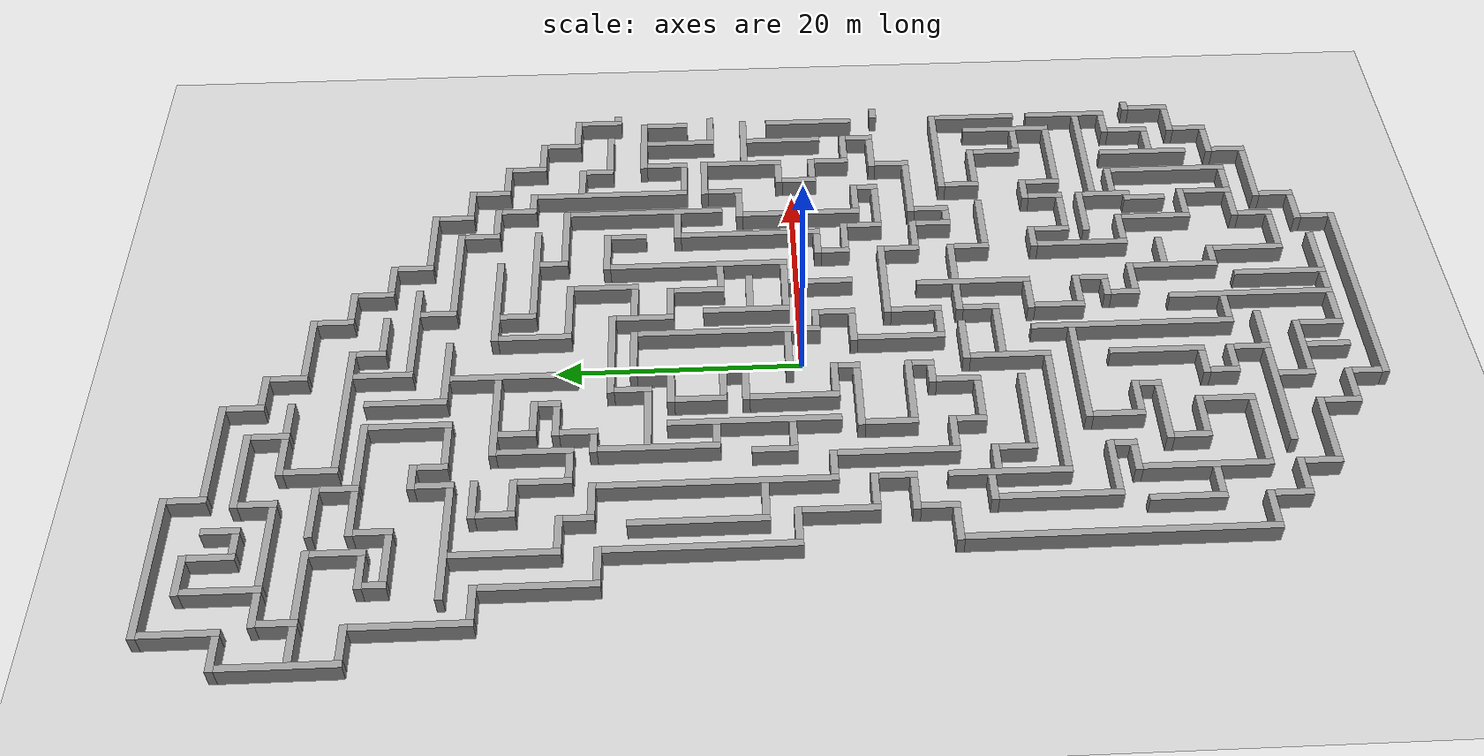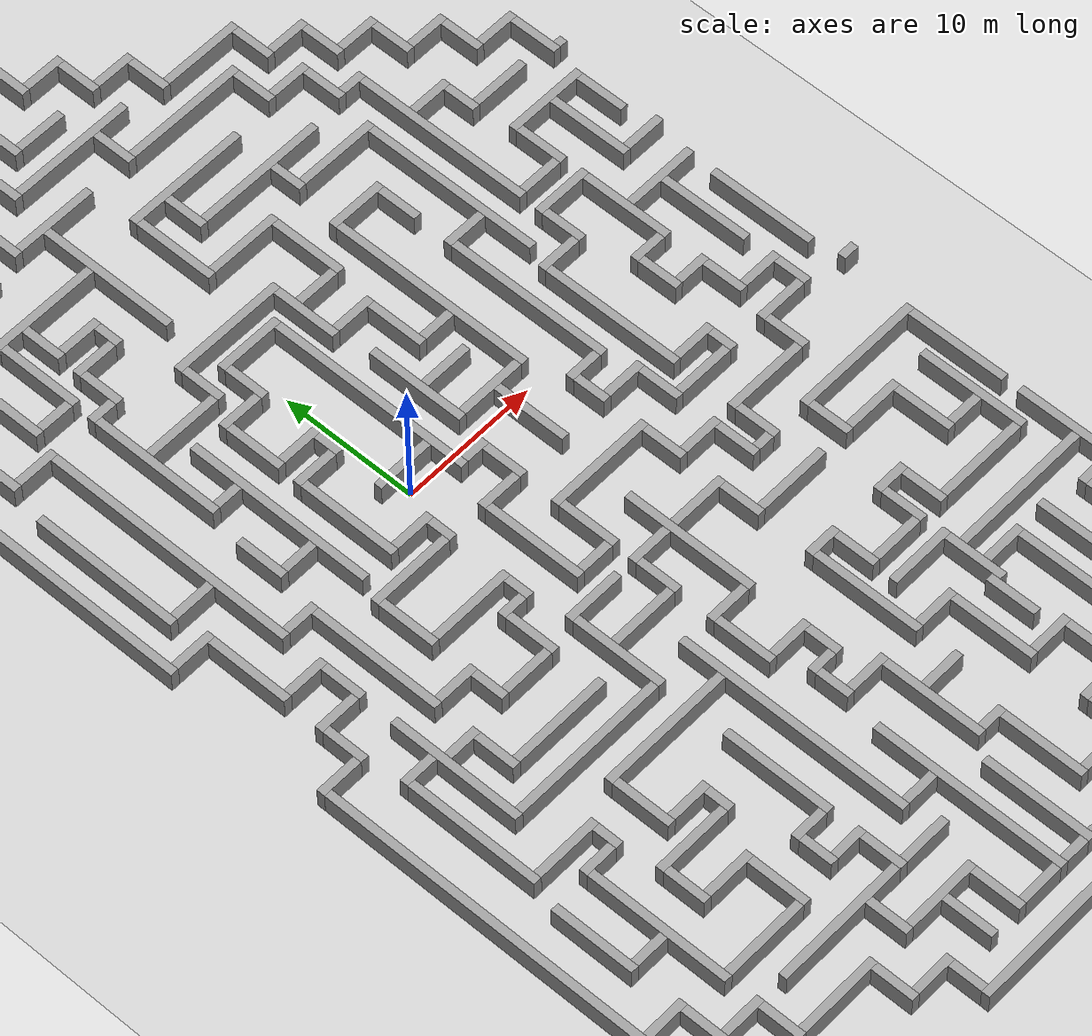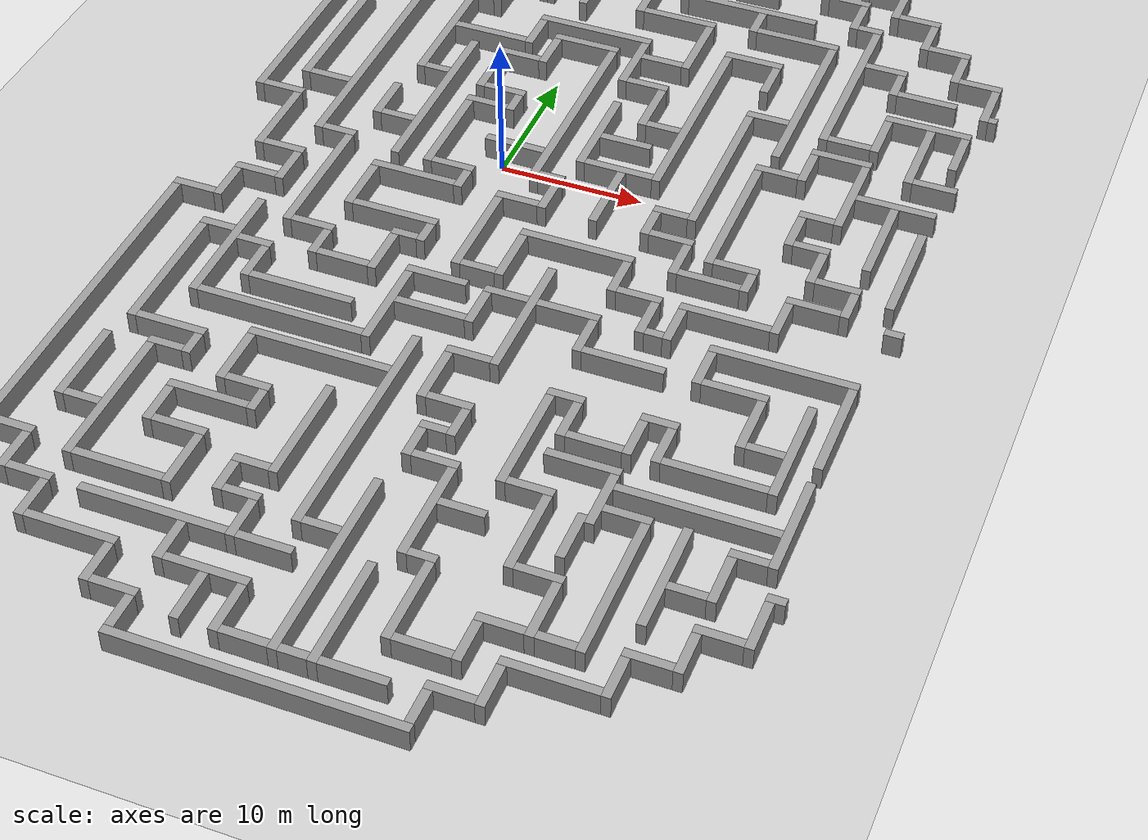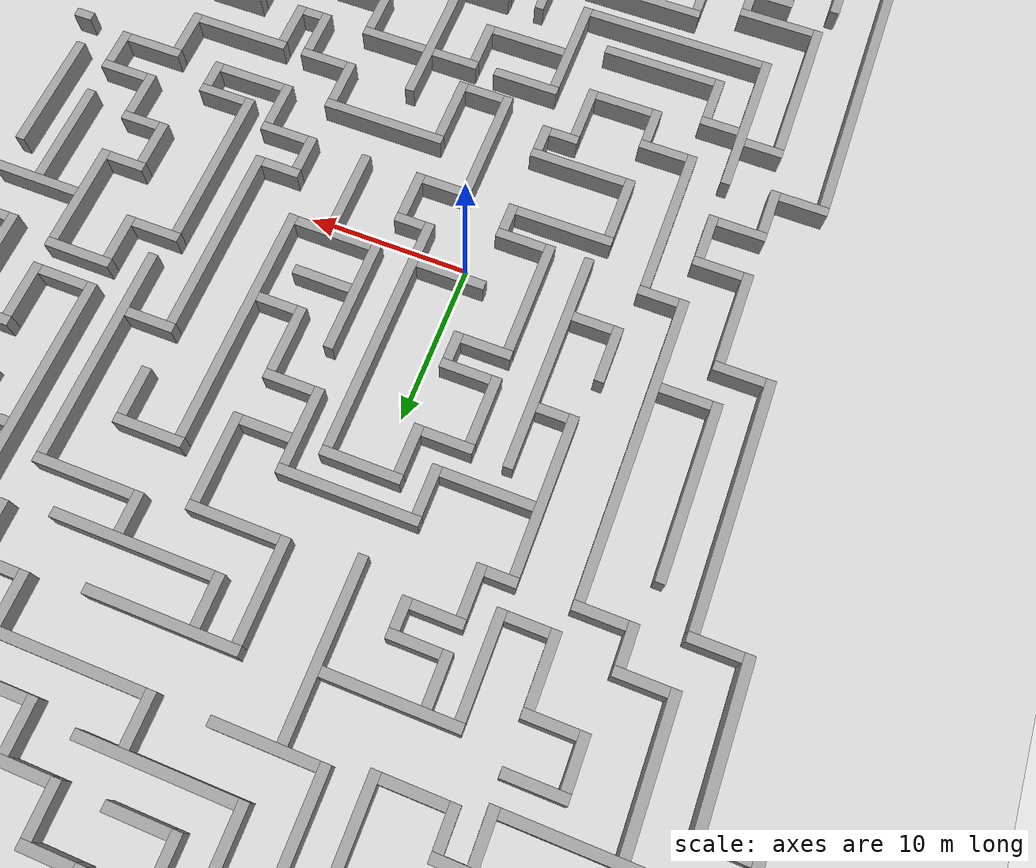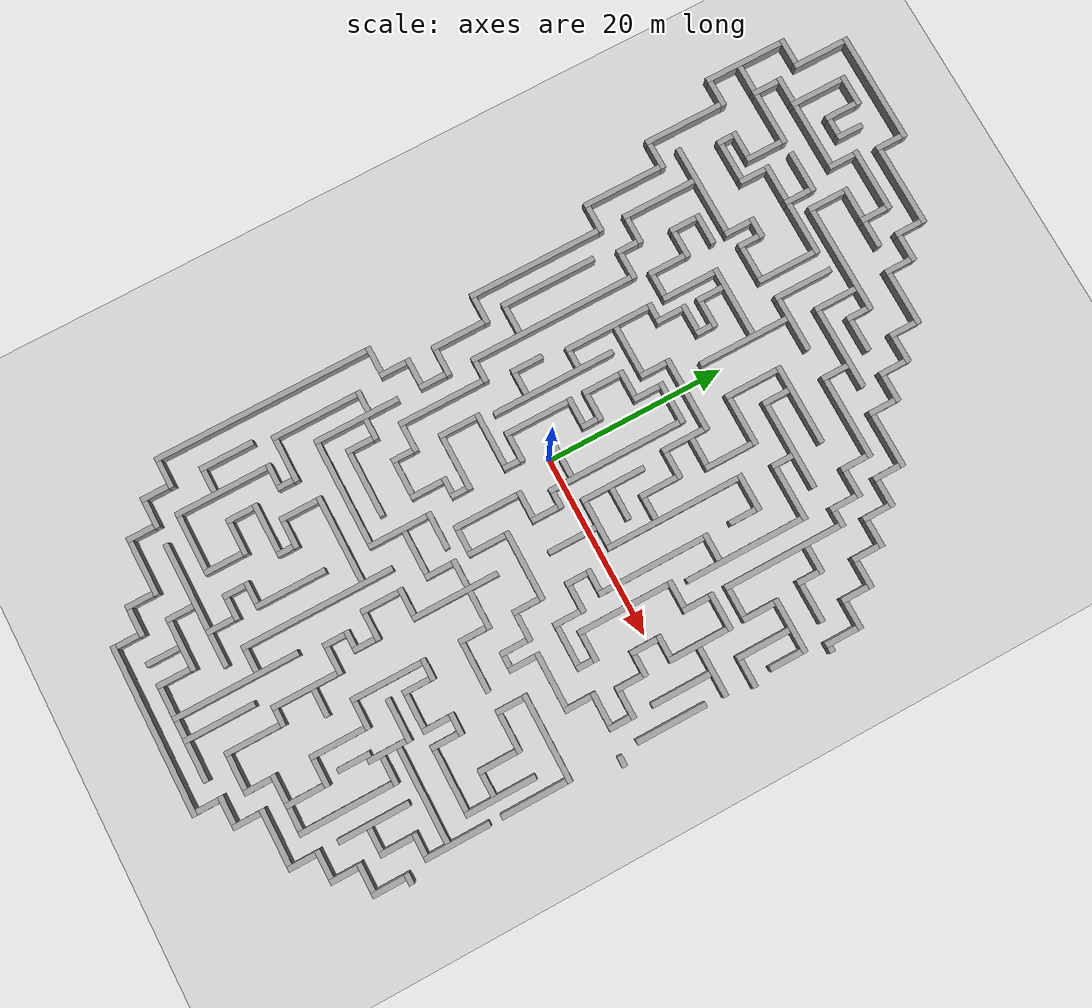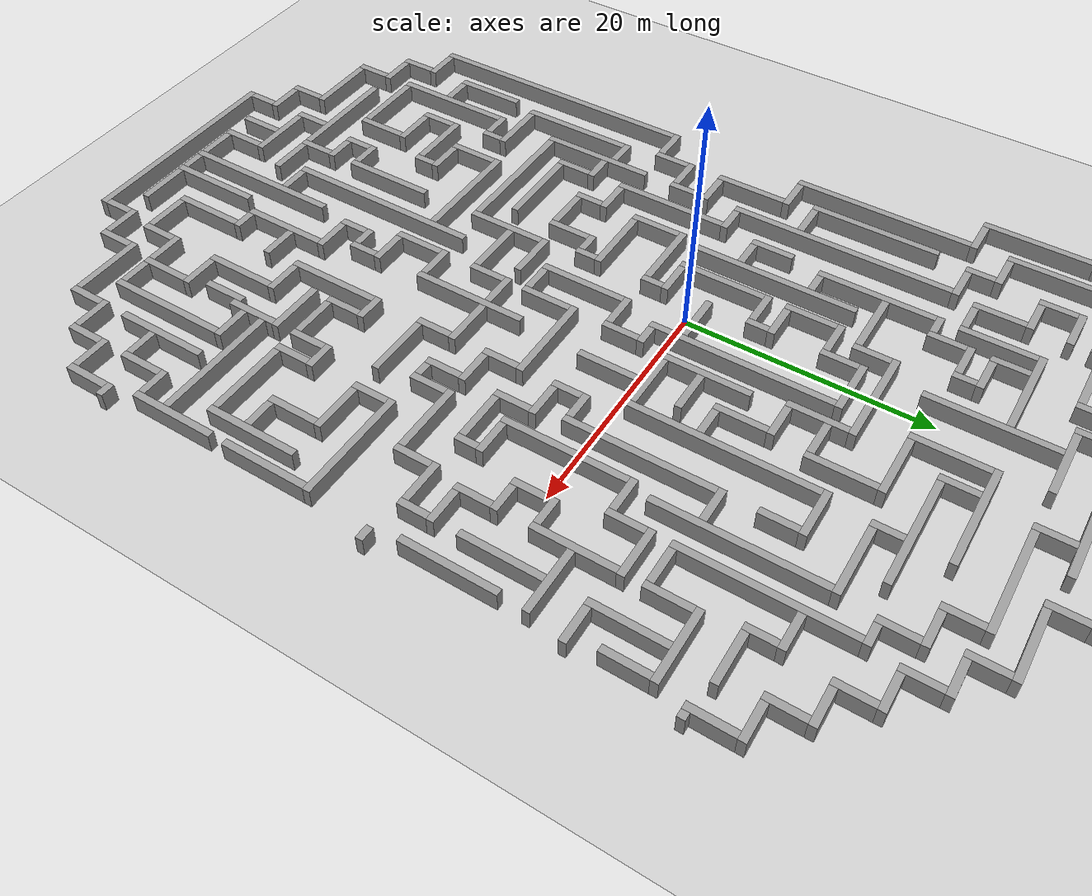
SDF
<sdf version='1.4'>
  <world name='default'>
    <!-- Default physics configuration -->
    <physics type='ode'>
      <gravity>0.000000 0.000000 -9.810000</gravity>
      <ode>
        <solver>
          <type>quick</type>
          <iters>20</iters>
          <sor>1.000000</sor>
        </solver>
        <constraints>
          <cfm>0.000000</cfm>
          <erp>0.200000</erp>
          <contact_max_correcting_vel>100.000000</contact_max_correcting_vel>
          <contact_surface_layer>0.000000</contact_surface_layer>
        </constraints>
      </ode>
      <real_time_update_rate>1000.000000</real_time_update_rate>
      <max_step_size>0.001000</max_step_size>
      <real_time_factor>1.000000</real_time_factor>
      <max_contacts>20</max_contacts>
    </physics>

    <!-- A global light source -->
    <include>
      <uri>model://sun</uri>
    </include>

    <!-- A ground plane -->
    <include>
      <uri>model://ground_plane</uri>
    </include>

    <!-- Walls -->
    <include>
      <uri>model://butterfly</uri>
      <name>walls</name>
      <pose>-28 50 0 0 0 0</pose>
    </include>

    <!-- Camera Position -->
    <gui fullscreen='0'>
      <camera name='user_camera'>
        <pose>5.694260 7.254210 18.725000 0.000000 1.145800 -3.134990</pose>
        <view_controller>orbit</view_controller>
      </camera>
    </gui>
  </world>
</sdf>

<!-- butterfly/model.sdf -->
<sdf version="1.4">
  <model name="ButterflyWorld">
    <static>1</static>
    <link name="Wall_0">
      <collision name="Wall_0_Collision">
        <geometry>
          <box>
            <size>12.60000 0.60000 3.00000</size>
          </box>
        </geometry>
        <pose>9.30000 -0.90000 0 0 0 0.00000</pose>
      </collision>
      <visual name="Wall_0_Visual">
        <geometry>
          <box>
            <size>12.60000 0.60000 3.00000</size>
          </box>
        </geometry>
        <material>
          <script>
            <uri>file://media/materials/scripts/gazebo.material</uri>
            <name>Gazebo/Grey</name>
          </script>
        </material>
        <pose>9.30000 -0.90000 0 0 0 0.00000</pose>
      </visual>
    </link>
    <link name="Wall_1">
      <collision name="Wall_1_Collision">
        <geometry>
          <box>
            <size>0.60000 6.00000 3.00000</size>
          </box>
        </geometry>
        <pose>3.30000 -4.20000 0 0 0 0.00000</pose>
      </collision>
      <visual name="Wall_1_Visual">
        <geometry>
          <box>
            <size>0.60000 6.00000 3.00000</size>
          </box>
        </geometry>
        <material>
          <script>
            <uri>file://media/materials/scripts/gazebo.material</uri>
            <name>Gazebo/Grey</name>
          </script>
        </material>
        <pose>3.30000 -4.20000 0 0 0 0.00000</pose>
      </visual>
    </link>
    <link name="Wall_2">
      <collision name="Wall_2_Collision">
        <geometry>
          <box>
            <size>0.60000 3.00000 3.00000</size>
          </box>
        </geometry>
        <pose>15.30000 -2.70000 0 0 0 0.00000</pose>
      </collision>
      <visual name="Wall_2_Visual">
        <geometry>
          <box>
            <size>0.60000 3.00000 3.00000</size>
          </box>
        </geometry>
        <material>
          <script>
            <uri>file://media/materials/scripts/gazebo.material</uri>
            <name>Gazebo/Grey</name>
          </script>
        </material>
        <pose>15.30000 -2.70000 0 0 0 0.00000</pose>
      </visual>
    </link>
    <link name="Wall_3">
      <collision name="Wall_3_Collision">
        <geometry>
          <box>
            <size>3.60000 0.60000 3.00000</size>
          </box>
        </geometry>
        <pose>8.40000 -3.30000 0 0 0 0.00000</pose>
      </collision>
      <visual name="Wall_3_Visual">
        <geometry>
          <box>
            <size>3.60000 0.60000 3.00000</size>
          </box>
        </geometry>
        <material>
          <script>
            <uri>file://media/materials/scripts/gazebo.material</uri>
            <name>Gazebo/Grey</name>
          </script>
        </material>
        <pose>8.40000 -3.30000 0 0 0 0.00000</pose>
      </visual>
    </link>
    <link name="Wall_4">
      <collision name="Wall_4_Collision">
        <geometry>
          <box>
            <size>0.60000 6.00000 3.00000</size>
          </box>
        </geometry>
        <pose>6.90000 -6.60000 0 0 0 0.00000</pose>
      </collision>
      <visual name="Wall_4_Visual">
        <geometry>
          <box>
            <size>0.60000 6.00000 3.00000</size>
          </box>
        </geometry>
        <material>
          <script>
            <uri>file://media/materials/scripts/gazebo.material</uri>
            <name>Gazebo/Grey</name>
          </script>
        </material>
        <pose>6.90000 -6.60000 0 0 0 0.00000</pose>
      </visual>
    </link>
    <link name="Wall_5">
      <collision name="Wall_5_Collision">
        <geometry>
          <box>
            <size>0.60000 3.60000 3.00000</size>
          </box>
        </geometry>
        <pose>9.90000 -5.40000 0 0 0 0.00000</pose>
      </collision>
      <visual name="Wall_5_Visual">
        <geometry>
          <box>
            <size>0.60000 3.60000 3.00000</size>
          </box>
        </geometry>
        <material>
          <script>
            <uri>file://media/materials/scripts/gazebo.material</uri>
            <name>Gazebo/Grey</name>
          </script>
        </material>
        <pose>9.90000 -5.40000 0 0 0 0.00000</pose>
      </visual>
    </link>
    <link name="Wall_6">
      <collision name="Wall_6_Collision">
        <geometry>
          <box>
            <size>9.00000 0.60000 3.00000</size>
          </box>
        </geometry>
        <pose>20.10000 -3.90000 0 0 0 0.00000</pose>
      </collision>
      <visual name="Wall_6_Visual">
        <geometry>
          <box>
            <size>9.00000 0.60000 3.00000</size>
          </box>
        </geometry>
        <material>
          <script>
            <uri>file://media/materials/scripts/gazebo.material</uri>
            <name>Gazebo/Grey</name>
          </script>
        </material>
        <pose>20.10000 -3.90000 0 0 0 0.00000</pose>
      </visual>
    </link>
    <link name="Wall_7">
      <collision name="Wall_7_Collision">
        <geometry>
          <box>
            <size>0.60000 3.00000 3.00000</size>
          </box>
        </geometry>
        <pose>12.30000 -5.70000 0 0 0 0.00000</pose>
      </collision>
      <visual name="Wall_7_Visual">
        <geometry>
          <box>
            <size>0.60000 3.00000 3.00000</size>
          </box>
        </geometry>
        <material>
          <script>
            <uri>file://media/materials/scripts/gazebo.material</uri>
            <name>Gazebo/Grey</name>
          </script>
        </material>
        <pose>12.30000 -5.70000 0 0 0 0.00000</pose>
      </visual>
    </link>
    <link name="Wall_8">
      <collision name="Wall_8_Collision">
        <geometry>
          <box>
            <size>0.60000 3.00000 3.00000</size>
          </box>
        </geometry>
        <pose>24.30000 -5.70000 0 0 0 0.00000</pose>
      </collision>
      <visual name="Wall_8_Visual">
        <geometry>
          <box>
            <size>0.60000 3.00000 3.00000</size>
          </box>
        </geometry>
        <material>
          <script>
            <uri>file://media/materials/scripts/gazebo.material</uri>
            <name>Gazebo/Grey</name>
          </script>
        </material>
        <pose>24.30000 -5.70000 0 0 0 0.00000</pose>
      </visual>
    </link>
    <link name="Wall_9">
      <collision name="Wall_9_Collision">
        <geometry>
          <box>
            <size>7.20000 0.60000 3.00000</size>
          </box>
        </geometry>
        <pose>18.00000 -6.30000 0 0 0 0.00000</pose>
      </collision>
      <visual name="Wall_9_Visual">
        <geometry>
          <box>
            <size>7.20000 0.60000 3.00000</size>
          </box>
        </geometry>
        <material>
          <script>
            <uri>file://media/materials/scripts/gazebo.material</uri>
            <name>Gazebo/Grey</name>
          </script>
        </material>
        <pose>18.00000 -6.30000 0 0 0 0.00000</pose>
      </visual>
    </link>
    <link name="Wall_10">
      <collision name="Wall_10_Collision">
        <geometry>
          <box>
            <size>3.00000 0.60000 3.00000</size>
          </box>
        </geometry>
        <pose>1.50000 -6.90000 0 0 0 0.00000</pose>
      </collision>
      <visual name="Wall_10_Visual">
        <geometry>
          <box>
            <size>3.00000 0.60000 3.00000</size>
          </box>
        </geometry>
        <material>
          <script>
            <uri>file://media/materials/scripts/gazebo.material</uri>
            <name>Gazebo/Grey</name>
          </script>
        </material>
        <pose>1.50000 -6.90000 0 0 0 0.00000</pose>
      </visual>
    </link>
    <link name="Wall_11">
      <collision name="Wall_11_Collision">
        <geometry>
          <box>
            <size>1.80000 0.60000 3.00000</size>
          </box>
        </geometry>
        <pose>11.10000 -6.90000 0 0 0 0.00000</pose>
      </collision>
      <visual name="Wall_11_Visual">
        <geometry>
          <box>
            <size>1.80000 0.60000 3.00000</size>
          </box>
        </geometry>
        <material>
          <script>
            <uri>file://media/materials/scripts/gazebo.material</uri>
            <name>Gazebo/Grey</name>
          </script>
        </material>
        <pose>11.10000 -6.90000 0 0 0 0.00000</pose>
      </visual>
    </link>
    <link name="Wall_12">
      <collision name="Wall_12_Collision">
        <geometry>
          <box>
            <size>0.60000 3.00000 3.00000</size>
          </box>
        </geometry>
        <pose>14.70000 -8.10000 0 0 0 0.00000</pose>
      </collision>
      <visual name="Wall_12_Visual">
        <geometry>
          <box>
            <size>0.60000 3.00000 3.00000</size>
          </box>
        </geometry>
        <material>
          <script>
            <uri>file://media/materials/scripts/gazebo.material</uri>
            <name>Gazebo/Grey</name>
          </script>
        </material>
        <pose>14.70000 -8.10000 0 0 0 0.00000</pose>
      </visual>
    </link>
    <link name="Wall_13">
      <collision name="Wall_13_Collision">
        <geometry>
          <box>
            <size>0.60000 3.00000 3.00000</size>
          </box>
        </geometry>
        <pose>21.30000 -8.10000 0 0 0 0.00000</pose>
      </collision>
      <visual name="Wall_13_Visual">
        <geometry>
          <box>
            <size>0.60000 3.00000 3.00000</size>
          </box>
        </geometry>
        <material>
          <script>
            <uri>file://media/materials/scripts/gazebo.material</uri>
            <name>Gazebo/Grey</name>
          </script>
        </material>
        <pose>21.30000 -8.10000 0 0 0 0.00000</pose>
      </visual>
    </link>
    <link name="Wall_14">
      <collision name="Wall_14_Collision">
        <geometry>
          <box>
            <size>3.00000 0.60000 3.00000</size>
          </box>
        </geometry>
        <pose>26.10000 -6.90000 0 0 0 0.00000</pose>
      </collision>
      <visual name="Wall_14_Visual">
        <geometry>
          <box>
            <size>3.00000 0.60000 3.00000</size>
          </box>
        </geometry>
        <material>
          <script>
            <uri>file://media/materials/scripts/gazebo.material</uri>
            <name>Gazebo/Grey</name>
          </script>
        </material>
        <pose>26.10000 -6.90000 0 0 0 0.00000</pose>
      </visual>
    </link>
    <link name="Wall_15">
      <collision name="Wall_15_Collision">
        <geometry>
          <box>
            <size>0.60000 9.00000 3.00000</size>
          </box>
        </geometry>
        <pose>0.30000 -11.70000 0 0 0 0.00000</pose>
      </collision>
      <visual name="Wall_15_Visual">
        <geometry>
          <box>
            <size>0.60000 9.00000 3.00000</size>
          </box>
        </geometry>
        <material>
          <script>
            <uri>file://media/materials/scripts/gazebo.material</uri>
            <name>Gazebo/Grey</name>
          </script>
        </material>
        <pose>0.30000 -11.70000 0 0 0 0.00000</pose>
      </visual>
    </link>
    <link name="Wall_16">
      <collision name="Wall_16_Collision">
        <geometry>
          <box>
            <size>0.60000 3.00000 3.00000</size>
          </box>
        </geometry>
        <pose>27.30000 -8.70000 0 0 0 0.00000</pose>
      </collision>
      <visual name="Wall_16_Visual">
        <geometry>
          <box>
            <size>0.60000 3.00000 3.00000</size>
          </box>
        </geometry>
        <material>
          <script>
            <uri>file://media/materials/scripts/gazebo.material</uri>
            <name>Gazebo/Grey</name>
          </script>
        </material>
        <pose>27.30000 -8.70000 0 0 0 0.00000</pose>
      </visual>
    </link>
    <link name="Wall_17">
      <collision name="Wall_17_Collision">
        <geometry>
          <box>
            <size>3.00000 0.60000 3.00000</size>
          </box>
        </geometry>
        <pose>5.10000 -9.30000 0 0 0 0.00000</pose>
      </collision>
      <visual name="Wall_17_Visual">
        <geometry>
          <box>
            <size>3.00000 0.60000 3.00000</size>
          </box>
        </geometry>
        <material>
          <script>
            <uri>file://media/materials/scripts/gazebo.material</uri>
            <name>Gazebo/Grey</name>
          </script>
        </material>
        <pose>5.10000 -9.30000 0 0 0 0.00000</pose>
      </visual>
    </link>
    <link name="Wall_18">
      <collision name="Wall_18_Collision">
        <geometry>
          <box>
            <size>7.20000 0.60000 3.00000</size>
          </box>
        </geometry>
        <pose>10.80000 -9.30000 0 0 0 0.00000</pose>
      </collision>
      <visual name="Wall_18_Visual">
        <geometry>
          <box>
            <size>7.20000 0.60000 3.00000</size>
          </box>
        </geometry>
        <material>
          <script>
            <uri>file://media/materials/scripts/gazebo.material</uri>
            <name>Gazebo/Grey</name>
          </script>
        </material>
        <pose>10.80000 -9.30000 0 0 0 0.00000</pose>
      </visual>
    </link>
    <link name="Wall_19">
      <collision name="Wall_19_Collision">
        <geometry>
          <box>
            <size>3.60000 0.60000 3.00000</size>
          </box>
        </geometry>
        <pose>19.20000 -9.30000 0 0 0 0.00000</pose>
      </collision>
      <visual name="Wall_19_Visual">
        <geometry>
          <box>
            <size>3.60000 0.60000 3.00000</size>
          </box>
        </geometry>
        <material>
          <script>
            <uri>file://media/materials/scripts/gazebo.material</uri>
            <name>Gazebo/Grey</name>
          </script>
        </material>
        <pose>19.20000 -9.30000 0 0 0 0.00000</pose>
      </visual>
    </link>
    <link name="Wall_20">
      <collision name="Wall_20_Collision">
        <geometry>
          <box>
            <size>3.00000 0.60000 3.00000</size>
          </box>
        </geometry>
        <pose>23.10000 -9.30000 0 0 0 0.00000</pose>
      </collision>
      <visual name="Wall_20_Visual">
        <geometry>
          <box>
            <size>3.00000 0.60000 3.00000</size>
          </box>
        </geometry>
        <material>
          <script>
            <uri>file://media/materials/scripts/gazebo.material</uri>
            <name>Gazebo/Grey</name>
          </script>
        </material>
        <pose>23.10000 -9.30000 0 0 0 0.00000</pose>
      </visual>
    </link>
    <link name="Wall_21">
      <collision name="Wall_21_Collision">
        <geometry>
          <box>
            <size>0.60000 3.00000 3.00000</size>
          </box>
        </geometry>
        <pose>3.90000 -11.10000 0 0 0 0.00000</pose>
      </collision>
      <visual name="Wall_21_Visual">
        <geometry>
          <box>
            <size>0.60000 3.00000 3.00000</size>
          </box>
        </geometry>
        <material>
          <script>
            <uri>file://media/materials/scripts/gazebo.material</uri>
            <name>Gazebo/Grey</name>
          </script>
        </material>
        <pose>3.90000 -11.10000 0 0 0 0.00000</pose>
      </visual>
    </link>
    <link name="Wall_22">
      <collision name="Wall_22_Collision">
        <geometry>
          <box>
            <size>0.60000 4.20000 3.00000</size>
          </box>
        </geometry>
        <pose>17.70000 -11.70000 0 0 0 0.00000</pose>
      </collision>
      <visual name="Wall_22_Visual">
        <geometry>
          <box>
            <size>0.60000 4.20000 3.00000</size>
          </box>
        </geometry>
        <material>
          <script>
            <uri>file://media/materials/scripts/gazebo.material</uri>
            <name>Gazebo/Grey</name>
          </script>
        </material>
        <pose>17.70000 -11.70000 0 0 0 0.00000</pose>
      </visual>
    </link>
    <link name="Wall_23">
      <collision name="Wall_23_Collision">
        <geometry>
          <box>
            <size>6.00000 0.60000 3.00000</size>
          </box>
        </geometry>
        <pose>30.60000 -9.90000 0 0 0 0.00000</pose>
      </collision>
      <visual name="Wall_23_Visual">
        <geometry>
          <box>
            <size>6.00000 0.60000 3.00000</size>
          </box>
        </geometry>
        <material>
          <script>
            <uri>file://media/materials/scripts/gazebo.material</uri>
            <name>Gazebo/Grey</name>
          </script>
        </material>
        <pose>30.60000 -9.90000 0 0 0 0.00000</pose>
      </visual>
    </link>
    <link name="Wall_24">
      <collision name="Wall_24_Collision">
        <geometry>
          <box>
            <size>0.60000 3.00000 3.00000</size>
          </box>
        </geometry>
        <pose>33.30000 -11.70000 0 0 0 0.00000</pose>
      </collision>
      <visual name="Wall_24_Visual">
        <geometry>
          <box>
            <size>0.60000 3.00000 3.00000</size>
          </box>
        </geometry>
        <material>
          <script>
            <uri>file://media/materials/scripts/gazebo.material</uri>
            <name>Gazebo/Grey</name>
          </script>
        </material>
        <pose>33.30000 -11.70000 0 0 0 0.00000</pose>
      </visual>
    </link>
    <link name="Wall_25">
      <collision name="Wall_25_Collision">
        <geometry>
          <box>
            <size>3.00000 0.60000 3.00000</size>
          </box>
        </geometry>
        <pose>2.10000 -12.30000 0 0 0 0.00000</pose>
      </collision>
      <visual name="Wall_25_Visual">
        <geometry>
          <box>
            <size>3.00000 0.60000 3.00000</size>
          </box>
        </geometry>
        <material>
          <script>
            <uri>file://media/materials/scripts/gazebo.material</uri>
            <name>Gazebo/Grey</name>
          </script>
        </material>
        <pose>2.10000 -12.30000 0 0 0 0.00000</pose>
      </visual>
    </link>
    <link name="Wall_26">
      <collision name="Wall_26_Collision">
        <geometry>
          <box>
            <size>6.00000 0.60000 3.00000</size>
          </box>
        </geometry>
        <pose>7.20000 -12.30000 0 0 0 0.00000</pose>
      </collision>
      <visual name="Wall_26_Visual">
        <geometry>
          <box>
            <size>6.00000 0.60000 3.00000</size>
          </box>
        </geometry>
        <material>
          <script>
            <uri>file://media/materials/scripts/gazebo.material</uri>
            <name>Gazebo/Grey</name>
          </script>
        </material>
        <pose>7.20000 -12.30000 0 0 0 0.00000</pose>
      </visual>
    </link>
    <link name="Wall_27">
      <collision name="Wall_27_Collision">
        <geometry>
          <box>
            <size>4.80000 0.60000 3.00000</size>
          </box>
        </geometry>
        <pose>13.80000 -12.30000 0 0 0 0.00000</pose>
      </collision>
      <visual name="Wall_27_Visual">
        <geometry>
          <box>
            <size>4.80000 0.60000 3.00000</size>
          </box>
        </geometry>
        <material>
          <script>
            <uri>file://media/materials/scripts/gazebo.material</uri>
            <name>Gazebo/Grey</name>
          </script>
        </material>
        <pose>13.80000 -12.30000 0 0 0 0.00000</pose>
      </visual>
    </link>
    <link name="Wall_28">
      <collision name="Wall_28_Collision">
        <geometry>
          <box>
            <size>0.60000 4.20000 3.00000</size>
          </box>
        </geometry>
        <pose>9.90000 -14.70000 0 0 0 0.00000</pose>
      </collision>
      <visual name="Wall_28_Visual">
        <geometry>
          <box>
            <size>0.60000 4.20000 3.00000</size>
          </box>
        </geometry>
        <material>
          <script>
            <uri>file://media/materials/scripts/gazebo.material</uri>
            <name>Gazebo/Grey</name>
          </script>
        </material>
        <pose>9.90000 -14.70000 0 0 0 0.00000</pose>
      </visual>
    </link>
    <link name="Wall_29">
      <collision name="Wall_29_Collision">
        <geometry>
          <box>
            <size>0.60000 3.00000 3.00000</size>
          </box>
        </geometry>
        <pose>15.90000 -14.10000 0 0 0 0.00000</pose>
      </collision>
      <visual name="Wall_29_Visual">
        <geometry>
          <box>
            <size>0.60000 3.00000 3.00000</size>
          </box>
        </geometry>
        <material>
          <script>
            <uri>file://media/materials/scripts/gazebo.material</uri>
            <name>Gazebo/Grey</name>
          </script>
        </material>
        <pose>15.90000 -14.10000 0 0 0 0.00000</pose>
      </visual>
    </link>
    <link name="Wall_30">
      <collision name="Wall_30_Collision">
        <geometry>
          <box>
            <size>3.00000 0.60000 3.00000</size>
          </box>
        </geometry>
        <pose>35.10000 -12.90000 0 0 0 0.00000</pose>
      </collision>
      <visual name="Wall_30_Visual">
        <geometry>
          <box>
            <size>3.00000 0.60000 3.00000</size>
          </box>
        </geometry>
        <material>
          <script>
            <uri>file://media/materials/scripts/gazebo.material</uri>
            <name>Gazebo/Grey</name>
          </script>
        </material>
        <pose>35.10000 -12.90000 0 0 0 0.00000</pose>
      </visual>
    </link>
    <link name="Wall_31">
      <collision name="Wall_31_Collision">
        <geometry>
          <box>
            <size>12.00000 0.60000 3.00000</size>
          </box>
        </geometry>
        <pose>24.00000 -13.50000 0 0 0 0.00000</pose>
      </collision>
      <visual name="Wall_31_Visual">
        <geometry>
          <box>
            <size>12.00000 0.60000 3.00000</size>
          </box>
        </geometry>
        <material>
          <script>
            <uri>file://media/materials/scripts/gazebo.material</uri>
            <name>Gazebo/Grey</name>
          </script>
        </material>
        <pose>24.00000 -13.50000 0 0 0 0.00000</pose>
      </visual>
    </link>
    <link name="Wall_32">
      <collision name="Wall_32_Collision">
        <geometry>
          <box>
            <size>0.60000 3.00000 3.00000</size>
          </box>
        </geometry>
        <pose>36.30000 -14.70000 0 0 0 0.00000</pose>
      </collision>
      <visual name="Wall_32_Visual">
        <geometry>
          <box>
            <size>0.60000 3.00000 3.00000</size>
          </box>
        </geometry>
        <material>
          <script>
            <uri>file://media/materials/scripts/gazebo.material</uri>
            <name>Gazebo/Grey</name>
          </script>
        </material>
        <pose>36.30000 -14.70000 0 0 0 0.00000</pose>
      </visual>
    </link>
    <link name="Wall_33">
      <collision name="Wall_33_Collision">
        <geometry>
          <box>
            <size>0.60000 4.80000 3.00000</size>
          </box>
        </geometry>
        <pose>27.30000 -16.20000 0 0 0 0.00000</pose>
      </collision>
      <visual name="Wall_33_Visual">
        <geometry>
          <box>
            <size>0.60000 4.80000 3.00000</size>
          </box>
        </geometry>
        <material>
          <script>
            <uri>file://media/materials/scripts/gazebo.material</uri>
            <name>Gazebo/Grey</name>
          </script>
        </material>
        <pose>27.30000 -16.20000 0 0 0 0.00000</pose>
      </visual>
    </link>
    <link name="Wall_34">
      <collision name="Wall_34_Collision">
        <geometry>
          <box>
            <size>0.60000 2.40000 3.00000</size>
          </box>
        </geometry>
        <pose>29.70000 -15.00000 0 0 0 0.00000</pose>
      </collision>
      <visual name="Wall_34_Visual">
        <geometry>
          <box>
            <size>0.60000 2.40000 3.00000</size>
          </box>
        </geometry>
        <material>
          <script>
            <uri>file://media/materials/scripts/gazebo.material</uri>
            <name>Gazebo/Grey</name>
          </script>
        </material>
        <pose>29.70000 -15.00000 0 0 0 0.00000</pose>
      </visual>
    </link>
    <link name="Wall_35">
      <collision name="Wall_35_Collision">
        <geometry>
          <box>
            <size>4.20000 0.60000 3.00000</size>
          </box>
        </geometry>
        <pose>13.50000 -15.30000 0 0 0 0.00000</pose>
      </collision>
      <visual name="Wall_35_Visual">
        <geometry>
          <box>
            <size>4.20000 0.60000 3.00000</size>
          </box>
        </geometry>
        <material>
          <script>
            <uri>file://media/materials/scripts/gazebo.material</uri>
            <name>Gazebo/Grey</name>
          </script>
        </material>
        <pose>13.50000 -15.30000 0 0 0 0.00000</pose>
      </visual>
    </link>
    <link name="Wall_36">
      <collision name="Wall_36_Collision">
        <geometry>
          <box>
            <size>6.00000 0.60000 3.00000</size>
          </box>
        </geometry>
        <pose>19.20000 -15.30000 0 0 0 0.00000</pose>
      </collision>
      <visual name="Wall_36_Visual">
        <geometry>
          <box>
            <size>6.00000 0.60000 3.00000</size>
          </box>
        </geometry>
        <material>
          <script>
            <uri>file://media/materials/scripts/gazebo.material</uri>
            <name>Gazebo/Grey</name>
          </script>
        </material>
        <pose>19.20000 -15.30000 0 0 0 0.00000</pose>
      </visual>
    </link>
    <link name="Wall_37">
      <collision name="Wall_37_Collision">
        <geometry>
          <box>
            <size>0.60000 6.60000 3.00000</size>
          </box>
        </geometry>
        <pose>24.30000 -18.30000 0 0 0 0.00000</pose>
      </collision>
      <visual name="Wall_37_Visual">
        <geometry>
          <box>
            <size>0.60000 6.60000 3.00000</size>
          </box>
        </geometry>
        <material>
          <script>
            <uri>file://media/materials/scripts/gazebo.material</uri>
            <name>Gazebo/Grey</name>
          </script>
        </material>
        <pose>24.30000 -18.30000 0 0 0 0.00000</pose>
      </visual>
    </link>
    <link name="Wall_38">
      <collision name="Wall_38_Collision">
        <geometry>
          <box>
            <size>3.00000 0.60000 3.00000</size>
          </box>
        </geometry>
        <pose>2.10000 -15.90000 0 0 0 0.00000</pose>
      </collision>
      <visual name="Wall_38_Visual">
        <geometry>
          <box>
            <size>3.00000 0.60000 3.00000</size>
          </box>
        </geometry>
        <material>
          <script>
            <uri>file://media/materials/scripts/gazebo.material</uri>
            <name>Gazebo/Grey</name>
          </script>
        </material>
        <pose>2.10000 -15.90000 0 0 0 0.00000</pose>
      </visual>
    </link>
    <link name="Wall_39">
      <collision name="Wall_39_Collision">
        <geometry>
          <box>
            <size>0.60000 3.00000 3.00000</size>
          </box>
        </geometry>
        <pose>11.70000 -17.10000 0 0 0 0.00000</pose>
      </collision>
      <visual name="Wall_39_Visual">
        <geometry>
          <box>
            <size>0.60000 3.00000 3.00000</size>
          </box>
        </geometry>
        <material>
          <script>
            <uri>file://media/materials/scripts/gazebo.material</uri>
            <name>Gazebo/Grey</name>
          </script>
        </material>
        <pose>11.70000 -17.10000 0 0 0 0.00000</pose>
      </visual>
    </link>
    <link name="Wall_40">
      <collision name="Wall_40_Collision">
        <geometry>
          <box>
            <size>0.60000 6.60000 3.00000</size>
          </box>
        </geometry>
        <pose>21.90000 -18.90000 0 0 0 0.00000</pose>
      </collision>
      <visual name="Wall_40_Visual">
        <geometry>
          <box>
            <size>0.60000 6.60000 3.00000</size>
          </box>
        </geometry>
        <material>
          <script>
            <uri>file://media/materials/scripts/gazebo.material</uri>
            <name>Gazebo/Grey</name>
          </script>
        </material>
        <pose>21.90000 -18.90000 0 0 0 0.00000</pose>
      </visual>
    </link>
    <link name="Wall_41">
      <collision name="Wall_41_Collision">
        <geometry>
          <box>
            <size>3.60000 0.60000 3.00000</size>
          </box>
        </geometry>
        <pose>31.80000 -15.90000 0 0 0 0.00000</pose>
      </collision>
      <visual name="Wall_41_Visual">
        <geometry>
          <box>
            <size>3.60000 0.60000 3.00000</size>
          </box>
        </geometry>
        <material>
          <script>
            <uri>file://media/materials/scripts/gazebo.material</uri>
            <name>Gazebo/Grey</name>
          </script>
        </material>
        <pose>31.80000 -15.90000 0 0 0 0.00000</pose>
      </visual>
    </link>
    <link name="Wall_42">
      <collision name="Wall_42_Collision">
        <geometry>
          <box>
            <size>3.00000 0.60000 3.00000</size>
          </box>
        </geometry>
        <pose>38.10000 -15.90000 0 0 0 0.00000</pose>
      </collision>
      <visual name="Wall_42_Visual">
        <geometry>
          <box>
            <size>3.00000 0.60000 3.00000</size>
          </box>
        </geometry>
        <material>
          <script>
            <uri>file://media/materials/scripts/gazebo.material</uri>
            <name>Gazebo/Grey</name>
          </script>
        </material>
        <pose>38.10000 -15.90000 0 0 0 0.00000</pose>
      </visual>
    </link>
    <link name="Wall_43">
      <collision name="Wall_43_Collision">
        <geometry>
          <box>
            <size>0.60000 9.00000 3.00000</size>
          </box>
        </geometry>
        <pose>3.30000 -20.70000 0 0 0 0.00000</pose>
      </collision>
      <visual name="Wall_43_Visual">
        <geometry>
          <box>
            <size>0.60000 9.00000 3.00000</size>
          </box>
        </geometry>
        <material>
          <script>
            <uri>file://media/materials/scripts/gazebo.material</uri>
            <name>Gazebo/Grey</name>
          </script>
        </material>
        <pose>3.30000 -20.70000 0 0 0 0.00000</pose>
      </visual>
    </link>
    <link name="Wall_44">
      <collision name="Wall_44_Collision">
        <geometry>
          <box>
            <size>3.00000 0.60000 3.00000</size>
          </box>
        </geometry>
        <pose>8.10000 -16.50000 0 0 0 0.00000</pose>
      </collision>
      <visual name="Wall_44_Visual">
        <geometry>
          <box>
            <size>3.00000 0.60000 3.00000</size>
          </box>
        </geometry>
        <material>
          <script>
            <uri>file://media/materials/scripts/gazebo.material</uri>
            <name>Gazebo/Grey</name>
          </script>
        </material>
        <pose>8.10000 -16.50000 0 0 0 0.00000</pose>
      </visual>
    </link>
    <link name="Wall_45">
      <collision name="Wall_45_Collision">
        <geometry>
          <box>
            <size>0.60000 3.00000 3.00000</size>
          </box>
        </geometry>
        <pose>39.30000 -17.70000 0 0 0 0.00000</pose>
      </collision>
      <visual name="Wall_45_Visual">
        <geometry>
          <box>
            <size>0.60000 3.00000 3.00000</size>
          </box>
        </geometry>
        <material>
          <script>
            <uri>file://media/materials/scripts/gazebo.material</uri>
            <name>Gazebo/Grey</name>
          </script>
        </material>
        <pose>39.30000 -17.70000 0 0 0 0.00000</pose>
      </visual>
    </link>
    <link name="Wall_46">
      <collision name="Wall_46_Collision">
        <geometry>
          <box>
            <size>0.60000 1.80000 3.00000</size>
          </box>
        </geometry>
        <pose>6.90000 -17.70000 0 0 0 0.00000</pose>
      </collision>
      <visual name="Wall_46_Visual">
        <geometry>
          <box>
            <size>0.60000 1.80000 3.00000</size>
          </box>
        </geometry>
        <material>
          <script>
            <uri>file://media/materials/scripts/gazebo.material</uri>
            <name>Gazebo/Grey</name>
          </script>
        </material>
        <pose>6.90000 -17.70000 0 0 0 0.00000</pose>
      </visual>
    </link>
    <link name="Wall_47">
      <collision name="Wall_47_Collision">
        <geometry>
          <box>
            <size>4.20000 0.60000 3.00000</size>
          </box>
        </geometry>
        <pose>9.30000 -18.30000 0 0 0 0.00000</pose>
      </collision>
      <visual name="Wall_47_Visual">
        <geometry>
          <box>
            <size>4.20000 0.60000 3.00000</size>
          </box>
        </geometry>
        <material>
          <script>
            <uri>file://media/materials/scripts/gazebo.material</uri>
            <name>Gazebo/Grey</name>
          </script>
        </material>
        <pose>9.30000 -18.30000 0 0 0 0.00000</pose>
      </visual>
    </link>
    <link name="Wall_48">
      <collision name="Wall_48_Collision">
        <geometry>
          <box>
            <size>9.00000 0.60000 3.00000</size>
          </box>
        </geometry>
        <pose>32.10000 -18.30000 0 0 0 0.00000</pose>
      </collision>
      <visual name="Wall_48_Visual">
        <geometry>
          <box>
            <size>9.00000 0.60000 3.00000</size>
          </box>
        </geometry>
        <material>
          <script>
            <uri>file://media/materials/scripts/gazebo.material</uri>
            <name>Gazebo/Grey</name>
          </script>
        </material>
        <pose>32.10000 -18.30000 0 0 0 0.00000</pose>
      </visual>
    </link>
    <link name="Wall_49">
      <collision name="Wall_49_Collision">
        <geometry>
          <box>
            <size>0.60000 3.00000 3.00000</size>
          </box>
        </geometry>
        <pose>33.90000 -20.10000 0 0 0 0.00000</pose>
      </collision>
      <visual name="Wall_49_Visual">
        <geometry>
          <box>
            <size>0.60000 3.00000 3.00000</size>
          </box>
        </geometry>
        <material>
          <script>
            <uri>file://media/materials/scripts/gazebo.material</uri>
            <name>Gazebo/Grey</name>
          </script>
        </material>
        <pose>33.90000 -20.10000 0 0 0 0.00000</pose>
      </visual>
    </link>
    <link name="Wall_50">
      <collision name="Wall_50_Collision">
        <geometry>
          <box>
            <size>6.00000 0.60000 3.00000</size>
          </box>
        </geometry>
        <pose>42.60000 -18.90000 0 0 0 0.00000</pose>
      </collision>
      <visual name="Wall_50_Visual">
        <geometry>
          <box>
            <size>6.00000 0.60000 3.00000</size>
          </box>
        </geometry>
        <material>
          <script>
            <uri>file://media/materials/scripts/gazebo.material</uri>
            <name>Gazebo/Grey</name>
          </script>
        </material>
        <pose>42.60000 -18.90000 0 0 0 0.00000</pose>
      </visual>
    </link>
    <link name="Wall_51">
      <collision name="Wall_51_Collision">
        <geometry>
          <box>
            <size>2.40000 0.60000 3.00000</size>
          </box>
        </geometry>
        <pose>16.80000 -19.50000 0 0 0 0.00000</pose>
      </collision>
      <visual name="Wall_51_Visual">
        <geometry>
          <box>
            <size>2.40000 0.60000 3.00000</size>
          </box>
        </geometry>
        <material>
          <script>
            <uri>file://media/materials/scripts/gazebo.material</uri>
            <name>Gazebo/Grey</name>
          </script>
        </material>
        <pose>16.80000 -19.50000 0 0 0 0.00000</pose>
      </visual>
    </link>
    <link name="Wall_52">
      <collision name="Wall_52_Collision">
        <geometry>
          <box>
            <size>0.60000 3.00000 3.00000</size>
          </box>
        </geometry>
        <pose>45.30000 -20.70000 0 0 0 0.00000</pose>
      </collision>
      <visual name="Wall_52_Visual">
        <geometry>
          <box>
            <size>0.60000 3.00000 3.00000</size>
          </box>
        </geometry>
        <material>
          <script>
            <uri>file://media/materials/scripts/gazebo.material</uri>
            <name>Gazebo/Grey</name>
          </script>
        </material>
        <pose>45.30000 -20.70000 0 0 0 0.00000</pose>
      </visual>
    </link>
    <link name="Wall_53">
      <collision name="Wall_53_Collision">
        <geometry>
          <box>
            <size>0.60000 3.00000 3.00000</size>
          </box>
        </geometry>
        <pose>15.90000 -21.30000 0 0 0 0.00000</pose>
      </collision>
      <visual name="Wall_53_Visual">
        <geometry>
          <box>
            <size>0.60000 3.00000 3.00000</size>
          </box>
        </geometry>
        <material>
          <script>
            <uri>file://media/materials/scripts/gazebo.material</uri>
            <name>Gazebo/Grey</name>
          </script>
        </material>
        <pose>15.90000 -21.30000 0 0 0 0.00000</pose>
      </visual>
    </link>
    <link name="Wall_54">
      <collision name="Wall_54_Collision">
        <geometry>
          <box>
            <size>0.60000 2.40000 3.00000</size>
          </box>
        </geometry>
        <pose>17.70000 -21.00000 0 0 0 0.00000</pose>
      </collision>
      <visual name="Wall_54_Visual">
        <geometry>
          <box>
            <size>0.60000 2.40000 3.00000</size>
          </box>
        </geometry>
        <material>
          <script>
            <uri>file://media/materials/scripts/gazebo.material</uri>
            <name>Gazebo/Grey</name>
          </script>
        </material>
        <pose>17.70000 -21.00000 0 0 0 0.00000</pose>
      </visual>
    </link>
    <link name="Wall_55">
      <collision name="Wall_55_Collision">
        <geometry>
          <box>
            <size>6.00000 0.60000 3.00000</size>
          </box>
        </geometry>
        <pose>27.60000 -21.30000 0 0 0 0.00000</pose>
      </collision>
      <visual name="Wall_55_Visual">
        <geometry>
          <box>
            <size>6.00000 0.60000 3.00000</size>
          </box>
        </geometry>
        <material>
          <script>
            <uri>file://media/materials/scripts/gazebo.material</uri>
            <name>Gazebo/Grey</name>
          </script>
        </material>
        <pose>27.60000 -21.30000 0 0 0 0.00000</pose>
      </visual>
    </link>
    <link name="Wall_56">
      <collision name="Wall_56_Collision">
        <geometry>
          <box>
            <size>9.00000 0.60000 3.00000</size>
          </box>
        </geometry>
        <pose>38.70000 -21.30000 0 0 0 0.00000</pose>
      </collision>
      <visual name="Wall_56_Visual">
        <geometry>
          <box>
            <size>9.00000 0.60000 3.00000</size>
          </box>
        </geometry>
        <material>
          <script>
            <uri>file://media/materials/scripts/gazebo.material</uri>
            <name>Gazebo/Grey</name>
          </script>
        </material>
        <pose>38.70000 -21.30000 0 0 0 0.00000</pose>
      </visual>
    </link>
    <link name="Wall_57">
      <collision name="Wall_57_Collision">
        <geometry>
          <box>
            <size>3.60000 0.60000 3.00000</size>
          </box>
        </geometry>
        <pose>19.80000 -21.90000 0 0 0 0.00000</pose>
      </collision>
      <visual name="Wall_57_Visual">
        <geometry>
          <box>
            <size>3.60000 0.60000 3.00000</size>
          </box>
        </geometry>
        <material>
          <script>
            <uri>file://media/materials/scripts/gazebo.material</uri>
            <name>Gazebo/Grey</name>
          </script>
        </material>
        <pose>19.80000 -21.90000 0 0 0 0.00000</pose>
      </visual>
    </link>
    <link name="Wall_58">
      <collision name="Wall_58_Collision">
        <geometry>
          <box>
            <size>0.60000 10.20000 3.00000</size>
          </box>
        </geometry>
        <pose>26.70000 -26.70000 0 0 0 0.00000</pose>
      </collision>
      <visual name="Wall_58_Visual">
        <geometry>
          <box>
            <size>0.60000 10.20000 3.00000</size>
          </box>
        </geometry>
        <material>
          <script>
            <uri>file://media/materials/scripts/gazebo.material</uri>
            <name>Gazebo/Grey</name>
          </script>
        </material>
        <pose>26.70000 -26.70000 0 0 0 0.00000</pose>
      </visual>
    </link>
    <link name="Wall_59">
      <collision name="Wall_59_Collision">
        <geometry>
          <box>
            <size>0.60000 3.00000 3.00000</size>
          </box>
        </geometry>
        <pose>42.90000 -23.10000 0 0 0 0.00000</pose>
      </collision>
      <visual name="Wall_59_Visual">
        <geometry>
          <box>
            <size>0.60000 3.00000 3.00000</size>
          </box>
        </geometry>
        <material>
          <script>
            <uri>file://media/materials/scripts/gazebo.material</uri>
            <name>Gazebo/Grey</name>
          </script>
        </material>
        <pose>42.90000 -23.10000 0 0 0 0.00000</pose>
      </visual>
    </link>
    <link name="Wall_60">
      <collision name="Wall_60_Collision">
        <geometry>
          <box>
            <size>3.00000 0.60000 3.00000</size>
          </box>
        </geometry>
        <pose>47.10000 -21.90000 0 0 0 0.00000</pose>
      </collision>
      <visual name="Wall_60_Visual">
        <geometry>
          <box>
            <size>3.00000 0.60000 3.00000</size>
          </box>
        </geometry>
        <material>
          <script>
            <uri>file://media/materials/scripts/gazebo.material</uri>
            <name>Gazebo/Grey</name>
          </script>
        </material>
        <pose>47.10000 -21.90000 0 0 0 0.00000</pose>
      </visual>
    </link>
    <link name="Wall_61">
      <collision name="Wall_61_Collision">
        <geometry>
          <box>
            <size>10.20000 0.60000 3.00000</size>
          </box>
        </geometry>
        <pose>10.50000 -22.50000 0 0 0 0.00000</pose>
      </collision>
      <visual name="Wall_61_Visual">
        <geometry>
          <box>
            <size>10.20000 0.60000 3.00000</size>
          </box>
        </geometry>
        <material>
          <script>
            <uri>file://media/materials/scripts/gazebo.material</uri>
            <name>Gazebo/Grey</name>
          </script>
        </material>
        <pose>10.50000 -22.50000 0 0 0 0.00000</pose>
      </visual>
    </link>
    <link name="Wall_62">
      <collision name="Wall_62_Collision">
        <geometry>
          <box>
            <size>0.60000 3.00000 3.00000</size>
          </box>
        </geometry>
        <pose>48.30000 -23.70000 0 0 0 0.00000</pose>
      </collision>
      <visual name="Wall_62_Visual">
        <geometry>
          <box>
            <size>0.60000 3.00000 3.00000</size>
          </box>
        </geometry>
        <material>
          <script>
            <uri>file://media/materials/scripts/gazebo.material</uri>
            <name>Gazebo/Grey</name>
          </script>
        </material>
        <pose>48.30000 -23.70000 0 0 0 0.00000</pose>
      </visual>
    </link>
    <link name="Wall_63">
      <collision name="Wall_63_Collision">
        <geometry>
          <box>
            <size>0.60000 8.40000 3.00000</size>
          </box>
        </geometry>
        <pose>9.30000 -27.00000 0 0 0 0.00000</pose>
      </collision>
      <visual name="Wall_63_Visual">
        <geometry>
          <box>
            <size>0.60000 8.40000 3.00000</size>
          </box>
        </geometry>
        <material>
          <script>
            <uri>file://media/materials/scripts/gazebo.material</uri>
            <name>Gazebo/Grey</name>
          </script>
        </material>
        <pose>9.30000 -27.00000 0 0 0 0.00000</pose>
      </visual>
    </link>
    <link name="Wall_64">
      <collision name="Wall_64_Collision">
        <geometry>
          <box>
            <size>3.60000 0.60000 3.00000</size>
          </box>
        </geometry>
        <pose>14.40000 -24.30000 0 0 0 0.00000</pose>
      </collision>
      <visual name="Wall_64_Visual">
        <geometry>
          <box>
            <size>3.60000 0.60000 3.00000</size>
          </box>
        </geometry>
        <material>
          <script>
            <uri>file://media/materials/scripts/gazebo.material</uri>
            <name>Gazebo/Grey</name>
          </script>
        </material>
        <pose>14.40000 -24.30000 0 0 0 0.00000</pose>
      </visual>
    </link>
    <link name="Wall_65">
      <collision name="Wall_65_Collision">
        <geometry>
          <box>
            <size>3.00000 0.60000 3.00000</size>
          </box>
        </geometry>
        <pose>44.70000 -24.30000 0 0 0 0.00000</pose>
      </collision>
      <visual name="Wall_65_Visual">
        <geometry>
          <box>
            <size>3.00000 0.60000 3.00000</size>
          </box>
        </geometry>
        <material>
          <script>
            <uri>file://media/materials/scripts/gazebo.material</uri>
            <name>Gazebo/Grey</name>
          </script>
        </material>
        <pose>44.70000 -24.30000 0 0 0 0.00000</pose>
      </visual>
    </link>
    <link name="Wall_66">
      <collision name="Wall_66_Collision">
        <geometry>
          <box>
            <size>3.00000 0.60000 3.00000</size>
          </box>
        </geometry>
        <pose>5.10000 -24.90000 0 0 0 0.00000</pose>
      </collision>
      <visual name="Wall_66_Visual">
        <geometry>
          <box>
            <size>3.00000 0.60000 3.00000</size>
          </box>
        </geometry>
        <material>
          <script>
            <uri>file://media/materials/scripts/gazebo.material</uri>
            <name>Gazebo/Grey</name>
          </script>
        </material>
        <pose>5.10000 -24.90000 0 0 0 0.00000</pose>
      </visual>
    </link>
    <link name="Wall_67">
      <collision name="Wall_67_Collision">
        <geometry>
          <box>
            <size>0.60000 3.00000 3.00000</size>
          </box>
        </geometry>
        <pose>12.90000 -26.10000 0 0 0 0.00000</pose>
      </collision>
      <visual name="Wall_67_Visual">
        <geometry>
          <box>
            <size>0.60000 3.00000 3.00000</size>
          </box>
        </geometry>
        <material>
          <script>
            <uri>file://media/materials/scripts/gazebo.material</uri>
            <name>Gazebo/Grey</name>
          </script>
        </material>
        <pose>12.90000 -26.10000 0 0 0 0.00000</pose>
      </visual>
    </link>
    <link name="Wall_68">
      <collision name="Wall_68_Collision">
        <geometry>
          <box>
            <size>9.00000 0.60000 3.00000</size>
          </box>
        </geometry>
        <pose>35.10000 -24.90000 0 0 0 0.00000</pose>
      </collision>
      <visual name="Wall_68_Visual">
        <geometry>
          <box>
            <size>9.00000 0.60000 3.00000</size>
          </box>
        </geometry>
        <material>
          <script>
            <uri>file://media/materials/scripts/gazebo.material</uri>
            <name>Gazebo/Grey</name>
          </script>
        </material>
        <pose>35.10000 -24.90000 0 0 0 0.00000</pose>
      </visual>
    </link>
    <link name="Wall_69">
      <collision name="Wall_69_Collision">
        <geometry>
          <box>
            <size>0.60000 3.00000 3.00000</size>
          </box>
        </geometry>
        <pose>45.90000 -26.10000 0 0 0 0.00000</pose>
      </collision>
      <visual name="Wall_69_Visual">
        <geometry>
          <box>
            <size>0.60000 3.00000 3.00000</size>
          </box>
        </geometry>
        <material>
          <script>
            <uri>file://media/materials/scripts/gazebo.material</uri>
            <name>Gazebo/Grey</name>
          </script>
        </material>
        <pose>45.90000 -26.10000 0 0 0 0.00000</pose>
      </visual>
    </link>
    <link name="Wall_70">
      <collision name="Wall_70_Collision">
        <geometry>
          <box>
            <size>3.00000 0.60000 3.00000</size>
          </box>
        </geometry>
        <pose>50.10000 -24.90000 0 0 0 0.00000</pose>
      </collision>
      <visual name="Wall_70_Visual">
        <geometry>
          <box>
            <size>3.00000 0.60000 3.00000</size>
          </box>
        </geometry>
        <material>
          <script>
            <uri>file://media/materials/scripts/gazebo.material</uri>
            <name>Gazebo/Grey</name>
          </script>
        </material>
        <pose>50.10000 -24.90000 0 0 0 0.00000</pose>
      </visual>
    </link>
    <link name="Wall_71">
      <collision name="Wall_71_Collision">
        <geometry>
          <box>
            <size>0.60000 9.00000 3.00000</size>
          </box>
        </geometry>
        <pose>6.30000 -29.70000 0 0 0 0.00000</pose>
      </collision>
      <visual name="Wall_71_Visual">
        <geometry>
          <box>
            <size>0.60000 9.00000 3.00000</size>
          </box>
        </geometry>
        <material>
          <script>
            <uri>file://media/materials/scripts/gazebo.material</uri>
            <name>Gazebo/Grey</name>
          </script>
        </material>
        <pose>6.30000 -29.70000 0 0 0 0.00000</pose>
      </visual>
    </link>
    <link name="Wall_72">
      <collision name="Wall_72_Collision">
        <geometry>
          <box>
            <size>7.80000 0.60000 3.00000</size>
          </box>
        </geometry>
        <pose>22.50000 -25.50000 0 0 0 0.00000</pose>
      </collision>
      <visual name="Wall_72_Visual">
        <geometry>
          <box>
            <size>7.80000 0.60000 3.00000</size>
          </box>
        </geometry>
        <material>
          <script>
            <uri>file://media/materials/scripts/gazebo.material</uri>
            <name>Gazebo/Grey</name>
          </script>
        </material>
        <pose>22.50000 -25.50000 0 0 0 0.00000</pose>
      </visual>
    </link>
    <link name="Wall_73">
      <collision name="Wall_73_Collision">
        <geometry>
          <box>
            <size>0.60000 6.00000 3.00000</size>
          </box>
        </geometry>
        <pose>30.90000 -28.20000 0 0 0 0.00000</pose>
      </collision>
      <visual name="Wall_73_Visual">
        <geometry>
          <box>
            <size>0.60000 6.00000 3.00000</size>
          </box>
        </geometry>
        <material>
          <script>
            <uri>file://media/materials/scripts/gazebo.material</uri>
            <name>Gazebo/Grey</name>
          </script>
        </material>
        <pose>30.90000 -28.20000 0 0 0 0.00000</pose>
      </visual>
    </link>
    <link name="Wall_74">
      <collision name="Wall_74_Collision">
        <geometry>
          <box>
            <size>0.60000 3.00000 3.00000</size>
          </box>
        </geometry>
        <pose>33.30000 -26.70000 0 0 0 0.00000</pose>
      </collision>
      <visual name="Wall_74_Visual">
        <geometry>
          <box>
            <size>0.60000 3.00000 3.00000</size>
          </box>
        </geometry>
        <material>
          <script>
            <uri>file://media/materials/scripts/gazebo.material</uri>
            <name>Gazebo/Grey</name>
          </script>
        </material>
        <pose>33.30000 -26.70000 0 0 0 0.00000</pose>
      </visual>
    </link>
    <link name="Wall_75">
      <collision name="Wall_75_Collision">
        <geometry>
          <box>
            <size>0.60000 3.00000 3.00000</size>
          </box>
        </geometry>
        <pose>51.30000 -26.70000 0 0 0 0.00000</pose>
      </collision>
      <visual name="Wall_75_Visual">
        <geometry>
          <box>
            <size>0.60000 3.00000 3.00000</size>
          </box>
        </geometry>
        <material>
          <script>
            <uri>file://media/materials/scripts/gazebo.material</uri>
            <name>Gazebo/Grey</name>
          </script>
        </material>
        <pose>51.30000 -26.70000 0 0 0 0.00000</pose>
      </visual>
    </link>
    <link name="Wall_76">
      <collision name="Wall_76_Collision">
        <geometry>
          <box>
            <size>0.60000 6.00000 3.00000</size>
          </box>
        </geometry>
        <pose>18.90000 -28.80000 0 0 0 0.00000</pose>
      </collision>
      <visual name="Wall_76_Visual">
        <geometry>
          <box>
            <size>0.60000 6.00000 3.00000</size>
          </box>
        </geometry>
        <material>
          <script>
            <uri>file://media/materials/scripts/gazebo.material</uri>
            <name>Gazebo/Grey</name>
          </script>
        </material>
        <pose>18.90000 -28.80000 0 0 0 0.00000</pose>
      </visual>
    </link>
    <link name="Wall_77">
      <collision name="Wall_77_Collision">
        <geometry>
          <box>
            <size>0.60000 3.00000 3.00000</size>
          </box>
        </geometry>
        <pose>20.70000 -27.30000 0 0 0 0.00000</pose>
      </collision>
      <visual name="Wall_77_Visual">
        <geometry>
          <box>
            <size>0.60000 3.00000 3.00000</size>
          </box>
        </geometry>
        <material>
          <script>
            <uri>file://media/materials/scripts/gazebo.material</uri>
            <name>Gazebo/Grey</name>
          </script>
        </material>
        <pose>20.70000 -27.30000 0 0 0 0.00000</pose>
      </visual>
    </link>
    <link name="Wall_78">
      <collision name="Wall_78_Collision">
        <geometry>
          <box>
            <size>3.00000 0.60000 3.00000</size>
          </box>
        </geometry>
        <pose>14.70000 -27.30000 0 0 0 0.00000</pose>
      </collision>
      <visual name="Wall_78_Visual">
        <geometry>
          <box>
            <size>3.00000 0.60000 3.00000</size>
          </box>
        </geometry>
        <material>
          <script>
            <uri>file://media/materials/scripts/gazebo.material</uri>
            <name>Gazebo/Grey</name>
          </script>
        </material>
        <pose>14.70000 -27.30000 0 0 0 0.00000</pose>
      </visual>
    </link>
    <link name="Wall_79">
      <collision name="Wall_79_Collision">
        <geometry>
          <box>
            <size>1.80000 0.60000 3.00000</size>
          </box>
        </geometry>
        <pose>47.10000 -27.30000 0 0 0 0.00000</pose>
      </collision>
      <visual name="Wall_79_Visual">
        <geometry>
          <box>
            <size>1.80000 0.60000 3.00000</size>
          </box>
        </geometry>
        <material>
          <script>
            <uri>file://media/materials/scripts/gazebo.material</uri>
            <name>Gazebo/Grey</name>
          </script>
        </material>
        <pose>47.10000 -27.30000 0 0 0 0.00000</pose>
      </visual>
    </link>
    <link name="Wall_80">
      <collision name="Wall_80_Collision">
        <geometry>
          <box>
            <size>0.60000 4.20000 3.00000</size>
          </box>
        </geometry>
        <pose>15.90000 -29.70000 0 0 0 0.00000</pose>
      </collision>
      <visual name="Wall_80_Visual">
        <geometry>
          <box>
            <size>0.60000 4.20000 3.00000</size>
          </box>
        </geometry>
        <material>
          <script>
            <uri>file://media/materials/scripts/gazebo.material</uri>
            <name>Gazebo/Grey</name>
          </script>
        </material>
        <pose>15.90000 -29.70000 0 0 0 0.00000</pose>
      </visual>
    </link>
    <link name="Wall_81">
      <collision name="Wall_81_Collision">
        <geometry>
          <box>
            <size>9.60000 0.60000 3.00000</size>
          </box>
        </geometry>
        <pose>38.40000 -27.90000 0 0 0 0.00000</pose>
      </collision>
      <visual name="Wall_81_Visual">
        <geometry>
          <box>
            <size>9.60000 0.60000 3.00000</size>
          </box>
        </geometry>
        <material>
          <script>
            <uri>file://media/materials/scripts/gazebo.material</uri>
            <name>Gazebo/Grey</name>
          </script>
        </material>
        <pose>38.40000 -27.90000 0 0 0 0.00000</pose>
      </visual>
    </link>
    <link name="Wall_82">
      <collision name="Wall_82_Collision">
        <geometry>
          <box>
            <size>0.60000 13.20000 3.00000</size>
          </box>
        </geometry>
        <pose>47.70000 -34.20000 0 0 0 0.00000</pose>
      </collision>
      <visual name="Wall_82_Visual">
        <geometry>
          <box>
            <size>0.60000 13.20000 3.00000</size>
          </box>
        </geometry>
        <material>
          <script>
            <uri>file://media/materials/scripts/gazebo.material</uri>
            <name>Gazebo/Grey</name>
          </script>
        </material>
        <pose>47.70000 -34.20000 0 0 0 0.00000</pose>
      </visual>
    </link>
    <link name="Wall_83">
      <collision name="Wall_83_Collision">
        <geometry>
          <box>
            <size>3.00000 0.60000 3.00000</size>
          </box>
        </geometry>
        <pose>53.10000 -27.90000 0 0 0 0.00000</pose>
      </collision>
      <visual name="Wall_83_Visual">
        <geometry>
          <box>
            <size>3.00000 0.60000 3.00000</size>
          </box>
        </geometry>
        <material>
          <script>
            <uri>file://media/materials/scripts/gazebo.material</uri>
            <name>Gazebo/Grey</name>
          </script>
        </material>
        <pose>53.10000 -27.90000 0 0 0 0.00000</pose>
      </visual>
    </link>
    <link name="Wall_84">
      <collision name="Wall_84_Collision">
        <geometry>
          <box>
            <size>3.00000 0.60000 3.00000</size>
          </box>
        </geometry>
        <pose>22.50000 -28.50000 0 0 0 0.00000</pose>
      </collision>
      <visual name="Wall_84_Visual">
        <geometry>
          <box>
            <size>3.00000 0.60000 3.00000</size>
          </box>
        </geometry>
        <material>
          <script>
            <uri>file://media/materials/scripts/gazebo.material</uri>
            <name>Gazebo/Grey</name>
          </script>
        </material>
        <pose>22.50000 -28.50000 0 0 0 0.00000</pose>
      </visual>
    </link>
    <link name="Wall_85">
      <collision name="Wall_85_Collision">
        <geometry>
          <box>
            <size>0.60000 2.40000 3.00000</size>
          </box>
        </geometry>
        <pose>39.30000 -29.40000 0 0 0 0.00000</pose>
      </collision>
      <visual name="Wall_85_Visual">
        <geometry>
          <box>
            <size>0.60000 2.40000 3.00000</size>
          </box>
        </geometry>
        <material>
          <script>
            <uri>file://media/materials/scripts/gazebo.material</uri>
            <name>Gazebo/Grey</name>
          </script>
        </material>
        <pose>39.30000 -29.40000 0 0 0 0.00000</pose>
      </visual>
    </link>
    <link name="Wall_86">
      <collision name="Wall_86_Collision">
        <geometry>
          <box>
            <size>0.60000 3.00000 3.00000</size>
          </box>
        </geometry>
        <pose>54.30000 -29.70000 0 0 0 0.00000</pose>
      </collision>
      <visual name="Wall_86_Visual">
        <geometry>
          <box>
            <size>0.60000 3.00000 3.00000</size>
          </box>
        </geometry>
        <material>
          <script>
            <uri>file://media/materials/scripts/gazebo.material</uri>
            <name>Gazebo/Grey</name>
          </script>
        </material>
        <pose>54.30000 -29.70000 0 0 0 0.00000</pose>
      </visual>
    </link>
    <link name="Wall_87">
      <collision name="Wall_87_Collision">
        <geometry>
          <box>
            <size>0.60000 1.80000 3.00000</size>
          </box>
        </geometry>
        <pose>23.70000 -29.70000 0 0 0 0.00000</pose>
      </collision>
      <visual name="Wall_87_Visual">
        <geometry>
          <box>
            <size>0.60000 1.80000 3.00000</size>
          </box>
        </geometry>
        <material>
          <script>
            <uri>file://media/materials/scripts/gazebo.material</uri>
            <name>Gazebo/Grey</name>
          </script>
        </material>
        <pose>23.70000 -29.70000 0 0 0 0.00000</pose>
      </visual>
    </link>
    <link name="Wall_88">
      <collision name="Wall_88_Collision">
        <geometry>
          <box>
            <size>3.00000 0.60000 3.00000</size>
          </box>
        </geometry>
        <pose>21.90000 -30.30000 0 0 0 0.00000</pose>
      </collision>
      <visual name="Wall_88_Visual">
        <geometry>
          <box>
            <size>3.00000 0.60000 3.00000</size>
          </box>
        </geometry>
        <material>
          <script>
            <uri>file://media/materials/scripts/gazebo.material</uri>
            <name>Gazebo/Grey</name>
          </script>
        </material>
        <pose>21.90000 -30.30000 0 0 0 0.00000</pose>
      </visual>
    </link>
    <link name="Wall_89">
      <collision name="Wall_89_Collision">
        <geometry>
          <box>
            <size>6.00000 0.60000 3.00000</size>
          </box>
        </geometry>
        <pose>42.60000 -30.30000 0 0 0 0.00000</pose>
      </collision>
      <visual name="Wall_89_Visual">
        <geometry>
          <box>
            <size>6.00000 0.60000 3.00000</size>
          </box>
        </geometry>
        <material>
          <script>
            <uri>file://media/materials/scripts/gazebo.material</uri>
            <name>Gazebo/Grey</name>
          </script>
        </material>
        <pose>42.60000 -30.30000 0 0 0 0.00000</pose>
      </visual>
    </link>
    <link name="Wall_90">
      <collision name="Wall_90_Collision">
        <geometry>
          <box>
            <size>3.00000 0.60000 3.00000</size>
          </box>
        </geometry>
        <pose>11.10000 -30.90000 0 0 0 0.00000</pose>
      </collision>
      <visual name="Wall_90_Visual">
        <geometry>
          <box>
            <size>3.00000 0.60000 3.00000</size>
          </box>
        </geometry>
        <material>
          <script>
            <uri>file://media/materials/scripts/gazebo.material</uri>
            <name>Gazebo/Grey</name>
          </script>
        </material>
        <pose>11.10000 -30.90000 0 0 0 0.00000</pose>
      </visual>
    </link>
    <link name="Wall_91">
      <collision name="Wall_91_Collision">
        <geometry>
          <box>
            <size>0.60000 3.00000 3.00000</size>
          </box>
        </geometry>
        <pose>20.70000 -32.10000 0 0 0 0.00000</pose>
      </collision>
      <visual name="Wall_91_Visual">
        <geometry>
          <box>
            <size>0.60000 3.00000 3.00000</size>
          </box>
        </geometry>
        <material>
          <script>
            <uri>file://media/materials/scripts/gazebo.material</uri>
            <name>Gazebo/Grey</name>
          </script>
        </material>
        <pose>20.70000 -32.10000 0 0 0 0.00000</pose>
      </visual>
    </link>
    <link name="Wall_92">
      <collision name="Wall_92_Collision">
        <geometry>
          <box>
            <size>5.40000 0.60000 3.00000</size>
          </box>
        </geometry>
        <pose>33.90000 -30.90000 0 0 0 0.00000</pose>
      </collision>
      <visual name="Wall_92_Visual">
        <geometry>
          <box>
            <size>5.40000 0.60000 3.00000</size>
          </box>
        </geometry>
        <material>
          <script>
            <uri>file://media/materials/scripts/gazebo.material</uri>
            <name>Gazebo/Grey</name>
          </script>
        </material>
        <pose>33.90000 -30.90000 0 0 0 0.00000</pose>
      </visual>
    </link>
    <link name="Wall_93">
      <collision name="Wall_93_Collision">
        <geometry>
          <box>
            <size>0.60000 13.20000 3.00000</size>
          </box>
        </geometry>
        <pose>45.30000 -37.20000 0 0 0 0.00000</pose>
      </collision>
      <visual name="Wall_93_Visual">
        <geometry>
          <box>
            <size>0.60000 13.20000 3.00000</size>
          </box>
        </geometry>
        <material>
          <script>
            <uri>file://media/materials/scripts/gazebo.material</uri>
            <name>Gazebo/Grey</name>
          </script>
        </material>
        <pose>45.30000 -37.20000 0 0 0 0.00000</pose>
      </visual>
    </link>
    <link name="Wall_94">
      <collision name="Wall_94_Collision">
        <geometry>
          <box>
            <size>3.00000 0.60000 3.00000</size>
          </box>
        </geometry>
        <pose>56.10000 -30.90000 0 0 0 0.00000</pose>
      </collision>
      <visual name="Wall_94_Visual">
        <geometry>
          <box>
            <size>3.00000 0.60000 3.00000</size>
          </box>
        </geometry>
        <material>
          <script>
            <uri>file://media/materials/scripts/gazebo.material</uri>
            <name>Gazebo/Grey</name>
          </script>
        </material>
        <pose>56.10000 -30.90000 0 0 0 0.00000</pose>
      </visual>
    </link>
    <link name="Wall_95">
      <collision name="Wall_95_Collision">
        <geometry>
          <box>
            <size>0.60000 2.40000 3.00000</size>
          </box>
        </geometry>
        <pose>12.30000 -32.40000 0 0 0 0.00000</pose>
      </collision>
      <visual name="Wall_95_Visual">
        <geometry>
          <box>
            <size>0.60000 2.40000 3.00000</size>
          </box>
        </geometry>
        <material>
          <script>
            <uri>file://media/materials/scripts/gazebo.material</uri>
            <name>Gazebo/Grey</name>
          </script>
        </material>
        <pose>12.30000 -32.40000 0 0 0 0.00000</pose>
      </visual>
    </link>
    <link name="Wall_96">
      <collision name="Wall_96_Collision">
        <geometry>
          <box>
            <size>2.40000 0.60000 3.00000</size>
          </box>
        </geometry>
        <pose>17.40000 -31.50000 0 0 0 0.00000</pose>
      </collision>
      <visual name="Wall_96_Visual">
        <geometry>
          <box>
            <size>2.40000 0.60000 3.00000</size>
          </box>
        </geometry>
        <material>
          <script>
            <uri>file://media/materials/scripts/gazebo.material</uri>
            <name>Gazebo/Grey</name>
          </script>
        </material>
        <pose>17.40000 -31.50000 0 0 0 0.00000</pose>
      </visual>
    </link>
    <link name="Wall_97">
      <collision name="Wall_97_Collision">
        <geometry>
          <box>
            <size>0.60000 5.40000 3.00000</size>
          </box>
        </geometry>
        <pose>36.30000 -33.90000 0 0 0 0.00000</pose>
      </collision>
      <visual name="Wall_97_Visual">
        <geometry>
          <box>
            <size>0.60000 5.40000 3.00000</size>
          </box>
        </geometry>
        <material>
          <script>
            <uri>file://media/materials/scripts/gazebo.material</uri>
            <name>Gazebo/Grey</name>
          </script>
        </material>
        <pose>36.30000 -33.90000 0 0 0 0.00000</pose>
      </visual>
    </link>
    <link name="Wall_98">
      <collision name="Wall_98_Collision">
        <geometry>
          <box>
            <size>3.00000 0.60000 3.00000</size>
          </box>
        </geometry>
        <pose>49.50000 -31.50000 0 0 0 0.00000</pose>
      </collision>
      <visual name="Wall_98_Visual">
        <geometry>
          <box>
            <size>3.00000 0.60000 3.00000</size>
          </box>
        </geometry>
        <material>
          <script>
            <uri>file://media/materials/scripts/gazebo.material</uri>
            <name>Gazebo/Grey</name>
          </script>
        </material>
        <pose>49.50000 -31.50000 0 0 0 0.00000</pose>
      </visual>
    </link>
    <link name="Wall_99">
      <collision name="Wall_99_Collision">
        <geometry>
          <box>
            <size>0.60000 3.60000 3.00000</size>
          </box>
        </geometry>
        <pose>57.30000 -33.00000 0 0 0 0.00000</pose>
      </collision>
      <visual name="Wall_99_Visual">
        <geometry>
          <box>
            <size>0.60000 3.60000 3.00000</size>
          </box>
        </geometry>
        <material>
          <script>
            <uri>file://media/materials/scripts/gazebo.material</uri>
            <name>Gazebo/Grey</name>
          </script>
        </material>
        <pose>57.30000 -33.00000 0 0 0 0.00000</pose>
      </visual>
    </link>
    <link name="Wall_100">
      <collision name="Wall_100_Collision">
        <geometry>
          <box>
            <size>0.60000 2.40000 3.00000</size>
          </box>
        </geometry>
        <pose>50.70000 -33.00000 0 0 0 0.00000</pose>
      </collision>
      <visual name="Wall_100_Visual">
        <geometry>
          <box>
            <size>0.60000 2.40000 3.00000</size>
          </box>
        </geometry>
        <material>
          <script>
            <uri>file://media/materials/scripts/gazebo.material</uri>
            <name>Gazebo/Grey</name>
          </script>
        </material>
        <pose>50.70000 -33.00000 0 0 0 0.00000</pose>
      </visual>
    </link>
    <link name="Wall_101">
      <collision name="Wall_101_Collision">
        <geometry>
          <box>
            <size>3.00000 0.60000 3.00000</size>
          </box>
        </geometry>
        <pose>14.10000 -33.30000 0 0 0 0.00000</pose>
      </collision>
      <visual name="Wall_101_Visual">
        <geometry>
          <box>
            <size>3.00000 0.60000 3.00000</size>
          </box>
        </geometry>
        <material>
          <script>
            <uri>file://media/materials/scripts/gazebo.material</uri>
            <name>Gazebo/Grey</name>
          </script>
        </material>
        <pose>14.10000 -33.30000 0 0 0 0.00000</pose>
      </visual>
    </link>
    <link name="Wall_102">
      <collision name="Wall_102_Collision">
        <geometry>
          <box>
            <size>1.80000 0.60000 3.00000</size>
          </box>
        </geometry>
        <pose>19.50000 -33.30000 0 0 0 0.00000</pose>
      </collision>
      <visual name="Wall_102_Visual">
        <geometry>
          <box>
            <size>1.80000 0.60000 3.00000</size>
          </box>
        </geometry>
        <material>
          <script>
            <uri>file://media/materials/scripts/gazebo.material</uri>
            <name>Gazebo/Grey</name>
          </script>
        </material>
        <pose>19.50000 -33.30000 0 0 0 0.00000</pose>
      </visual>
    </link>
    <link name="Wall_103">
      <collision name="Wall_103_Collision">
        <geometry>
          <box>
            <size>3.00000 0.60000 3.00000</size>
          </box>
        </geometry>
        <pose>8.10000 -33.90000 0 0 0 0.00000</pose>
      </collision>
      <visual name="Wall_103_Visual">
        <geometry>
          <box>
            <size>3.00000 0.60000 3.00000</size>
          </box>
        </geometry>
        <material>
          <script>
            <uri>file://media/materials/scripts/gazebo.material</uri>
            <name>Gazebo/Grey</name>
          </script>
        </material>
        <pose>8.10000 -33.90000 0 0 0 0.00000</pose>
      </visual>
    </link>
    <link name="Wall_104">
      <collision name="Wall_104_Collision">
        <geometry>
          <box>
            <size>0.60000 18.60000 3.00000</size>
          </box>
        </geometry>
        <pose>15.30000 -42.90000 0 0 0 0.00000</pose>
      </collision>
      <visual name="Wall_104_Visual">
        <geometry>
          <box>
            <size>0.60000 18.60000 3.00000</size>
          </box>
        </geometry>
        <material>
          <script>
            <uri>file://media/materials/scripts/gazebo.material</uri>
            <name>Gazebo/Grey</name>
          </script>
        </material>
        <pose>15.30000 -42.90000 0 0 0 0.00000</pose>
      </visual>
    </link>
    <link name="Wall_105">
      <collision name="Wall_105_Collision">
        <geometry>
          <box>
            <size>0.60000 9.60000 3.00000</size>
          </box>
        </geometry>
        <pose>18.90000 -38.40000 0 0 0 0.00000</pose>
      </collision>
      <visual name="Wall_105_Visual">
        <geometry>
          <box>
            <size>0.60000 9.60000 3.00000</size>
          </box>
        </geometry>
        <material>
          <script>
            <uri>file://media/materials/scripts/gazebo.material</uri>
            <name>Gazebo/Grey</name>
          </script>
        </material>
        <pose>18.90000 -38.40000 0 0 0 0.00000</pose>
      </visual>
    </link>
    <link name="Wall_106">
      <collision name="Wall_106_Collision">
        <geometry>
          <box>
            <size>4.20000 0.60000 3.00000</size>
          </box>
        </geometry>
        <pose>40.50000 -33.90000 0 0 0 0.00000</pose>
      </collision>
      <visual name="Wall_106_Visual">
        <geometry>
          <box>
            <size>4.20000 0.60000 3.00000</size>
          </box>
        </geometry>
        <material>
          <script>
            <uri>file://media/materials/scripts/gazebo.material</uri>
            <name>Gazebo/Grey</name>
          </script>
        </material>
        <pose>40.50000 -33.90000 0 0 0 0.00000</pose>
      </visual>
    </link>
    <link name="Wall_107">
      <collision name="Wall_107_Collision">
        <geometry>
          <box>
            <size>4.20000 0.60000 3.00000</size>
          </box>
        </geometry>
        <pose>53.10000 -33.90000 0 0 0 0.00000</pose>
      </collision>
      <visual name="Wall_107_Visual">
        <geometry>
          <box>
            <size>4.20000 0.60000 3.00000</size>
          </box>
        </geometry>
        <material>
          <script>
            <uri>file://media/materials/scripts/gazebo.material</uri>
            <name>Gazebo/Grey</name>
          </script>
        </material>
        <pose>53.10000 -33.90000 0 0 0 0.00000</pose>
      </visual>
    </link>
    <link name="Wall_108">
      <collision name="Wall_108_Collision">
        <geometry>
          <box>
            <size>0.60000 15.00000 3.00000</size>
          </box>
        </geometry>
        <pose>9.30000 -41.70000 0 0 0 0.00000</pose>
      </collision>
      <visual name="Wall_108_Visual">
        <geometry>
          <box>
            <size>0.60000 15.00000 3.00000</size>
          </box>
        </geometry>
        <material>
          <script>
            <uri>file://media/materials/scripts/gazebo.material</uri>
            <name>Gazebo/Grey</name>
          </script>
        </material>
        <pose>9.30000 -41.70000 0 0 0 0.00000</pose>
      </visual>
    </link>
    <link name="Wall_109">
      <collision name="Wall_109_Collision">
        <geometry>
          <box>
            <size>8.40000 0.60000 3.00000</size>
          </box>
        </geometry>
        <pose>28.80000 -34.50000 0 0 0 0.00000</pose>
      </collision>
      <visual name="Wall_109_Visual">
        <geometry>
          <box>
            <size>8.40000 0.60000 3.00000</size>
          </box>
        </geometry>
        <material>
          <script>
            <uri>file://media/materials/scripts/gazebo.material</uri>
            <name>Gazebo/Grey</name>
          </script>
        </material>
        <pose>28.80000 -34.50000 0 0 0 0.00000</pose>
      </visual>
    </link>
    <link name="Wall_110">
      <collision name="Wall_110_Collision">
        <geometry>
          <box>
            <size>0.60000 15.00000 3.00000</size>
          </box>
        </geometry>
        <pose>38.70000 -41.70000 0 0 0 0.00000</pose>
      </collision>
      <visual name="Wall_110_Visual">
        <geometry>
          <box>
            <size>0.60000 15.00000 3.00000</size>
          </box>
        </geometry>
        <material>
          <script>
            <uri>file://media/materials/scripts/gazebo.material</uri>
            <name>Gazebo/Grey</name>
          </script>
        </material>
        <pose>38.70000 -41.70000 0 0 0 0.00000</pose>
      </visual>
    </link>
    <link name="Wall_111">
      <collision name="Wall_111_Collision">
        <geometry>
          <box>
            <size>0.60000 3.00000 3.00000</size>
          </box>
        </geometry>
        <pose>42.30000 -35.70000 0 0 0 0.00000</pose>
      </collision>
      <visual name="Wall_111_Visual">
        <geometry>
          <box>
            <size>0.60000 3.00000 3.00000</size>
          </box>
        </geometry>
        <material>
          <script>
            <uri>file://media/materials/scripts/gazebo.material</uri>
            <name>Gazebo/Grey</name>
          </script>
        </material>
        <pose>42.30000 -35.70000 0 0 0 0.00000</pose>
      </visual>
    </link>
    <link name="Wall_112">
      <collision name="Wall_112_Collision">
        <geometry>
          <box>
            <size>0.60000 0.60000 3.00000</size>
          </box>
        </geometry>
        <pose>57.90000 -34.50000 0 0 0 0.00000</pose>
      </collision>
      <visual name="Wall_112_Visual">
        <geometry>
          <box>
            <size>0.60000 0.60000 3.00000</size>
          </box>
        </geometry>
        <material>
          <script>
            <uri>file://media/materials/scripts/gazebo.material</uri>
            <name>Gazebo/Grey</name>
          </script>
        </material>
        <pose>57.90000 -34.50000 0 0 0 0.00000</pose>
      </visual>
    </link>
    <link name="Wall_113">
      <collision name="Wall_113_Collision">
        <geometry>
          <box>
            <size>0.60000 3.00000 3.00000</size>
          </box>
        </geometry>
        <pose>24.90000 -36.30000 0 0 0 0.00000</pose>
      </collision>
      <visual name="Wall_113_Visual">
        <geometry>
          <box>
            <size>0.60000 3.00000 3.00000</size>
          </box>
        </geometry>
        <material>
          <script>
            <uri>file://media/materials/scripts/gazebo.material</uri>
            <name>Gazebo/Grey</name>
          </script>
        </material>
        <pose>24.90000 -36.30000 0 0 0 0.00000</pose>
      </visual>
    </link>
    <link name="Wall_114">
      <collision name="Wall_114_Collision">
        <geometry>
          <box>
            <size>0.60000 4.80000 3.00000</size>
          </box>
        </geometry>
        <pose>32.70000 -37.20000 0 0 0 0.00000</pose>
      </collision>
      <visual name="Wall_114_Visual">
        <geometry>
          <box>
            <size>0.60000 4.80000 3.00000</size>
          </box>
        </geometry>
        <material>
          <script>
            <uri>file://media/materials/scripts/gazebo.material</uri>
            <name>Gazebo/Grey</name>
          </script>
        </material>
        <pose>32.70000 -37.20000 0 0 0 0.00000</pose>
      </visual>
    </link>
    <link name="Wall_115">
      <collision name="Wall_115_Collision">
        <geometry>
          <box>
            <size>0.60000 10.80000 3.00000</size>
          </box>
        </geometry>
        <pose>11.70000 -41.40000 0 0 0 0.00000</pose>
      </collision>
      <visual name="Wall_115_Visual">
        <geometry>
          <box>
            <size>0.60000 10.80000 3.00000</size>
          </box>
        </geometry>
        <material>
          <script>
            <uri>file://media/materials/scripts/gazebo.material</uri>
            <name>Gazebo/Grey</name>
          </script>
        </material>
        <pose>11.70000 -41.40000 0 0 0 0.00000</pose>
      </visual>
    </link>
    <link name="Wall_116">
      <collision name="Wall_116_Collision">
        <geometry>
          <box>
            <size>4.80000 0.60000 3.00000</size>
          </box>
        </geometry>
        <pose>28.80000 -36.30000 0 0 0 0.00000</pose>
      </collision>
      <visual name="Wall_116_Visual">
        <geometry>
          <box>
            <size>4.80000 0.60000 3.00000</size>
          </box>
        </geometry>
        <material>
          <script>
            <uri>file://media/materials/scripts/gazebo.material</uri>
            <name>Gazebo/Grey</name>
          </script>
        </material>
        <pose>28.80000 -36.30000 0 0 0 0.00000</pose>
      </visual>
    </link>
    <link name="Wall_117">
      <collision name="Wall_117_Collision">
        <geometry>
          <box>
            <size>3.00000 0.60000 3.00000</size>
          </box>
        </geometry>
        <pose>34.50000 -36.30000 0 0 0 0.00000</pose>
      </collision>
      <visual name="Wall_117_Visual">
        <geometry>
          <box>
            <size>3.00000 0.60000 3.00000</size>
          </box>
        </geometry>
        <material>
          <script>
            <uri>file://media/materials/scripts/gazebo.material</uri>
            <name>Gazebo/Grey</name>
          </script>
        </material>
        <pose>34.50000 -36.30000 0 0 0 0.00000</pose>
      </visual>
    </link>
    <link name="Wall_118">
      <collision name="Wall_118_Collision">
        <geometry>
          <box>
            <size>0.60000 3.00000 3.00000</size>
          </box>
        </geometry>
        <pose>26.70000 -38.10000 0 0 0 0.00000</pose>
      </collision>
      <visual name="Wall_118_Visual">
        <geometry>
          <box>
            <size>0.60000 3.00000 3.00000</size>
          </box>
        </geometry>
        <material>
          <script>
            <uri>file://media/materials/scripts/gazebo.material</uri>
            <name>Gazebo/Grey</name>
          </script>
        </material>
        <pose>26.70000 -38.10000 0 0 0 0.00000</pose>
      </visual>
    </link>
    <link name="Wall_119">
      <collision name="Wall_119_Collision">
        <geometry>
          <box>
            <size>0.60000 15.00000 3.00000</size>
          </box>
        </geometry>
        <pose>30.90000 -44.10000 0 0 0 0.00000</pose>
      </collision>
      <visual name="Wall_119_Visual">
        <geometry>
          <box>
            <size>0.60000 15.00000 3.00000</size>
          </box>
        </geometry>
        <material>
          <script>
            <uri>file://media/materials/scripts/gazebo.material</uri>
            <name>Gazebo/Grey</name>
          </script>
        </material>
        <pose>30.90000 -44.10000 0 0 0 0.00000</pose>
      </visual>
    </link>
    <link name="Wall_120">
      <collision name="Wall_120_Collision">
        <geometry>
          <box>
            <size>6.00000 0.60000 3.00000</size>
          </box>
        </geometry>
        <pose>54.00000 -36.90000 0 0 0 0.00000</pose>
      </collision>
      <visual name="Wall_120_Visual">
        <geometry>
          <box>
            <size>6.00000 0.60000 3.00000</size>
          </box>
        </geometry>
        <material>
          <script>
            <uri>file://media/materials/scripts/gazebo.material</uri>
            <name>Gazebo/Grey</name>
          </script>
        </material>
        <pose>54.00000 -36.90000 0 0 0 0.00000</pose>
      </visual>
    </link>
    <link name="Wall_121">
      <collision name="Wall_121_Collision">
        <geometry>
          <box>
            <size>5.40000 0.60000 3.00000</size>
          </box>
        </geometry>
        <pose>21.90000 -37.50000 0 0 0 0.00000</pose>
      </collision>
      <visual name="Wall_121_Visual">
        <geometry>
          <box>
            <size>5.40000 0.60000 3.00000</size>
          </box>
        </geometry>
        <material>
          <script>
            <uri>file://media/materials/scripts/gazebo.material</uri>
            <name>Gazebo/Grey</name>
          </script>
        </material>
        <pose>21.90000 -37.50000 0 0 0 0.00000</pose>
      </visual>
    </link>
    <link name="Wall_122">
      <collision name="Wall_122_Collision">
        <geometry>
          <box>
            <size>0.60000 3.60000 3.00000</size>
          </box>
        </geometry>
        <pose>51.30000 -39.00000 0 0 0 0.00000</pose>
      </collision>
      <visual name="Wall_122_Visual">
        <geometry>
          <box>
            <size>0.60000 3.60000 3.00000</size>
          </box>
        </geometry>
        <material>
          <script>
            <uri>file://media/materials/scripts/gazebo.material</uri>
            <name>Gazebo/Grey</name>
          </script>
        </material>
        <pose>51.30000 -39.00000 0 0 0 0.00000</pose>
      </visual>
    </link>
    <link name="Wall_123">
      <collision name="Wall_123_Collision">
        <geometry>
          <box>
            <size>0.60000 6.00000 3.00000</size>
          </box>
        </geometry>
        <pose>54.30000 -40.20000 0 0 0 0.00000</pose>
      </collision>
      <visual name="Wall_123_Visual">
        <geometry>
          <box>
            <size>0.60000 6.00000 3.00000</size>
          </box>
        </geometry>
        <material>
          <script>
            <uri>file://media/materials/scripts/gazebo.material</uri>
            <name>Gazebo/Grey</name>
          </script>
        </material>
        <pose>54.30000 -40.20000 0 0 0 0.00000</pose>
      </visual>
    </link>
    <link name="Wall_124">
      <collision name="Wall_124_Collision">
        <geometry>
          <box>
            <size>0.60000 3.60000 3.00000</size>
          </box>
        </geometry>
        <pose>56.70000 -39.00000 0 0 0 0.00000</pose>
      </collision>
      <visual name="Wall_124_Visual">
        <geometry>
          <box>
            <size>0.60000 3.60000 3.00000</size>
          </box>
        </geometry>
        <material>
          <script>
            <uri>file://media/materials/scripts/gazebo.material</uri>
            <name>Gazebo/Grey</name>
          </script>
        </material>
        <pose>56.70000 -39.00000 0 0 0 0.00000</pose>
      </visual>
    </link>
    <link name="Wall_125">
      <collision name="Wall_125_Collision">
        <geometry>
          <box>
            <size>0.60000 13.80000 3.00000</size>
          </box>
        </geometry>
        <pose>21.30000 -45.90000 0 0 0 0.00000</pose>
      </collision>
      <visual name="Wall_125_Visual">
        <geometry>
          <box>
            <size>0.60000 13.80000 3.00000</size>
          </box>
        </geometry>
        <material>
          <script>
            <uri>file://media/materials/scripts/gazebo.material</uri>
            <name>Gazebo/Grey</name>
          </script>
        </material>
        <pose>21.30000 -45.90000 0 0 0 0.00000</pose>
      </visual>
    </link>
    <link name="Wall_126">
      <collision name="Wall_126_Collision">
        <geometry>
          <box>
            <size>3.00000 0.60000 3.00000</size>
          </box>
        </geometry>
        <pose>24.90000 -39.30000 0 0 0 0.00000</pose>
      </collision>
      <visual name="Wall_126_Visual">
        <geometry>
          <box>
            <size>3.00000 0.60000 3.00000</size>
          </box>
        </geometry>
        <material>
          <script>
            <uri>file://media/materials/scripts/gazebo.material</uri>
            <name>Gazebo/Grey</name>
          </script>
        </material>
        <pose>24.90000 -39.30000 0 0 0 0.00000</pose>
      </visual>
    </link>
    <link name="Wall_127">
      <collision name="Wall_127_Collision">
        <geometry>
          <box>
            <size>3.00000 0.60000 3.00000</size>
          </box>
        </geometry>
        <pose>34.50000 -39.30000 0 0 0 0.00000</pose>
      </collision>
      <visual name="Wall_127_Visual">
        <geometry>
          <box>
            <size>3.00000 0.60000 3.00000</size>
          </box>
        </geometry>
        <material>
          <script>
            <uri>file://media/materials/scripts/gazebo.material</uri>
            <name>Gazebo/Grey</name>
          </script>
        </material>
        <pose>34.50000 -39.30000 0 0 0 0.00000</pose>
      </visual>
    </link>
    <link name="Wall_128">
      <collision name="Wall_128_Collision">
        <geometry>
          <box>
            <size>0.60000 4.20000 3.00000</size>
          </box>
        </geometry>
        <pose>23.70000 -41.70000 0 0 0 0.00000</pose>
      </collision>
      <visual name="Wall_128_Visual">
        <geometry>
          <box>
            <size>0.60000 4.20000 3.00000</size>
          </box>
        </geometry>
        <material>
          <script>
            <uri>file://media/materials/scripts/gazebo.material</uri>
            <name>Gazebo/Grey</name>
          </script>
        </material>
        <pose>23.70000 -41.70000 0 0 0 0.00000</pose>
      </visual>
    </link>
    <link name="Wall_129">
      <collision name="Wall_129_Collision">
        <geometry>
          <box>
            <size>0.60000 4.20000 3.00000</size>
          </box>
        </geometry>
        <pose>35.70000 -41.70000 0 0 0 0.00000</pose>
      </collision>
      <visual name="Wall_129_Visual">
        <geometry>
          <box>
            <size>0.60000 4.20000 3.00000</size>
          </box>
        </geometry>
        <material>
          <script>
            <uri>file://media/materials/scripts/gazebo.material</uri>
            <name>Gazebo/Grey</name>
          </script>
        </material>
        <pose>35.70000 -41.70000 0 0 0 0.00000</pose>
      </visual>
    </link>
    <link name="Wall_130">
      <collision name="Wall_130_Collision">
        <geometry>
          <box>
            <size>3.00000 0.60000 3.00000</size>
          </box>
        </geometry>
        <pose>43.50000 -39.90000 0 0 0 0.00000</pose>
      </collision>
      <visual name="Wall_130_Visual">
        <geometry>
          <box>
            <size>3.00000 0.60000 3.00000</size>
          </box>
        </geometry>
        <material>
          <script>
            <uri>file://media/materials/scripts/gazebo.material</uri>
            <name>Gazebo/Grey</name>
          </script>
        </material>
        <pose>43.50000 -39.90000 0 0 0 0.00000</pose>
      </visual>
    </link>
    <link name="Wall_131">
      <collision name="Wall_131_Collision">
        <geometry>
          <box>
            <size>0.60000 12.00000 3.00000</size>
          </box>
        </geometry>
        <pose>42.30000 -46.20000 0 0 0 0.00000</pose>
      </collision>
      <visual name="Wall_131_Visual">
        <geometry>
          <box>
            <size>0.60000 12.00000 3.00000</size>
          </box>
        </geometry>
        <material>
          <script>
            <uri>file://media/materials/scripts/gazebo.material</uri>
            <name>Gazebo/Grey</name>
          </script>
        </material>
        <pose>42.30000 -46.20000 0 0 0 0.00000</pose>
      </visual>
    </link>
    <link name="Wall_132">
      <collision name="Wall_132_Collision">
        <geometry>
          <box>
            <size>3.00000 0.60000 3.00000</size>
          </box>
        </geometry>
        <pose>49.50000 -40.50000 0 0 0 0.00000</pose>
      </collision>
      <visual name="Wall_132_Visual">
        <geometry>
          <box>
            <size>3.00000 0.60000 3.00000</size>
          </box>
        </geometry>
        <material>
          <script>
            <uri>file://media/materials/scripts/gazebo.material</uri>
            <name>Gazebo/Grey</name>
          </script>
        </material>
        <pose>49.50000 -40.50000 0 0 0 0.00000</pose>
      </visual>
    </link>
    <link name="Wall_133">
      <collision name="Wall_133_Collision">
        <geometry>
          <box>
            <size>0.60000 7.20000 3.00000</size>
          </box>
        </geometry>
        <pose>33.30000 -45.60000 0 0 0 0.00000</pose>
      </collision>
      <visual name="Wall_133_Visual">
        <geometry>
          <box>
            <size>0.60000 7.20000 3.00000</size>
          </box>
        </geometry>
        <material>
          <script>
            <uri>file://media/materials/scripts/gazebo.material</uri>
            <name>Gazebo/Grey</name>
          </script>
        </material>
        <pose>33.30000 -45.60000 0 0 0 0.00000</pose>
      </visual>
    </link>
    <link name="Wall_134">
      <collision name="Wall_134_Collision">
        <geometry>
          <box>
            <size>4.20000 0.60000 3.00000</size>
          </box>
        </geometry>
        <pose>49.50000 -42.30000 0 0 0 0.00000</pose>
      </collision>
      <visual name="Wall_134_Visual">
        <geometry>
          <box>
            <size>4.20000 0.60000 3.00000</size>
          </box>
        </geometry>
        <material>
          <script>
            <uri>file://media/materials/scripts/gazebo.material</uri>
            <name>Gazebo/Grey</name>
          </script>
        </material>
        <pose>49.50000 -42.30000 0 0 0 0.00000</pose>
      </visual>
    </link>
    <link name="Wall_135">
      <collision name="Wall_135_Collision">
        <geometry>
          <box>
            <size>1.80000 0.60000 3.00000</size>
          </box>
        </geometry>
        <pose>20.10000 -42.90000 0 0 0 0.00000</pose>
      </collision>
      <visual name="Wall_135_Visual">
        <geometry>
          <box>
            <size>1.80000 0.60000 3.00000</size>
          </box>
        </geometry>
        <material>
          <script>
            <uri>file://media/materials/scripts/gazebo.material</uri>
            <name>Gazebo/Grey</name>
          </script>
        </material>
        <pose>20.10000 -42.90000 0 0 0 0.00000</pose>
      </visual>
    </link>
    <link name="Wall_136">
      <collision name="Wall_136_Collision">
        <geometry>
          <box>
            <size>0.60000 3.00000 3.00000</size>
          </box>
        </geometry>
        <pose>47.70000 -44.10000 0 0 0 0.00000</pose>
      </collision>
      <visual name="Wall_136_Visual">
        <geometry>
          <box>
            <size>0.60000 3.00000 3.00000</size>
          </box>
        </geometry>
        <material>
          <script>
            <uri>file://media/materials/scripts/gazebo.material</uri>
            <name>Gazebo/Grey</name>
          </script>
        </material>
        <pose>47.70000 -44.10000 0 0 0 0.00000</pose>
      </visual>
    </link>
    <link name="Wall_137">
      <collision name="Wall_137_Collision">
        <geometry>
          <box>
            <size>0.60000 6.60000 3.00000</size>
          </box>
        </geometry>
        <pose>51.30000 -45.90000 0 0 0 0.00000</pose>
      </collision>
      <visual name="Wall_137_Visual">
        <geometry>
          <box>
            <size>0.60000 6.60000 3.00000</size>
          </box>
        </geometry>
        <material>
          <script>
            <uri>file://media/materials/scripts/gazebo.material</uri>
            <name>Gazebo/Grey</name>
          </script>
        </material>
        <pose>51.30000 -45.90000 0 0 0 0.00000</pose>
      </visual>
    </link>
    <link name="Wall_138">
      <collision name="Wall_138_Collision">
        <geometry>
          <box>
            <size>3.00000 0.60000 3.00000</size>
          </box>
        </geometry>
        <pose>56.10000 -42.90000 0 0 0 0.00000</pose>
      </collision>
      <visual name="Wall_138_Visual">
        <geometry>
          <box>
            <size>3.00000 0.60000 3.00000</size>
          </box>
        </geometry>
        <material>
          <script>
            <uri>file://media/materials/scripts/gazebo.material</uri>
            <name>Gazebo/Grey</name>
          </script>
        </material>
        <pose>56.10000 -42.90000 0 0 0 0.00000</pose>
      </visual>
    </link>
    <link name="Wall_139">
      <collision name="Wall_139_Collision">
        <geometry>
          <box>
            <size>3.00000 0.60000 3.00000</size>
          </box>
        </geometry>
        <pose>25.50000 -43.50000 0 0 0 0.00000</pose>
      </collision>
      <visual name="Wall_139_Visual">
        <geometry>
          <box>
            <size>3.00000 0.60000 3.00000</size>
          </box>
        </geometry>
        <material>
          <script>
            <uri>file://media/materials/scripts/gazebo.material</uri>
            <name>Gazebo/Grey</name>
          </script>
        </material>
        <pose>25.50000 -43.50000 0 0 0 0.00000</pose>
      </visual>
    </link>
    <link name="Wall_140">
      <collision name="Wall_140_Collision">
        <geometry>
          <box>
            <size>2.40000 0.60000 3.00000</size>
          </box>
        </geometry>
        <pose>37.20000 -43.50000 0 0 0 0.00000</pose>
      </collision>
      <visual name="Wall_140_Visual">
        <geometry>
          <box>
            <size>2.40000 0.60000 3.00000</size>
          </box>
        </geometry>
        <material>
          <script>
            <uri>file://media/materials/scripts/gazebo.material</uri>
            <name>Gazebo/Grey</name>
          </script>
        </material>
        <pose>37.20000 -43.50000 0 0 0 0.00000</pose>
      </visual>
    </link>
    <link name="Wall_141">
      <collision name="Wall_141_Collision">
        <geometry>
          <box>
            <size>0.60000 1.80000 3.00000</size>
          </box>
        </geometry>
        <pose>26.70000 -44.70000 0 0 0 0.00000</pose>
      </collision>
      <visual name="Wall_141_Visual">
        <geometry>
          <box>
            <size>0.60000 1.80000 3.00000</size>
          </box>
        </geometry>
        <material>
          <script>
            <uri>file://media/materials/scripts/gazebo.material</uri>
            <name>Gazebo/Grey</name>
          </script>
        </material>
        <pose>26.70000 -44.70000 0 0 0 0.00000</pose>
      </visual>
    </link>
    <link name="Wall_142">
      <collision name="Wall_142_Collision">
        <geometry>
          <box>
            <size>3.00000 0.60000 3.00000</size>
          </box>
        </geometry>
        <pose>24.90000 -45.30000 0 0 0 0.00000</pose>
      </collision>
      <visual name="Wall_142_Visual">
        <geometry>
          <box>
            <size>3.00000 0.60000 3.00000</size>
          </box>
        </geometry>
        <material>
          <script>
            <uri>file://media/materials/scripts/gazebo.material</uri>
            <name>Gazebo/Grey</name>
          </script>
        </material>
        <pose>24.90000 -45.30000 0 0 0 0.00000</pose>
      </visual>
    </link>
    <link name="Wall_143">
      <collision name="Wall_143_Collision">
        <geometry>
          <box>
            <size>3.00000 0.60000 3.00000</size>
          </box>
        </geometry>
        <pose>45.90000 -45.30000 0 0 0 0.00000</pose>
      </collision>
      <visual name="Wall_143_Visual">
        <geometry>
          <box>
            <size>3.00000 0.60000 3.00000</size>
          </box>
        </geometry>
        <material>
          <script>
            <uri>file://media/materials/scripts/gazebo.material</uri>
            <name>Gazebo/Grey</name>
          </script>
        </material>
        <pose>45.90000 -45.30000 0 0 0 0.00000</pose>
      </visual>
    </link>
    <link name="Wall_144">
      <collision name="Wall_144_Collision">
        <geometry>
          <box>
            <size>0.60000 3.60000 3.00000</size>
          </box>
        </geometry>
        <pose>18.30000 -47.40000 0 0 0 0.00000</pose>
      </collision>
      <visual name="Wall_144_Visual">
        <geometry>
          <box>
            <size>0.60000 3.60000 3.00000</size>
          </box>
        </geometry>
        <material>
          <script>
            <uri>file://media/materials/scripts/gazebo.material</uri>
            <name>Gazebo/Grey</name>
          </script>
        </material>
        <pose>18.30000 -47.40000 0 0 0 0.00000</pose>
      </visual>
    </link>
    <link name="Wall_145">
      <collision name="Wall_145_Collision">
        <geometry>
          <box>
            <size>0.60000 7.20000 3.00000</size>
          </box>
        </geometry>
        <pose>23.70000 -49.20000 0 0 0 0.00000</pose>
      </collision>
      <visual name="Wall_145_Visual">
        <geometry>
          <box>
            <size>0.60000 7.20000 3.00000</size>
          </box>
        </geometry>
        <material>
          <script>
            <uri>file://media/materials/scripts/gazebo.material</uri>
            <name>Gazebo/Grey</name>
          </script>
        </material>
        <pose>23.70000 -49.20000 0 0 0 0.00000</pose>
      </visual>
    </link>
    <link name="Wall_146">
      <collision name="Wall_146_Collision">
        <geometry>
          <box>
            <size>3.60000 0.60000 3.00000</size>
          </box>
        </geometry>
        <pose>35.40000 -45.90000 0 0 0 0.00000</pose>
      </collision>
      <visual name="Wall_146_Visual">
        <geometry>
          <box>
            <size>3.60000 0.60000 3.00000</size>
          </box>
        </geometry>
        <material>
          <script>
            <uri>file://media/materials/scripts/gazebo.material</uri>
            <name>Gazebo/Grey</name>
          </script>
        </material>
        <pose>35.40000 -45.90000 0 0 0 0.00000</pose>
      </visual>
    </link>
    <link name="Wall_147">
      <collision name="Wall_147_Collision">
        <geometry>
          <box>
            <size>0.60000 10.20000 3.00000</size>
          </box>
        </geometry>
        <pose>44.70000 -50.70000 0 0 0 0.00000</pose>
      </collision>
      <visual name="Wall_147_Visual">
        <geometry>
          <box>
            <size>0.60000 10.20000 3.00000</size>
          </box>
        </geometry>
        <material>
          <script>
            <uri>file://media/materials/scripts/gazebo.material</uri>
            <name>Gazebo/Grey</name>
          </script>
        </material>
        <pose>44.70000 -50.70000 0 0 0 0.00000</pose>
      </visual>
    </link>
    <link name="Wall_148">
      <collision name="Wall_148_Collision">
        <geometry>
          <box>
            <size>5.40000 0.60000 3.00000</size>
          </box>
        </geometry>
        <pose>54.30000 -45.90000 0 0 0 0.00000</pose>
      </collision>
      <visual name="Wall_148_Visual">
        <geometry>
          <box>
            <size>5.40000 0.60000 3.00000</size>
          </box>
        </geometry>
        <material>
          <script>
            <uri>file://media/materials/scripts/gazebo.material</uri>
            <name>Gazebo/Grey</name>
          </script>
        </material>
        <pose>54.30000 -45.90000 0 0 0 0.00000</pose>
      </visual>
    </link>
    <link name="Wall_149">
      <collision name="Wall_149_Collision">
        <geometry>
          <box>
            <size>3.00000 0.60000 3.00000</size>
          </box>
        </geometry>
        <pose>13.50000 -46.50000 0 0 0 0.00000</pose>
      </collision>
      <visual name="Wall_149_Visual">
        <geometry>
          <box>
            <size>3.00000 0.60000 3.00000</size>
          </box>
        </geometry>
        <material>
          <script>
            <uri>file://media/materials/scripts/gazebo.material</uri>
            <name>Gazebo/Grey</name>
          </script>
        </material>
        <pose>13.50000 -46.50000 0 0 0 0.00000</pose>
      </visual>
    </link>
    <link name="Wall_150">
      <collision name="Wall_150_Collision">
        <geometry>
          <box>
            <size>0.60000 6.60000 3.00000</size>
          </box>
        </geometry>
        <pose>54.30000 -49.50000 0 0 0 0.00000</pose>
      </collision>
      <visual name="Wall_150_Visual">
        <geometry>
          <box>
            <size>0.60000 6.60000 3.00000</size>
          </box>
        </geometry>
        <material>
          <script>
            <uri>file://media/materials/scripts/gazebo.material</uri>
            <name>Gazebo/Grey</name>
          </script>
        </material>
        <pose>54.30000 -49.50000 0 0 0 0.00000</pose>
      </visual>
    </link>
    <link name="Wall_151">
      <collision name="Wall_151_Collision">
        <geometry>
          <box>
            <size>0.60000 7.80000 3.00000</size>
          </box>
        </geometry>
        <pose>56.70000 -51.90000 0 0 0 0.00000</pose>
      </collision>
      <visual name="Wall_151_Visual">
        <geometry>
          <box>
            <size>0.60000 7.80000 3.00000</size>
          </box>
        </geometry>
        <material>
          <script>
            <uri>file://media/materials/scripts/gazebo.material</uri>
            <name>Gazebo/Grey</name>
          </script>
        </material>
        <pose>56.70000 -51.90000 0 0 0 0.00000</pose>
      </visual>
    </link>
    <link name="Wall_152">
      <collision name="Wall_152_Collision">
        <geometry>
          <box>
            <size>3.00000 0.60000 3.00000</size>
          </box>
        </geometry>
        <pose>11.10000 -48.90000 0 0 0 0.00000</pose>
      </collision>
      <visual name="Wall_152_Visual">
        <geometry>
          <box>
            <size>3.00000 0.60000 3.00000</size>
          </box>
        </geometry>
        <material>
          <script>
            <uri>file://media/materials/scripts/gazebo.material</uri>
            <name>Gazebo/Grey</name>
          </script>
        </material>
        <pose>11.10000 -48.90000 0 0 0 0.00000</pose>
      </visual>
    </link>
    <link name="Wall_153">
      <collision name="Wall_153_Collision">
        <geometry>
          <box>
            <size>2.40000 0.60000 3.00000</size>
          </box>
        </geometry>
        <pose>19.80000 -48.90000 0 0 0 0.00000</pose>
      </collision>
      <visual name="Wall_153_Visual">
        <geometry>
          <box>
            <size>2.40000 0.60000 3.00000</size>
          </box>
        </geometry>
        <material>
          <script>
            <uri>file://media/materials/scripts/gazebo.material</uri>
            <name>Gazebo/Grey</name>
          </script>
        </material>
        <pose>19.80000 -48.90000 0 0 0 0.00000</pose>
      </visual>
    </link>
    <link name="Wall_154">
      <collision name="Wall_154_Collision">
        <geometry>
          <box>
            <size>4.20000 0.60000 3.00000</size>
          </box>
        </geometry>
        <pose>28.50000 -48.90000 0 0 0 0.00000</pose>
      </collision>
      <visual name="Wall_154_Visual">
        <geometry>
          <box>
            <size>4.20000 0.60000 3.00000</size>
          </box>
        </geometry>
        <material>
          <script>
            <uri>file://media/materials/scripts/gazebo.material</uri>
            <name>Gazebo/Grey</name>
          </script>
        </material>
        <pose>28.50000 -48.90000 0 0 0 0.00000</pose>
      </visual>
    </link>
    <link name="Wall_155">
      <collision name="Wall_155_Collision">
        <geometry>
          <box>
            <size>4.80000 0.60000 3.00000</size>
          </box>
        </geometry>
        <pose>36.00000 -48.90000 0 0 0 0.00000</pose>
      </collision>
      <visual name="Wall_155_Visual">
        <geometry>
          <box>
            <size>4.80000 0.60000 3.00000</size>
          </box>
        </geometry>
        <material>
          <script>
            <uri>file://media/materials/scripts/gazebo.material</uri>
            <name>Gazebo/Grey</name>
          </script>
        </material>
        <pose>36.00000 -48.90000 0 0 0 0.00000</pose>
      </visual>
    </link>
    <link name="Wall_156">
      <collision name="Wall_156_Collision">
        <geometry>
          <box>
            <size>2.40000 0.60000 3.00000</size>
          </box>
        </geometry>
        <pose>49.80000 -48.90000 0 0 0 0.00000</pose>
      </collision>
      <visual name="Wall_156_Visual">
        <geometry>
          <box>
            <size>2.40000 0.60000 3.00000</size>
          </box>
        </geometry>
        <material>
          <script>
            <uri>file://media/materials/scripts/gazebo.material</uri>
            <name>Gazebo/Grey</name>
          </script>
        </material>
        <pose>49.80000 -48.90000 0 0 0 0.00000</pose>
      </visual>
    </link>
    <link name="Wall_157">
      <collision name="Wall_157_Collision">
        <geometry>
          <box>
            <size>0.60000 6.00000 3.00000</size>
          </box>
        </geometry>
        <pose>12.30000 -52.20000 0 0 0 0.00000</pose>
      </collision>
      <visual name="Wall_157_Visual">
        <geometry>
          <box>
            <size>0.60000 6.00000 3.00000</size>
          </box>
        </geometry>
        <material>
          <script>
            <uri>file://media/materials/scripts/gazebo.material</uri>
            <name>Gazebo/Grey</name>
          </script>
        </material>
        <pose>12.30000 -52.20000 0 0 0 0.00000</pose>
      </visual>
    </link>
    <link name="Wall_158">
      <collision name="Wall_158_Collision">
        <geometry>
          <box>
            <size>0.60000 5.40000 3.00000</size>
          </box>
        </geometry>
        <pose>36.30000 -51.90000 0 0 0 0.00000</pose>
      </collision>
      <visual name="Wall_158_Visual">
        <geometry>
          <box>
            <size>0.60000 5.40000 3.00000</size>
          </box>
        </geometry>
        <material>
          <script>
            <uri>file://media/materials/scripts/gazebo.material</uri>
            <name>Gazebo/Grey</name>
          </script>
        </material>
        <pose>36.30000 -51.90000 0 0 0 0.00000</pose>
      </visual>
    </link>
    <link name="Wall_159">
      <collision name="Wall_159_Collision">
        <geometry>
          <box>
            <size>0.60000 3.00000 3.00000</size>
          </box>
        </geometry>
        <pose>48.90000 -50.70000 0 0 0 0.00000</pose>
      </collision>
      <visual name="Wall_159_Visual">
        <geometry>
          <box>
            <size>0.60000 3.00000 3.00000</size>
          </box>
        </geometry>
        <material>
          <script>
            <uri>file://media/materials/scripts/gazebo.material</uri>
            <name>Gazebo/Grey</name>
          </script>
        </material>
        <pose>48.90000 -50.70000 0 0 0 0.00000</pose>
      </visual>
    </link>
    <link name="Wall_160">
      <collision name="Wall_160_Collision">
        <geometry>
          <box>
            <size>1.80000 0.60000 3.00000</size>
          </box>
        </geometry>
        <pose>32.10000 -51.30000 0 0 0 0.00000</pose>
      </collision>
      <visual name="Wall_160_Visual">
        <geometry>
          <box>
            <size>1.80000 0.60000 3.00000</size>
          </box>
        </geometry>
        <material>
          <script>
            <uri>file://media/materials/scripts/gazebo.material</uri>
            <name>Gazebo/Grey</name>
          </script>
        </material>
        <pose>32.10000 -51.30000 0 0 0 0.00000</pose>
      </visual>
    </link>
    <link name="Wall_161">
      <collision name="Wall_161_Collision">
        <geometry>
          <box>
            <size>2.40000 0.60000 3.00000</size>
          </box>
        </geometry>
        <pose>16.80000 -51.90000 0 0 0 0.00000</pose>
      </collision>
      <visual name="Wall_161_Visual">
        <geometry>
          <box>
            <size>2.40000 0.60000 3.00000</size>
          </box>
        </geometry>
        <material>
          <script>
            <uri>file://media/materials/scripts/gazebo.material</uri>
            <name>Gazebo/Grey</name>
          </script>
        </material>
        <pose>16.80000 -51.90000 0 0 0 0.00000</pose>
      </visual>
    </link>
    <link name="Wall_162">
      <collision name="Wall_162_Collision">
        <geometry>
          <box>
            <size>0.60000 3.00000 3.00000</size>
          </box>
        </geometry>
        <pose>32.70000 -53.10000 0 0 0 0.00000</pose>
      </collision>
      <visual name="Wall_162_Visual">
        <geometry>
          <box>
            <size>0.60000 3.00000 3.00000</size>
          </box>
        </geometry>
        <material>
          <script>
            <uri>file://media/materials/scripts/gazebo.material</uri>
            <name>Gazebo/Grey</name>
          </script>
        </material>
        <pose>32.70000 -53.10000 0 0 0 0.00000</pose>
      </visual>
    </link>
    <link name="Wall_163">
      <collision name="Wall_163_Collision">
        <geometry>
          <box>
            <size>2.40000 0.60000 3.00000</size>
          </box>
        </geometry>
        <pose>40.80000 -51.90000 0 0 0 0.00000</pose>
      </collision>
      <visual name="Wall_163_Visual">
        <geometry>
          <box>
            <size>2.40000 0.60000 3.00000</size>
          </box>
        </geometry>
        <material>
          <script>
            <uri>file://media/materials/scripts/gazebo.material</uri>
            <name>Gazebo/Grey</name>
          </script>
        </material>
        <pose>40.80000 -51.90000 0 0 0 0.00000</pose>
      </visual>
    </link>
    <link name="Wall_164">
      <collision name="Wall_164_Collision">
        <geometry>
          <box>
            <size>2.40000 0.60000 3.00000</size>
          </box>
        </geometry>
        <pose>50.40000 -51.90000 0 0 0 0.00000</pose>
      </collision>
      <visual name="Wall_164_Visual">
        <geometry>
          <box>
            <size>2.40000 0.60000 3.00000</size>
          </box>
        </geometry>
        <material>
          <script>
            <uri>file://media/materials/scripts/gazebo.material</uri>
            <name>Gazebo/Grey</name>
          </script>
        </material>
        <pose>50.40000 -51.90000 0 0 0 0.00000</pose>
      </visual>
    </link>
    <link name="Wall_165">
      <collision name="Wall_165_Collision">
        <geometry>
          <box>
            <size>0.60000 9.60000 3.00000</size>
          </box>
        </geometry>
        <pose>17.70000 -57.00000 0 0 0 0.00000</pose>
      </collision>
      <visual name="Wall_165_Visual">
        <geometry>
          <box>
            <size>0.60000 9.60000 3.00000</size>
          </box>
        </geometry>
        <material>
          <script>
            <uri>file://media/materials/scripts/gazebo.material</uri>
            <name>Gazebo/Grey</name>
          </script>
        </material>
        <pose>17.70000 -57.00000 0 0 0 0.00000</pose>
      </visual>
    </link>
    <link name="Wall_166">
      <collision name="Wall_166_Collision">
        <geometry>
          <box>
            <size>3.00000 0.60000 3.00000</size>
          </box>
        </geometry>
        <pose>25.50000 -52.50000 0 0 0 0.00000</pose>
      </collision>
      <visual name="Wall_166_Visual">
        <geometry>
          <box>
            <size>3.00000 0.60000 3.00000</size>
          </box>
        </geometry>
        <material>
          <script>
            <uri>file://media/materials/scripts/gazebo.material</uri>
            <name>Gazebo/Grey</name>
          </script>
        </material>
        <pose>25.50000 -52.50000 0 0 0 0.00000</pose>
      </visual>
    </link>
    <link name="Wall_167">
      <collision name="Wall_167_Collision">
        <geometry>
          <box>
            <size>0.60000 2.40000 3.00000</size>
          </box>
        </geometry>
        <pose>39.90000 -53.40000 0 0 0 0.00000</pose>
      </collision>
      <visual name="Wall_167_Visual">
        <geometry>
          <box>
            <size>0.60000 2.40000 3.00000</size>
          </box>
        </geometry>
        <material>
          <script>
            <uri>file://media/materials/scripts/gazebo.material</uri>
            <name>Gazebo/Grey</name>
          </script>
        </material>
        <pose>39.90000 -53.40000 0 0 0 0.00000</pose>
      </visual>
    </link>
    <link name="Wall_168">
      <collision name="Wall_168_Collision">
        <geometry>
          <box>
            <size>0.60000 3.00000 3.00000</size>
          </box>
        </geometry>
        <pose>51.30000 -53.70000 0 0 0 0.00000</pose>
      </collision>
      <visual name="Wall_168_Visual">
        <geometry>
          <box>
            <size>0.60000 3.00000 3.00000</size>
          </box>
        </geometry>
        <material>
          <script>
            <uri>file://media/materials/scripts/gazebo.material</uri>
            <name>Gazebo/Grey</name>
          </script>
        </material>
        <pose>51.30000 -53.70000 0 0 0 0.00000</pose>
      </visual>
    </link>
    <link name="Wall_169">
      <collision name="Wall_169_Collision">
        <geometry>
          <box>
            <size>0.60000 1.80000 3.00000</size>
          </box>
        </geometry>
        <pose>26.70000 -53.70000 0 0 0 0.00000</pose>
      </collision>
      <visual name="Wall_169_Visual">
        <geometry>
          <box>
            <size>0.60000 1.80000 3.00000</size>
          </box>
        </geometry>
        <material>
          <script>
            <uri>file://media/materials/scripts/gazebo.material</uri>
            <name>Gazebo/Grey</name>
          </script>
        </material>
        <pose>26.70000 -53.70000 0 0 0 0.00000</pose>
      </visual>
    </link>
    <link name="Wall_170">
      <collision name="Wall_170_Collision">
        <geometry>
          <box>
            <size>6.00000 0.60000 3.00000</size>
          </box>
        </geometry>
        <pose>23.40000 -54.30000 0 0 0 0.00000</pose>
      </collision>
      <visual name="Wall_170_Visual">
        <geometry>
          <box>
            <size>6.00000 0.60000 3.00000</size>
          </box>
        </geometry>
        <material>
          <script>
            <uri>file://media/materials/scripts/gazebo.material</uri>
            <name>Gazebo/Grey</name>
          </script>
        </material>
        <pose>23.40000 -54.30000 0 0 0 0.00000</pose>
      </visual>
    </link>
    <link name="Wall_171">
      <collision name="Wall_171_Collision">
        <geometry>
          <box>
            <size>3.00000 0.60000 3.00000</size>
          </box>
        </geometry>
        <pose>30.90000 -54.30000 0 0 0 0.00000</pose>
      </collision>
      <visual name="Wall_171_Visual">
        <geometry>
          <box>
            <size>3.00000 0.60000 3.00000</size>
          </box>
        </geometry>
        <material>
          <script>
            <uri>file://media/materials/scripts/gazebo.material</uri>
            <name>Gazebo/Grey</name>
          </script>
        </material>
        <pose>30.90000 -54.30000 0 0 0 0.00000</pose>
      </visual>
    </link>
    <link name="Wall_172">
      <collision name="Wall_172_Collision">
        <geometry>
          <box>
            <size>3.00000 0.60000 3.00000</size>
          </box>
        </geometry>
        <pose>41.70000 -54.30000 0 0 0 0.00000</pose>
      </collision>
      <visual name="Wall_172_Visual">
        <geometry>
          <box>
            <size>3.00000 0.60000 3.00000</size>
          </box>
        </geometry>
        <material>
          <script>
            <uri>file://media/materials/scripts/gazebo.material</uri>
            <name>Gazebo/Grey</name>
          </script>
        </material>
        <pose>41.70000 -54.30000 0 0 0 0.00000</pose>
      </visual>
    </link>
    <link name="Wall_173">
      <collision name="Wall_173_Collision">
        <geometry>
          <box>
            <size>3.00000 0.60000 3.00000</size>
          </box>
        </geometry>
        <pose>14.10000 -54.90000 0 0 0 0.00000</pose>
      </collision>
      <visual name="Wall_173_Visual">
        <geometry>
          <box>
            <size>3.00000 0.60000 3.00000</size>
          </box>
        </geometry>
        <material>
          <script>
            <uri>file://media/materials/scripts/gazebo.material</uri>
            <name>Gazebo/Grey</name>
          </script>
        </material>
        <pose>14.10000 -54.90000 0 0 0 0.00000</pose>
      </visual>
    </link>
    <link name="Wall_174">
      <collision name="Wall_174_Collision">
        <geometry>
          <box>
            <size>0.60000 4.20000 3.00000</size>
          </box>
        </geometry>
        <pose>20.70000 -56.70000 0 0 0 0.00000</pose>
      </collision>
      <visual name="Wall_174_Visual">
        <geometry>
          <box>
            <size>0.60000 4.20000 3.00000</size>
          </box>
        </geometry>
        <material>
          <script>
            <uri>file://media/materials/scripts/gazebo.material</uri>
            <name>Gazebo/Grey</name>
          </script>
        </material>
        <pose>20.70000 -56.70000 0 0 0 0.00000</pose>
      </visual>
    </link>
    <link name="Wall_175">
      <collision name="Wall_175_Collision">
        <geometry>
          <box>
            <size>0.60000 7.20000 3.00000</size>
          </box>
        </geometry>
        <pose>29.70000 -58.20000 0 0 0 0.00000</pose>
      </collision>
      <visual name="Wall_175_Visual">
        <geometry>
          <box>
            <size>0.60000 7.20000 3.00000</size>
          </box>
        </geometry>
        <material>
          <script>
            <uri>file://media/materials/scripts/gazebo.material</uri>
            <name>Gazebo/Grey</name>
          </script>
        </material>
        <pose>29.70000 -58.20000 0 0 0 0.00000</pose>
      </visual>
    </link>
    <link name="Wall_176">
      <collision name="Wall_176_Collision">
        <geometry>
          <box>
            <size>0.60000 3.00000 3.00000</size>
          </box>
        </geometry>
        <pose>42.90000 -56.10000 0 0 0 0.00000</pose>
      </collision>
      <visual name="Wall_176_Visual">
        <geometry>
          <box>
            <size>0.60000 3.00000 3.00000</size>
          </box>
        </geometry>
        <material>
          <script>
            <uri>file://media/materials/scripts/gazebo.material</uri>
            <name>Gazebo/Grey</name>
          </script>
        </material>
        <pose>42.90000 -56.10000 0 0 0 0.00000</pose>
      </visual>
    </link>
    <link name="Wall_177">
      <collision name="Wall_177_Collision">
        <geometry>
          <box>
            <size>3.00000 0.60000 3.00000</size>
          </box>
        </geometry>
        <pose>53.10000 -54.90000 0 0 0 0.00000</pose>
      </collision>
      <visual name="Wall_177_Visual">
        <geometry>
          <box>
            <size>3.00000 0.60000 3.00000</size>
          </box>
        </geometry>
        <material>
          <script>
            <uri>file://media/materials/scripts/gazebo.material</uri>
            <name>Gazebo/Grey</name>
          </script>
        </material>
        <pose>53.10000 -54.90000 0 0 0 0.00000</pose>
      </visual>
    </link>
    <link name="Wall_178">
      <collision name="Wall_178_Collision">
        <geometry>
          <box>
            <size>0.60000 3.00000 3.00000</size>
          </box>
        </geometry>
        <pose>15.30000 -56.70000 0 0 0 0.00000</pose>
      </collision>
      <visual name="Wall_178_Visual">
        <geometry>
          <box>
            <size>0.60000 3.00000 3.00000</size>
          </box>
        </geometry>
        <material>
          <script>
            <uri>file://media/materials/scripts/gazebo.material</uri>
            <name>Gazebo/Grey</name>
          </script>
        </material>
        <pose>15.30000 -56.70000 0 0 0 0.00000</pose>
      </visual>
    </link>
    <link name="Wall_179">
      <collision name="Wall_179_Collision">
        <geometry>
          <box>
            <size>3.00000 0.60000 3.00000</size>
          </box>
        </geometry>
        <pose>46.50000 -55.50000 0 0 0 0.00000</pose>
      </collision>
      <visual name="Wall_179_Visual">
        <geometry>
          <box>
            <size>3.00000 0.60000 3.00000</size>
          </box>
        </geometry>
        <material>
          <script>
            <uri>file://media/materials/scripts/gazebo.material</uri>
            <name>Gazebo/Grey</name>
          </script>
        </material>
        <pose>46.50000 -55.50000 0 0 0 0.00000</pose>
      </visual>
    </link>
    <link name="Wall_180">
      <collision name="Wall_180_Collision">
        <geometry>
          <box>
            <size>0.60000 2.40000 3.00000</size>
          </box>
        </geometry>
        <pose>54.30000 -56.40000 0 0 0 0.00000</pose>
      </collision>
      <visual name="Wall_180_Visual">
        <geometry>
          <box>
            <size>0.60000 2.40000 3.00000</size>
          </box>
        </geometry>
        <material>
          <script>
            <uri>file://media/materials/scripts/gazebo.material</uri>
            <name>Gazebo/Grey</name>
          </script>
        </material>
        <pose>54.30000 -56.40000 0 0 0 0.00000</pose>
      </visual>
    </link>
    <link name="Wall_181">
      <collision name="Wall_181_Collision">
        <geometry>
          <box>
            <size>0.60000 1.80000 3.00000</size>
          </box>
        </geometry>
        <pose>47.70000 -56.70000 0 0 0 0.00000</pose>
      </collision>
      <visual name="Wall_181_Visual">
        <geometry>
          <box>
            <size>0.60000 1.80000 3.00000</size>
          </box>
        </geometry>
        <material>
          <script>
            <uri>file://media/materials/scripts/gazebo.material</uri>
            <name>Gazebo/Grey</name>
          </script>
        </material>
        <pose>47.70000 -56.70000 0 0 0 0.00000</pose>
      </visual>
    </link>
    <link name="Wall_182">
      <collision name="Wall_182_Collision">
        <geometry>
          <box>
            <size>7.80000 0.60000 3.00000</size>
          </box>
        </geometry>
        <pose>36.30000 -57.30000 0 0 0 0.00000</pose>
      </collision>
      <visual name="Wall_182_Visual">
        <geometry>
          <box>
            <size>7.80000 0.60000 3.00000</size>
          </box>
        </geometry>
        <material>
          <script>
            <uri>file://media/materials/scripts/gazebo.material</uri>
            <name>Gazebo/Grey</name>
          </script>
        </material>
        <pose>36.30000 -57.30000 0 0 0 0.00000</pose>
      </visual>
    </link>
    <link name="Wall_183">
      <collision name="Wall_183_Collision">
        <geometry>
          <box>
            <size>4.20000 0.60000 3.00000</size>
          </box>
        </geometry>
        <pose>45.30000 -57.30000 0 0 0 0.00000</pose>
      </collision>
      <visual name="Wall_183_Visual">
        <geometry>
          <box>
            <size>4.20000 0.60000 3.00000</size>
          </box>
        </geometry>
        <material>
          <script>
            <uri>file://media/materials/scripts/gazebo.material</uri>
            <name>Gazebo/Grey</name>
          </script>
        </material>
        <pose>45.30000 -57.30000 0 0 0 0.00000</pose>
      </visual>
    </link>
    <link name="Wall_184">
      <collision name="Wall_184_Collision">
        <geometry>
          <box>
            <size>3.60000 0.60000 3.00000</size>
          </box>
        </geometry>
        <pose>52.20000 -57.30000 0 0 0 0.00000</pose>
      </collision>
      <visual name="Wall_184_Visual">
        <geometry>
          <box>
            <size>3.60000 0.60000 3.00000</size>
          </box>
        </geometry>
        <material>
          <script>
            <uri>file://media/materials/scripts/gazebo.material</uri>
            <name>Gazebo/Grey</name>
          </script>
        </material>
        <pose>52.20000 -57.30000 0 0 0 0.00000</pose>
      </visual>
    </link>
    <link name="Wall_185">
      <collision name="Wall_185_Collision">
        <geometry>
          <box>
            <size>3.00000 0.60000 3.00000</size>
          </box>
        </geometry>
        <pose>13.50000 -57.90000 0 0 0 0.00000</pose>
      </collision>
      <visual name="Wall_185_Visual">
        <geometry>
          <box>
            <size>3.00000 0.60000 3.00000</size>
          </box>
        </geometry>
        <material>
          <script>
            <uri>file://media/materials/scripts/gazebo.material</uri>
            <name>Gazebo/Grey</name>
          </script>
        </material>
        <pose>13.50000 -57.90000 0 0 0 0.00000</pose>
      </visual>
    </link>
    <link name="Wall_186">
      <collision name="Wall_186_Collision">
        <geometry>
          <box>
            <size>0.60000 4.20000 3.00000</size>
          </box>
        </geometry>
        <pose>32.70000 -59.70000 0 0 0 0.00000</pose>
      </collision>
      <visual name="Wall_186_Visual">
        <geometry>
          <box>
            <size>0.60000 4.20000 3.00000</size>
          </box>
        </geometry>
        <material>
          <script>
            <uri>file://media/materials/scripts/gazebo.material</uri>
            <name>Gazebo/Grey</name>
          </script>
        </material>
        <pose>32.70000 -59.70000 0 0 0 0.00000</pose>
      </visual>
    </link>
    <link name="Wall_187">
      <collision name="Wall_187_Collision">
        <geometry>
          <box>
            <size>0.60000 3.00000 3.00000</size>
          </box>
        </geometry>
        <pose>39.90000 -59.10000 0 0 0 0.00000</pose>
      </collision>
      <visual name="Wall_187_Visual">
        <geometry>
          <box>
            <size>0.60000 3.00000 3.00000</size>
          </box>
        </geometry>
        <material>
          <script>
            <uri>file://media/materials/scripts/gazebo.material</uri>
            <name>Gazebo/Grey</name>
          </script>
        </material>
        <pose>39.90000 -59.10000 0 0 0 0.00000</pose>
      </visual>
    </link>
    <link name="Wall_188">
      <collision name="Wall_188_Collision">
        <geometry>
          <box>
            <size>0.60000 3.00000 3.00000</size>
          </box>
        </geometry>
        <pose>50.70000 -59.10000 0 0 0 0.00000</pose>
      </collision>
      <visual name="Wall_188_Visual">
        <geometry>
          <box>
            <size>0.60000 3.00000 3.00000</size>
          </box>
        </geometry>
        <material>
          <script>
            <uri>file://media/materials/scripts/gazebo.material</uri>
            <name>Gazebo/Grey</name>
          </script>
        </material>
        <pose>50.70000 -59.10000 0 0 0 0.00000</pose>
      </visual>
    </link>
    <link name="Wall_189">
      <collision name="Wall_189_Collision">
        <geometry>
          <box>
            <size>1.20000 0.60000 3.00000</size>
          </box>
        </geometry>
        <pose>57.60000 -57.90000 0 0 0 0.00000</pose>
      </collision>
      <visual name="Wall_189_Visual">
        <geometry>
          <box>
            <size>1.20000 0.60000 3.00000</size>
          </box>
        </geometry>
        <material>
          <script>
            <uri>file://media/materials/scripts/gazebo.material</uri>
            <name>Gazebo/Grey</name>
          </script>
        </material>
        <pose>57.60000 -57.90000 0 0 0 0.00000</pose>
      </visual>
    </link>
    <link name="Wall_190">
      <collision name="Wall_190_Collision">
        <geometry>
          <box>
            <size>0.60000 3.00000 3.00000</size>
          </box>
        </geometry>
        <pose>12.30000 -59.70000 0 0 0 0.00000</pose>
      </collision>
      <visual name="Wall_190_Visual">
        <geometry>
          <box>
            <size>0.60000 3.00000 3.00000</size>
          </box>
        </geometry>
        <material>
          <script>
            <uri>file://media/materials/scripts/gazebo.material</uri>
            <name>Gazebo/Grey</name>
          </script>
        </material>
        <pose>12.30000 -59.70000 0 0 0 0.00000</pose>
      </visual>
    </link>
    <link name="Wall_191">
      <collision name="Wall_191_Collision">
        <geometry>
          <box>
            <size>6.00000 0.60000 3.00000</size>
          </box>
        </geometry>
        <pose>24.00000 -58.50000 0 0 0 0.00000</pose>
      </collision>
      <visual name="Wall_191_Visual">
        <geometry>
          <box>
            <size>6.00000 0.60000 3.00000</size>
          </box>
        </geometry>
        <material>
          <script>
            <uri>file://media/materials/scripts/gazebo.material</uri>
            <name>Gazebo/Grey</name>
          </script>
        </material>
        <pose>24.00000 -58.50000 0 0 0 0.00000</pose>
      </visual>
    </link>
    <link name="Wall_192">
      <collision name="Wall_192_Collision">
        <geometry>
          <box>
            <size>0.60000 1.80000 3.00000</size>
          </box>
        </geometry>
        <pose>26.70000 -59.70000 0 0 0 0.00000</pose>
      </collision>
      <visual name="Wall_192_Visual">
        <geometry>
          <box>
            <size>0.60000 1.80000 3.00000</size>
          </box>
        </geometry>
        <material>
          <script>
            <uri>file://media/materials/scripts/gazebo.material</uri>
            <name>Gazebo/Grey</name>
          </script>
        </material>
        <pose>26.70000 -59.70000 0 0 0 0.00000</pose>
      </visual>
    </link>
    <link name="Wall_193">
      <collision name="Wall_193_Collision">
        <geometry>
          <box>
            <size>1.80000 0.60000 3.00000</size>
          </box>
        </geometry>
        <pose>25.50000 -60.30000 0 0 0 0.00000</pose>
      </collision>
      <visual name="Wall_193_Visual">
        <geometry>
          <box>
            <size>1.80000 0.60000 3.00000</size>
          </box>
        </geometry>
        <material>
          <script>
            <uri>file://media/materials/scripts/gazebo.material</uri>
            <name>Gazebo/Grey</name>
          </script>
        </material>
        <pose>25.50000 -60.30000 0 0 0 0.00000</pose>
      </visual>
    </link>
    <link name="Wall_194">
      <collision name="Wall_194_Collision">
        <geometry>
          <box>
            <size>0.60000 9.60000 3.00000</size>
          </box>
        </geometry>
        <pose>35.70000 -64.80000 0 0 0 0.00000</pose>
      </collision>
      <visual name="Wall_194_Visual">
        <geometry>
          <box>
            <size>0.60000 9.60000 3.00000</size>
          </box>
        </geometry>
        <material>
          <script>
            <uri>file://media/materials/scripts/gazebo.material</uri>
            <name>Gazebo/Grey</name>
          </script>
        </material>
        <pose>35.70000 -64.80000 0 0 0 0.00000</pose>
      </visual>
    </link>
    <link name="Wall_195">
      <collision name="Wall_195_Collision">
        <geometry>
          <box>
            <size>3.00000 0.60000 3.00000</size>
          </box>
        </geometry>
        <pose>41.70000 -60.30000 0 0 0 0.00000</pose>
      </collision>
      <visual name="Wall_195_Visual">
        <geometry>
          <box>
            <size>3.00000 0.60000 3.00000</size>
          </box>
        </geometry>
        <material>
          <script>
            <uri>file://media/materials/scripts/gazebo.material</uri>
            <name>Gazebo/Grey</name>
          </script>
        </material>
        <pose>41.70000 -60.30000 0 0 0 0.00000</pose>
      </visual>
    </link>
    <link name="Wall_196">
      <collision name="Wall_196_Collision">
        <geometry>
          <box>
            <size>6.00000 0.60000 3.00000</size>
          </box>
        </geometry>
        <pose>47.40000 -60.30000 0 0 0 0.00000</pose>
      </collision>
      <visual name="Wall_196_Visual">
        <geometry>
          <box>
            <size>6.00000 0.60000 3.00000</size>
          </box>
        </geometry>
        <material>
          <script>
            <uri>file://media/materials/scripts/gazebo.material</uri>
            <name>Gazebo/Grey</name>
          </script>
        </material>
        <pose>47.40000 -60.30000 0 0 0 0.00000</pose>
      </visual>
    </link>
    <link name="Wall_197">
      <collision name="Wall_197_Collision">
        <geometry>
          <box>
            <size>3.00000 0.60000 3.00000</size>
          </box>
        </geometry>
        <pose>10.50000 -60.90000 0 0 0 0.00000</pose>
      </collision>
      <visual name="Wall_197_Visual">
        <geometry>
          <box>
            <size>3.00000 0.60000 3.00000</size>
          </box>
        </geometry>
        <material>
          <script>
            <uri>file://media/materials/scripts/gazebo.material</uri>
            <name>Gazebo/Grey</name>
          </script>
        </material>
        <pose>10.50000 -60.90000 0 0 0 0.00000</pose>
      </visual>
    </link>
    <link name="Wall_198">
      <collision name="Wall_198_Collision">
        <geometry>
          <box>
            <size>0.60000 9.60000 3.00000</size>
          </box>
        </geometry>
        <pose>15.30000 -65.40000 0 0 0 0.00000</pose>
      </collision>
      <visual name="Wall_198_Visual">
        <geometry>
          <box>
            <size>0.60000 9.60000 3.00000</size>
          </box>
        </geometry>
        <material>
          <script>
            <uri>file://media/materials/scripts/gazebo.material</uri>
            <name>Gazebo/Grey</name>
          </script>
        </material>
        <pose>15.30000 -65.40000 0 0 0 0.00000</pose>
      </visual>
    </link>
    <link name="Wall_199">
      <collision name="Wall_199_Collision">
        <geometry>
          <box>
            <size>0.60000 3.60000 3.00000</size>
          </box>
        </geometry>
        <pose>24.90000 -62.40000 0 0 0 0.00000</pose>
      </collision>
      <visual name="Wall_199_Visual">
        <geometry>
          <box>
            <size>0.60000 3.60000 3.00000</size>
          </box>
        </geometry>
        <material>
          <script>
            <uri>file://media/materials/scripts/gazebo.material</uri>
            <name>Gazebo/Grey</name>
          </script>
        </material>
        <pose>24.90000 -62.40000 0 0 0 0.00000</pose>
      </visual>
    </link>
    <link name="Wall_200">
      <collision name="Wall_200_Collision">
        <geometry>
          <box>
            <size>0.60000 3.00000 3.00000</size>
          </box>
        </geometry>
        <pose>42.90000 -62.10000 0 0 0 0.00000</pose>
      </collision>
      <visual name="Wall_200_Visual">
        <geometry>
          <box>
            <size>0.60000 3.00000 3.00000</size>
          </box>
        </geometry>
        <material>
          <script>
            <uri>file://media/materials/scripts/gazebo.material</uri>
            <name>Gazebo/Grey</name>
          </script>
        </material>
        <pose>42.90000 -62.10000 0 0 0 0.00000</pose>
      </visual>
    </link>
    <link name="Wall_201">
      <collision name="Wall_201_Collision">
        <geometry>
          <box>
            <size>0.60000 3.00000 3.00000</size>
          </box>
        </geometry>
        <pose>44.70000 -62.10000 0 0 0 0.00000</pose>
      </collision>
      <visual name="Wall_201_Visual">
        <geometry>
          <box>
            <size>0.60000 3.00000 3.00000</size>
          </box>
        </geometry>
        <material>
          <script>
            <uri>file://media/materials/scripts/gazebo.material</uri>
            <name>Gazebo/Grey</name>
          </script>
        </material>
        <pose>44.70000 -62.10000 0 0 0 0.00000</pose>
      </visual>
    </link>
    <link name="Wall_202">
      <collision name="Wall_202_Collision">
        <geometry>
          <box>
            <size>0.60000 24.00000 3.00000</size>
          </box>
        </geometry>
        <pose>9.30000 -73.20000 0 0 0 0.00000</pose>
      </collision>
      <visual name="Wall_202_Visual">
        <geometry>
          <box>
            <size>0.60000 24.00000 3.00000</size>
          </box>
        </geometry>
        <material>
          <script>
            <uri>file://media/materials/scripts/gazebo.material</uri>
            <name>Gazebo/Grey</name>
          </script>
        </material>
        <pose>9.30000 -73.20000 0 0 0 0.00000</pose>
      </visual>
    </link>
    <link name="Wall_203">
      <collision name="Wall_203_Collision">
        <geometry>
          <box>
            <size>3.00000 0.60000 3.00000</size>
          </box>
        </geometry>
        <pose>19.50000 -61.50000 0 0 0 0.00000</pose>
      </collision>
      <visual name="Wall_203_Visual">
        <geometry>
          <box>
            <size>3.00000 0.60000 3.00000</size>
          </box>
        </geometry>
        <material>
          <script>
            <uri>file://media/materials/scripts/gazebo.material</uri>
            <name>Gazebo/Grey</name>
          </script>
        </material>
        <pose>19.50000 -61.50000 0 0 0 0.00000</pose>
      </visual>
    </link>
    <link name="Wall_204">
      <collision name="Wall_204_Collision">
        <geometry>
          <box>
            <size>2.40000 0.60000 3.00000</size>
          </box>
        </geometry>
        <pose>31.20000 -61.50000 0 0 0 0.00000</pose>
      </collision>
      <visual name="Wall_204_Visual">
        <geometry>
          <box>
            <size>2.40000 0.60000 3.00000</size>
          </box>
        </geometry>
        <material>
          <script>
            <uri>file://media/materials/scripts/gazebo.material</uri>
            <name>Gazebo/Grey</name>
          </script>
        </material>
        <pose>31.20000 -61.50000 0 0 0 0.00000</pose>
      </visual>
    </link>
    <link name="Wall_205">
      <collision name="Wall_205_Collision">
        <geometry>
          <box>
            <size>0.60000 2.40000 3.00000</size>
          </box>
        </geometry>
        <pose>20.70000 -63.00000 0 0 0 0.00000</pose>
      </collision>
      <visual name="Wall_205_Visual">
        <geometry>
          <box>
            <size>0.60000 2.40000 3.00000</size>
          </box>
        </geometry>
        <material>
          <script>
            <uri>file://media/materials/scripts/gazebo.material</uri>
            <name>Gazebo/Grey</name>
          </script>
        </material>
        <pose>20.70000 -63.00000 0 0 0 0.00000</pose>
      </visual>
    </link>
    <link name="Wall_206">
      <collision name="Wall_206_Collision">
        <geometry>
          <box>
            <size>4.20000 0.60000 3.00000</size>
          </box>
        </geometry>
        <pose>29.10000 -63.30000 0 0 0 0.00000</pose>
      </collision>
      <visual name="Wall_206_Visual">
        <geometry>
          <box>
            <size>4.20000 0.60000 3.00000</size>
          </box>
        </geometry>
        <material>
          <script>
            <uri>file://media/materials/scripts/gazebo.material</uri>
            <name>Gazebo/Grey</name>
          </script>
        </material>
        <pose>29.10000 -63.30000 0 0 0 0.00000</pose>
      </visual>
    </link>
    <link name="Wall_207">
      <collision name="Wall_207_Collision">
        <geometry>
          <box>
            <size>3.00000 0.60000 3.00000</size>
          </box>
        </geometry>
        <pose>33.90000 -63.30000 0 0 0 0.00000</pose>
      </collision>
      <visual name="Wall_207_Visual">
        <geometry>
          <box>
            <size>3.00000 0.60000 3.00000</size>
          </box>
        </geometry>
        <material>
          <script>
            <uri>file://media/materials/scripts/gazebo.material</uri>
            <name>Gazebo/Grey</name>
          </script>
        </material>
        <pose>33.90000 -63.30000 0 0 0 0.00000</pose>
      </visual>
    </link>
    <link name="Wall_208">
      <collision name="Wall_208_Collision">
        <geometry>
          <box>
            <size>4.20000 0.60000 3.00000</size>
          </box>
        </geometry>
        <pose>38.10000 -63.30000 0 0 0 0.00000</pose>
      </collision>
      <visual name="Wall_208_Visual">
        <geometry>
          <box>
            <size>4.20000 0.60000 3.00000</size>
          </box>
        </geometry>
        <material>
          <script>
            <uri>file://media/materials/scripts/gazebo.material</uri>
            <name>Gazebo/Grey</name>
          </script>
        </material>
        <pose>38.10000 -63.30000 0 0 0 0.00000</pose>
      </visual>
    </link>
    <link name="Wall_209">
      <collision name="Wall_209_Collision">
        <geometry>
          <box>
            <size>1.20000 0.60000 3.00000</size>
          </box>
        </geometry>
        <pose>43.80000 -63.30000 0 0 0 0.00000</pose>
      </collision>
      <visual name="Wall_209_Visual">
        <geometry>
          <box>
            <size>1.20000 0.60000 3.00000</size>
          </box>
        </geometry>
        <material>
          <script>
            <uri>file://media/materials/scripts/gazebo.material</uri>
            <name>Gazebo/Grey</name>
          </script>
        </material>
        <pose>43.80000 -63.30000 0 0 0 0.00000</pose>
      </visual>
    </link>
    <link name="Wall_210">
      <collision name="Wall_210_Collision">
        <geometry>
          <box>
            <size>9.60000 0.60000 3.00000</size>
          </box>
        </geometry>
        <pose>52.20000 -63.30000 0 0 0 0.00000</pose>
      </collision>
      <visual name="Wall_210_Visual">
        <geometry>
          <box>
            <size>9.60000 0.60000 3.00000</size>
          </box>
        </geometry>
        <material>
          <script>
            <uri>file://media/materials/scripts/gazebo.material</uri>
            <name>Gazebo/Grey</name>
          </script>
        </material>
        <pose>52.20000 -63.30000 0 0 0 0.00000</pose>
      </visual>
    </link>
    <link name="Wall_211">
      <collision name="Wall_211_Collision">
        <geometry>
          <box>
            <size>2.40000 0.60000 3.00000</size>
          </box>
        </geometry>
        <pose>13.80000 -63.90000 0 0 0 0.00000</pose>
      </collision>
      <visual name="Wall_211_Visual">
        <geometry>
          <box>
            <size>2.40000 0.60000 3.00000</size>
          </box>
        </geometry>
        <material>
          <script>
            <uri>file://media/materials/scripts/gazebo.material</uri>
            <name>Gazebo/Grey</name>
          </script>
        </material>
        <pose>13.80000 -63.90000 0 0 0 0.00000</pose>
      </visual>
    </link>
    <link name="Wall_212">
      <collision name="Wall_212_Collision">
        <geometry>
          <box>
            <size>3.60000 0.60000 3.00000</size>
          </box>
        </geometry>
        <pose>22.80000 -63.90000 0 0 0 0.00000</pose>
      </collision>
      <visual name="Wall_212_Visual">
        <geometry>
          <box>
            <size>3.60000 0.60000 3.00000</size>
          </box>
        </geometry>
        <material>
          <script>
            <uri>file://media/materials/scripts/gazebo.material</uri>
            <name>Gazebo/Grey</name>
          </script>
        </material>
        <pose>22.80000 -63.90000 0 0 0 0.00000</pose>
      </visual>
    </link>
    <link name="Wall_213">
      <collision name="Wall_213_Collision">
        <geometry>
          <box>
            <size>0.60000 6.60000 3.00000</size>
          </box>
        </geometry>
        <pose>27.30000 -66.90000 0 0 0 0.00000</pose>
      </collision>
      <visual name="Wall_213_Visual">
        <geometry>
          <box>
            <size>0.60000 6.60000 3.00000</size>
          </box>
        </geometry>
        <material>
          <script>
            <uri>file://media/materials/scripts/gazebo.material</uri>
            <name>Gazebo/Grey</name>
          </script>
        </material>
        <pose>27.30000 -66.90000 0 0 0 0.00000</pose>
      </visual>
    </link>
    <link name="Wall_214">
      <collision name="Wall_214_Collision">
        <geometry>
          <box>
            <size>0.60000 3.00000 3.00000</size>
          </box>
        </geometry>
        <pose>32.70000 -65.10000 0 0 0 0.00000</pose>
      </collision>
      <visual name="Wall_214_Visual">
        <geometry>
          <box>
            <size>0.60000 3.00000 3.00000</size>
          </box>
        </geometry>
        <material>
          <script>
            <uri>file://media/materials/scripts/gazebo.material</uri>
            <name>Gazebo/Grey</name>
          </script>
        </material>
        <pose>32.70000 -65.10000 0 0 0 0.00000</pose>
      </visual>
    </link>
    <link name="Wall_215">
      <collision name="Wall_215_Collision">
        <geometry>
          <box>
            <size>0.60000 3.00000 3.00000</size>
          </box>
        </geometry>
        <pose>39.90000 -65.10000 0 0 0 0.00000</pose>
      </collision>
      <visual name="Wall_215_Visual">
        <geometry>
          <box>
            <size>0.60000 3.00000 3.00000</size>
          </box>
        </geometry>
        <material>
          <script>
            <uri>file://media/materials/scripts/gazebo.material</uri>
            <name>Gazebo/Grey</name>
          </script>
        </material>
        <pose>39.90000 -65.10000 0 0 0 0.00000</pose>
      </visual>
    </link>
    <link name="Wall_216">
      <collision name="Wall_216_Collision">
        <geometry>
          <box>
            <size>0.60000 3.00000 3.00000</size>
          </box>
        </geometry>
        <pose>47.70000 -65.10000 0 0 0 0.00000</pose>
      </collision>
      <visual name="Wall_216_Visual">
        <geometry>
          <box>
            <size>0.60000 3.00000 3.00000</size>
          </box>
        </geometry>
        <material>
          <script>
            <uri>file://media/materials/scripts/gazebo.material</uri>
            <name>Gazebo/Grey</name>
          </script>
        </material>
        <pose>47.70000 -65.10000 0 0 0 0.00000</pose>
      </visual>
    </link>
    <link name="Wall_217">
      <collision name="Wall_217_Collision">
        <geometry>
          <box>
            <size>0.60000 7.20000 3.00000</size>
          </box>
        </geometry>
        <pose>56.70000 -67.20000 0 0 0 0.00000</pose>
      </collision>
      <visual name="Wall_217_Visual">
        <geometry>
          <box>
            <size>0.60000 7.20000 3.00000</size>
          </box>
        </geometry>
        <material>
          <script>
            <uri>file://media/materials/scripts/gazebo.material</uri>
            <name>Gazebo/Grey</name>
          </script>
        </material>
        <pose>56.70000 -67.20000 0 0 0 0.00000</pose>
      </visual>
    </link>
    <link name="Wall_218">
      <collision name="Wall_218_Collision">
        <geometry>
          <box>
            <size>0.60000 9.60000 3.00000</size>
          </box>
        </geometry>
        <pose>12.90000 -69.00000 0 0 0 0.00000</pose>
      </collision>
      <visual name="Wall_218_Visual">
        <geometry>
          <box>
            <size>0.60000 9.60000 3.00000</size>
          </box>
        </geometry>
        <material>
          <script>
            <uri>file://media/materials/scripts/gazebo.material</uri>
            <name>Gazebo/Grey</name>
          </script>
        </material>
        <pose>12.90000 -69.00000 0 0 0 0.00000</pose>
      </visual>
    </link>
    <link name="Wall_219">
      <collision name="Wall_219_Collision">
        <geometry>
          <box>
            <size>2.40000 0.60000 3.00000</size>
          </box>
        </geometry>
        <pose>16.80000 -64.50000 0 0 0 0.00000</pose>
      </collision>
      <visual name="Wall_219_Visual">
        <geometry>
          <box>
            <size>2.40000 0.60000 3.00000</size>
          </box>
        </geometry>
        <material>
          <script>
            <uri>file://media/materials/scripts/gazebo.material</uri>
            <name>Gazebo/Grey</name>
          </script>
        </material>
        <pose>16.80000 -64.50000 0 0 0 0.00000</pose>
      </visual>
    </link>
    <link name="Wall_220">
      <collision name="Wall_220_Collision">
        <geometry>
          <box>
            <size>0.60000 3.00000 3.00000</size>
          </box>
        </geometry>
        <pose>17.70000 -66.30000 0 0 0 0.00000</pose>
      </collision>
      <visual name="Wall_220_Visual">
        <geometry>
          <box>
            <size>0.60000 3.00000 3.00000</size>
          </box>
        </geometry>
        <material>
          <script>
            <uri>file://media/materials/scripts/gazebo.material</uri>
            <name>Gazebo/Grey</name>
          </script>
        </material>
        <pose>17.70000 -66.30000 0 0 0 0.00000</pose>
      </visual>
    </link>
    <link name="Wall_221">
      <collision name="Wall_221_Collision">
        <geometry>
          <box>
            <size>4.80000 0.60000 3.00000</size>
          </box>
        </geometry>
        <pose>30.00000 -66.30000 0 0 0 0.00000</pose>
      </collision>
      <visual name="Wall_221_Visual">
        <geometry>
          <box>
            <size>4.80000 0.60000 3.00000</size>
          </box>
        </geometry>
        <material>
          <script>
            <uri>file://media/materials/scripts/gazebo.material</uri>
            <name>Gazebo/Grey</name>
          </script>
        </material>
        <pose>30.00000 -66.30000 0 0 0 0.00000</pose>
      </visual>
    </link>
    <link name="Wall_222">
      <collision name="Wall_222_Collision">
        <geometry>
          <box>
            <size>5.40000 0.60000 3.00000</size>
          </box>
        </geometry>
        <pose>42.90000 -66.30000 0 0 0 0.00000</pose>
      </collision>
      <visual name="Wall_222_Visual">
        <geometry>
          <box>
            <size>5.40000 0.60000 3.00000</size>
          </box>
        </geometry>
        <material>
          <script>
            <uri>file://media/materials/scripts/gazebo.material</uri>
            <name>Gazebo/Grey</name>
          </script>
        </material>
        <pose>42.90000 -66.30000 0 0 0 0.00000</pose>
      </visual>
    </link>
    <link name="Wall_223">
      <collision name="Wall_223_Collision">
        <geometry>
          <box>
            <size>4.20000 0.60000 3.00000</size>
          </box>
        </geometry>
        <pose>50.10000 -66.30000 0 0 0 0.00000</pose>
      </collision>
      <visual name="Wall_223_Visual">
        <geometry>
          <box>
            <size>4.20000 0.60000 3.00000</size>
          </box>
        </geometry>
        <material>
          <script>
            <uri>file://media/materials/scripts/gazebo.material</uri>
            <name>Gazebo/Grey</name>
          </script>
        </material>
        <pose>50.10000 -66.30000 0 0 0 0.00000</pose>
      </visual>
    </link>
    <link name="Wall_224">
      <collision name="Wall_224_Collision">
        <geometry>
          <box>
            <size>0.60000 7.80000 3.00000</size>
          </box>
        </geometry>
        <pose>54.90000 -69.90000 0 0 0 0.00000</pose>
      </collision>
      <visual name="Wall_224_Visual">
        <geometry>
          <box>
            <size>0.60000 7.80000 3.00000</size>
          </box>
        </geometry>
        <material>
          <script>
            <uri>file://media/materials/scripts/gazebo.material</uri>
            <name>Gazebo/Grey</name>
          </script>
        </material>
        <pose>54.90000 -69.90000 0 0 0 0.00000</pose>
      </visual>
    </link>
    <link name="Wall_225">
      <collision name="Wall_225_Collision">
        <geometry>
          <box>
            <size>0.60000 4.20000 3.00000</size>
          </box>
        </geometry>
        <pose>51.90000 -68.70000 0 0 0 0.00000</pose>
      </collision>
      <visual name="Wall_225_Visual">
        <geometry>
          <box>
            <size>0.60000 4.20000 3.00000</size>
          </box>
        </geometry>
        <material>
          <script>
            <uri>file://media/materials/scripts/gazebo.material</uri>
            <name>Gazebo/Grey</name>
          </script>
        </material>
        <pose>51.90000 -68.70000 0 0 0 0.00000</pose>
      </visual>
    </link>
    <link name="Wall_226">
      <collision name="Wall_226_Collision">
        <geometry>
          <box>
            <size>7.20000 0.60000 3.00000</size>
          </box>
        </geometry>
        <pose>21.60000 -67.50000 0 0 0 0.00000</pose>
      </collision>
      <visual name="Wall_226_Visual">
        <geometry>
          <box>
            <size>7.20000 0.60000 3.00000</size>
          </box>
        </geometry>
        <material>
          <script>
            <uri>file://media/materials/scripts/gazebo.material</uri>
            <name>Gazebo/Grey</name>
          </script>
        </material>
        <pose>21.60000 -67.50000 0 0 0 0.00000</pose>
      </visual>
    </link>
    <link name="Wall_227">
      <collision name="Wall_227_Collision">
        <geometry>
          <box>
            <size>0.60000 16.80000 3.00000</size>
          </box>
        </geometry>
        <pose>30.30000 -77.40000 0 0 0 0.00000</pose>
      </collision>
      <visual name="Wall_227_Visual">
        <geometry>
          <box>
            <size>0.60000 16.80000 3.00000</size>
          </box>
        </geometry>
        <material>
          <script>
            <uri>file://media/materials/scripts/gazebo.material</uri>
            <name>Gazebo/Grey</name>
          </script>
        </material>
        <pose>30.30000 -77.40000 0 0 0 0.00000</pose>
      </visual>
    </link>
    <link name="Wall_228">
      <collision name="Wall_228_Collision">
        <geometry>
          <box>
            <size>3.00000 0.60000 3.00000</size>
          </box>
        </geometry>
        <pose>33.90000 -69.30000 0 0 0 0.00000</pose>
      </collision>
      <visual name="Wall_228_Visual">
        <geometry>
          <box>
            <size>3.00000 0.60000 3.00000</size>
          </box>
        </geometry>
        <material>
          <script>
            <uri>file://media/materials/scripts/gazebo.material</uri>
            <name>Gazebo/Grey</name>
          </script>
        </material>
        <pose>33.90000 -69.30000 0 0 0 0.00000</pose>
      </visual>
    </link>
    <link name="Wall_229">
      <collision name="Wall_229_Collision">
        <geometry>
          <box>
            <size>11.40000 0.60000 3.00000</size>
          </box>
        </geometry>
        <pose>21.30000 -69.90000 0 0 0 0.00000</pose>
      </collision>
      <visual name="Wall_229_Visual">
        <geometry>
          <box>
            <size>11.40000 0.60000 3.00000</size>
          </box>
        </geometry>
        <material>
          <script>
            <uri>file://media/materials/scripts/gazebo.material</uri>
            <name>Gazebo/Grey</name>
          </script>
        </material>
        <pose>21.30000 -69.90000 0 0 0 0.00000</pose>
      </visual>
    </link>
    <link name="Wall_230">
      <collision name="Wall_230_Collision">
        <geometry>
          <box>
            <size>0.60000 4.20000 3.00000</size>
          </box>
        </geometry>
        <pose>32.70000 -71.70000 0 0 0 0.00000</pose>
      </collision>
      <visual name="Wall_230_Visual">
        <geometry>
          <box>
            <size>0.60000 4.20000 3.00000</size>
          </box>
        </geometry>
        <material>
          <script>
            <uri>file://media/materials/scripts/gazebo.material</uri>
            <name>Gazebo/Grey</name>
          </script>
        </material>
        <pose>32.70000 -71.70000 0 0 0 0.00000</pose>
      </visual>
    </link>
    <link name="Wall_231">
      <collision name="Wall_231_Collision">
        <geometry>
          <box>
            <size>2.40000 0.60000 3.00000</size>
          </box>
        </geometry>
        <pose>40.80000 -70.50000 0 0 0 0.00000</pose>
      </collision>
      <visual name="Wall_231_Visual">
        <geometry>
          <box>
            <size>2.40000 0.60000 3.00000</size>
          </box>
        </geometry>
        <material>
          <script>
            <uri>file://media/materials/scripts/gazebo.material</uri>
            <name>Gazebo/Grey</name>
          </script>
        </material>
        <pose>40.80000 -70.50000 0 0 0 0.00000</pose>
      </visual>
    </link>
    <link name="Wall_232">
      <collision name="Wall_232_Collision">
        <geometry>
          <box>
            <size>2.40000 0.60000 3.00000</size>
          </box>
        </geometry>
        <pose>46.80000 -70.50000 0 0 0 0.00000</pose>
      </collision>
      <visual name="Wall_232_Visual">
        <geometry>
          <box>
            <size>2.40000 0.60000 3.00000</size>
          </box>
        </geometry>
        <material>
          <script>
            <uri>file://media/materials/scripts/gazebo.material</uri>
            <name>Gazebo/Grey</name>
          </script>
        </material>
        <pose>46.80000 -70.50000 0 0 0 0.00000</pose>
      </visual>
    </link>
    <link name="Wall_233">
      <collision name="Wall_233_Collision">
        <geometry>
          <box>
            <size>2.40000 0.60000 3.00000</size>
          </box>
        </geometry>
        <pose>53.40000 -70.50000 0 0 0 0.00000</pose>
      </collision>
      <visual name="Wall_233_Visual">
        <geometry>
          <box>
            <size>2.40000 0.60000 3.00000</size>
          </box>
        </geometry>
        <material>
          <script>
            <uri>file://media/materials/scripts/gazebo.material</uri>
            <name>Gazebo/Grey</name>
          </script>
        </material>
        <pose>53.40000 -70.50000 0 0 0 0.00000</pose>
      </visual>
    </link>
    <link name="Wall_234">
      <collision name="Wall_234_Collision">
        <geometry>
          <box>
            <size>0.60000 7.80000 3.00000</size>
          </box>
        </geometry>
        <pose>39.90000 -74.70000 0 0 0 0.00000</pose>
      </collision>
      <visual name="Wall_234_Visual">
        <geometry>
          <box>
            <size>0.60000 7.80000 3.00000</size>
          </box>
        </geometry>
        <material>
          <script>
            <uri>file://media/materials/scripts/gazebo.material</uri>
            <name>Gazebo/Grey</name>
          </script>
        </material>
        <pose>39.90000 -74.70000 0 0 0 0.00000</pose>
      </visual>
    </link>
    <link name="Wall_235">
      <collision name="Wall_235_Collision">
        <geometry>
          <box>
            <size>0.60000 3.00000 3.00000</size>
          </box>
        </geometry>
        <pose>41.70000 -72.30000 0 0 0 0.00000</pose>
      </collision>
      <visual name="Wall_235_Visual">
        <geometry>
          <box>
            <size>0.60000 3.00000 3.00000</size>
          </box>
        </geometry>
        <material>
          <script>
            <uri>file://media/materials/scripts/gazebo.material</uri>
            <name>Gazebo/Grey</name>
          </script>
        </material>
        <pose>41.70000 -72.30000 0 0 0 0.00000</pose>
      </visual>
    </link>
    <link name="Wall_236">
      <collision name="Wall_236_Collision">
        <geometry>
          <box>
            <size>0.60000 3.00000 3.00000</size>
          </box>
        </geometry>
        <pose>45.90000 -72.30000 0 0 0 0.00000</pose>
      </collision>
      <visual name="Wall_236_Visual">
        <geometry>
          <box>
            <size>0.60000 3.00000 3.00000</size>
          </box>
        </geometry>
        <material>
          <script>
            <uri>file://media/materials/scripts/gazebo.material</uri>
            <name>Gazebo/Grey</name>
          </script>
        </material>
        <pose>45.90000 -72.30000 0 0 0 0.00000</pose>
      </visual>
    </link>
    <link name="Wall_237">
      <collision name="Wall_237_Collision">
        <geometry>
          <box>
            <size>0.60000 3.00000 3.00000</size>
          </box>
        </geometry>
        <pose>47.70000 -72.30000 0 0 0 0.00000</pose>
      </collision>
      <visual name="Wall_237_Visual">
        <geometry>
          <box>
            <size>0.60000 3.00000 3.00000</size>
          </box>
        </geometry>
        <material>
          <script>
            <uri>file://media/materials/scripts/gazebo.material</uri>
            <name>Gazebo/Grey</name>
          </script>
        </material>
        <pose>47.70000 -72.30000 0 0 0 0.00000</pose>
      </visual>
    </link>
    <link name="Wall_238">
      <collision name="Wall_238_Collision">
        <geometry>
          <box>
            <size>9.60000 0.60000 3.00000</size>
          </box>
        </geometry>
        <pose>25.20000 -72.30000 0 0 0 0.00000</pose>
      </collision>
      <visual name="Wall_238_Visual">
        <geometry>
          <box>
            <size>9.60000 0.60000 3.00000</size>
          </box>
        </geometry>
        <material>
          <script>
            <uri>file://media/materials/scripts/gazebo.material</uri>
            <name>Gazebo/Grey</name>
          </script>
        </material>
        <pose>25.20000 -72.30000 0 0 0 0.00000</pose>
      </visual>
    </link>
    <link name="Wall_239">
      <collision name="Wall_239_Collision">
        <geometry>
          <box>
            <size>0.60000 7.20000 3.00000</size>
          </box>
        </geometry>
        <pose>56.70000 -75.60000 0 0 0 0.00000</pose>
      </collision>
      <visual name="Wall_239_Visual">
        <geometry>
          <box>
            <size>0.60000 7.20000 3.00000</size>
          </box>
        </geometry>
        <material>
          <script>
            <uri>file://media/materials/scripts/gazebo.material</uri>
            <name>Gazebo/Grey</name>
          </script>
        </material>
        <pose>56.70000 -75.60000 0 0 0 0.00000</pose>
      </visual>
    </link>
    <link name="Wall_240">
      <collision name="Wall_240_Collision">
        <geometry>
          <box>
            <size>0.60000 4.20000 3.00000</size>
          </box>
        </geometry>
        <pose>20.70000 -74.70000 0 0 0 0.00000</pose>
      </collision>
      <visual name="Wall_240_Visual">
        <geometry>
          <box>
            <size>0.60000 4.20000 3.00000</size>
          </box>
        </geometry>
        <material>
          <script>
            <uri>file://media/materials/scripts/gazebo.material</uri>
            <name>Gazebo/Grey</name>
          </script>
        </material>
        <pose>20.70000 -74.70000 0 0 0 0.00000</pose>
      </visual>
    </link>
    <link name="Wall_241">
      <collision name="Wall_241_Collision">
        <geometry>
          <box>
            <size>4.80000 0.60000 3.00000</size>
          </box>
        </geometry>
        <pose>15.60000 -73.50000 0 0 0 0.00000</pose>
      </collision>
      <visual name="Wall_241_Visual">
        <geometry>
          <box>
            <size>4.80000 0.60000 3.00000</size>
          </box>
        </geometry>
        <material>
          <script>
            <uri>file://media/materials/scripts/gazebo.material</uri>
            <name>Gazebo/Grey</name>
          </script>
        </material>
        <pose>15.60000 -73.50000 0 0 0 0.00000</pose>
      </visual>
    </link>
    <link name="Wall_242">
      <collision name="Wall_242_Collision">
        <geometry>
          <box>
            <size>3.00000 0.60000 3.00000</size>
          </box>
        </geometry>
        <pose>34.50000 -73.50000 0 0 0 0.00000</pose>
      </collision>
      <visual name="Wall_242_Visual">
        <geometry>
          <box>
            <size>3.00000 0.60000 3.00000</size>
          </box>
        </geometry>
        <material>
          <script>
            <uri>file://media/materials/scripts/gazebo.material</uri>
            <name>Gazebo/Grey</name>
          </script>
        </material>
        <pose>34.50000 -73.50000 0 0 0 0.00000</pose>
      </visual>
    </link>
    <link name="Wall_243">
      <collision name="Wall_243_Collision">
        <geometry>
          <box>
            <size>3.60000 0.60000 3.00000</size>
          </box>
        </geometry>
        <pose>43.80000 -73.50000 0 0 0 0.00000</pose>
      </collision>
      <visual name="Wall_243_Visual">
        <geometry>
          <box>
            <size>3.60000 0.60000 3.00000</size>
          </box>
        </geometry>
        <material>
          <script>
            <uri>file://media/materials/scripts/gazebo.material</uri>
            <name>Gazebo/Grey</name>
          </script>
        </material>
        <pose>43.80000 -73.50000 0 0 0 0.00000</pose>
      </visual>
    </link>
    <link name="Wall_244">
      <collision name="Wall_244_Collision">
        <geometry>
          <box>
            <size>6.60000 0.60000 3.00000</size>
          </box>
        </geometry>
        <pose>51.30000 -73.50000 0 0 0 0.00000</pose>
      </collision>
      <visual name="Wall_244_Visual">
        <geometry>
          <box>
            <size>6.60000 0.60000 3.00000</size>
          </box>
        </geometry>
        <material>
          <script>
            <uri>file://media/materials/scripts/gazebo.material</uri>
            <name>Gazebo/Grey</name>
          </script>
        </material>
        <pose>51.30000 -73.50000 0 0 0 0.00000</pose>
      </visual>
    </link>
    <link name="Wall_245">
      <collision name="Wall_245_Collision">
        <geometry>
          <box>
            <size>0.60000 1.80000 3.00000</size>
          </box>
        </geometry>
        <pose>17.70000 -74.70000 0 0 0 0.00000</pose>
      </collision>
      <visual name="Wall_245_Visual">
        <geometry>
          <box>
            <size>0.60000 1.80000 3.00000</size>
          </box>
        </geometry>
        <material>
          <script>
            <uri>file://media/materials/scripts/gazebo.material</uri>
            <name>Gazebo/Grey</name>
          </script>
        </material>
        <pose>17.70000 -74.70000 0 0 0 0.00000</pose>
      </visual>
    </link>
    <link name="Wall_246">
      <collision name="Wall_246_Collision">
        <geometry>
          <box>
            <size>0.60000 2.40000 3.00000</size>
          </box>
        </geometry>
        <pose>35.70000 -75.00000 0 0 0 0.00000</pose>
      </collision>
      <visual name="Wall_246_Visual">
        <geometry>
          <box>
            <size>0.60000 2.40000 3.00000</size>
          </box>
        </geometry>
        <material>
          <script>
            <uri>file://media/materials/scripts/gazebo.material</uri>
            <name>Gazebo/Grey</name>
          </script>
        </material>
        <pose>35.70000 -75.00000 0 0 0 0.00000</pose>
      </visual>
    </link>
    <link name="Wall_247">
      <collision name="Wall_247_Collision">
        <geometry>
          <box>
            <size>2.40000 0.60000 3.00000</size>
          </box>
        </geometry>
        <pose>16.20000 -75.30000 0 0 0 0.00000</pose>
      </collision>
      <visual name="Wall_247_Visual">
        <geometry>
          <box>
            <size>2.40000 0.60000 3.00000</size>
          </box>
        </geometry>
        <material>
          <script>
            <uri>file://media/materials/scripts/gazebo.material</uri>
            <name>Gazebo/Grey</name>
          </script>
        </material>
        <pose>16.20000 -75.30000 0 0 0 0.00000</pose>
      </visual>
    </link>
    <link name="Wall_248">
      <collision name="Wall_248_Collision">
        <geometry>
          <box>
            <size>0.60000 7.80000 3.00000</size>
          </box>
        </geometry>
        <pose>27.30000 -78.90000 0 0 0 0.00000</pose>
      </collision>
      <visual name="Wall_248_Visual">
        <geometry>
          <box>
            <size>0.60000 7.80000 3.00000</size>
          </box>
        </geometry>
        <material>
          <script>
            <uri>file://media/materials/scripts/gazebo.material</uri>
            <name>Gazebo/Grey</name>
          </script>
        </material>
        <pose>27.30000 -78.90000 0 0 0 0.00000</pose>
      </visual>
    </link>
    <link name="Wall_249">
      <collision name="Wall_249_Collision">
        <geometry>
          <box>
            <size>4.80000 0.60000 3.00000</size>
          </box>
        </geometry>
        <pose>43.80000 -75.30000 0 0 0 0.00000</pose>
      </collision>
      <visual name="Wall_249_Visual">
        <geometry>
          <box>
            <size>4.80000 0.60000 3.00000</size>
          </box>
        </geometry>
        <material>
          <script>
            <uri>file://media/materials/scripts/gazebo.material</uri>
            <name>Gazebo/Grey</name>
          </script>
        </material>
        <pose>43.80000 -75.30000 0 0 0 0.00000</pose>
      </visual>
    </link>
    <link name="Wall_250">
      <collision name="Wall_250_Collision">
        <geometry>
          <box>
            <size>0.60000 6.00000 3.00000</size>
          </box>
        </geometry>
        <pose>12.30000 -78.60000 0 0 0 0.00000</pose>
      </collision>
      <visual name="Wall_250_Visual">
        <geometry>
          <box>
            <size>0.60000 6.00000 3.00000</size>
          </box>
        </geometry>
        <material>
          <script>
            <uri>file://media/materials/scripts/gazebo.material</uri>
            <name>Gazebo/Grey</name>
          </script>
        </material>
        <pose>12.30000 -78.60000 0 0 0 0.00000</pose>
      </visual>
    </link>
    <link name="Wall_251">
      <collision name="Wall_251_Collision">
        <geometry>
          <box>
            <size>0.60000 10.20000 3.00000</size>
          </box>
        </geometry>
        <pose>15.30000 -80.70000 0 0 0 0.00000</pose>
      </collision>
      <visual name="Wall_251_Visual">
        <geometry>
          <box>
            <size>0.60000 10.20000 3.00000</size>
          </box>
        </geometry>
        <material>
          <script>
            <uri>file://media/materials/scripts/gazebo.material</uri>
            <name>Gazebo/Grey</name>
          </script>
        </material>
        <pose>15.30000 -80.70000 0 0 0 0.00000</pose>
      </visual>
    </link>
    <link name="Wall_252">
      <collision name="Wall_252_Collision">
        <geometry>
          <box>
            <size>1.80000 0.60000 3.00000</size>
          </box>
        </geometry>
        <pose>34.50000 -75.90000 0 0 0 0.00000</pose>
      </collision>
      <visual name="Wall_252_Visual">
        <geometry>
          <box>
            <size>1.80000 0.60000 3.00000</size>
          </box>
        </geometry>
        <material>
          <script>
            <uri>file://media/materials/scripts/gazebo.material</uri>
            <name>Gazebo/Grey</name>
          </script>
        </material>
        <pose>34.50000 -75.90000 0 0 0 0.00000</pose>
      </visual>
    </link>
    <link name="Wall_253">
      <collision name="Wall_253_Collision">
        <geometry>
          <box>
            <size>0.60000 4.20000 3.00000</size>
          </box>
        </geometry>
        <pose>45.90000 -77.70000 0 0 0 0.00000</pose>
      </collision>
      <visual name="Wall_253_Visual">
        <geometry>
          <box>
            <size>0.60000 4.20000 3.00000</size>
          </box>
        </geometry>
        <material>
          <script>
            <uri>file://media/materials/scripts/gazebo.material</uri>
            <name>Gazebo/Grey</name>
          </script>
        </material>
        <pose>45.90000 -77.70000 0 0 0 0.00000</pose>
      </visual>
    </link>
    <link name="Wall_254">
      <collision name="Wall_254_Collision">
        <geometry>
          <box>
            <size>3.00000 0.60000 3.00000</size>
          </box>
        </geometry>
        <pose>22.50000 -76.50000 0 0 0 0.00000</pose>
      </collision>
      <visual name="Wall_254_Visual">
        <geometry>
          <box>
            <size>3.00000 0.60000 3.00000</size>
          </box>
        </geometry>
        <material>
          <script>
            <uri>file://media/materials/scripts/gazebo.material</uri>
            <name>Gazebo/Grey</name>
          </script>
        </material>
        <pose>22.50000 -76.50000 0 0 0 0.00000</pose>
      </visual>
    </link>
    <link name="Wall_255">
      <collision name="Wall_255_Collision">
        <geometry>
          <box>
            <size>0.60000 2.40000 3.00000</size>
          </box>
        </geometry>
        <pose>33.90000 -77.40000 0 0 0 0.00000</pose>
      </collision>
      <visual name="Wall_255_Visual">
        <geometry>
          <box>
            <size>0.60000 2.40000 3.00000</size>
          </box>
        </geometry>
        <material>
          <script>
            <uri>file://media/materials/scripts/gazebo.material</uri>
            <name>Gazebo/Grey</name>
          </script>
        </material>
        <pose>33.90000 -77.40000 0 0 0 0.00000</pose>
      </visual>
    </link>
    <link name="Wall_256">
      <collision name="Wall_256_Collision">
        <geometry>
          <box>
            <size>10.20000 0.60000 3.00000</size>
          </box>
        </geometry>
        <pose>51.30000 -76.50000 0 0 0 0.00000</pose>
      </collision>
      <visual name="Wall_256_Visual">
        <geometry>
          <box>
            <size>10.20000 0.60000 3.00000</size>
          </box>
        </geometry>
        <material>
          <script>
            <uri>file://media/materials/scripts/gazebo.material</uri>
            <name>Gazebo/Grey</name>
          </script>
        </material>
        <pose>51.30000 -76.50000 0 0 0 0.00000</pose>
      </visual>
    </link>
    <link name="Wall_257">
      <collision name="Wall_257_Collision">
        <geometry>
          <box>
            <size>0.60000 1.80000 3.00000</size>
          </box>
        </geometry>
        <pose>23.70000 -77.70000 0 0 0 0.00000</pose>
      </collision>
      <visual name="Wall_257_Visual">
        <geometry>
          <box>
            <size>0.60000 1.80000 3.00000</size>
          </box>
        </geometry>
        <material>
          <script>
            <uri>file://media/materials/scripts/gazebo.material</uri>
            <name>Gazebo/Grey</name>
          </script>
        </material>
        <pose>23.70000 -77.70000 0 0 0 0.00000</pose>
      </visual>
    </link>
    <link name="Wall_258">
      <collision name="Wall_258_Collision">
        <geometry>
          <box>
            <size>5.40000 0.60000 3.00000</size>
          </box>
        </geometry>
        <pose>20.70000 -78.30000 0 0 0 0.00000</pose>
      </collision>
      <visual name="Wall_258_Visual">
        <geometry>
          <box>
            <size>5.40000 0.60000 3.00000</size>
          </box>
        </geometry>
        <material>
          <script>
            <uri>file://media/materials/scripts/gazebo.material</uri>
            <name>Gazebo/Grey</name>
          </script>
        </material>
        <pose>20.70000 -78.30000 0 0 0 0.00000</pose>
      </visual>
    </link>
    <link name="Wall_259">
      <collision name="Wall_259_Collision">
        <geometry>
          <box>
            <size>3.00000 0.60000 3.00000</size>
          </box>
        </geometry>
        <pose>35.70000 -78.30000 0 0 0 0.00000</pose>
      </collision>
      <visual name="Wall_259_Visual">
        <geometry>
          <box>
            <size>3.00000 0.60000 3.00000</size>
          </box>
        </geometry>
        <material>
          <script>
            <uri>file://media/materials/scripts/gazebo.material</uri>
            <name>Gazebo/Grey</name>
          </script>
        </material>
        <pose>35.70000 -78.30000 0 0 0 0.00000</pose>
      </visual>
    </link>
    <link name="Wall_260">
      <collision name="Wall_260_Collision">
        <geometry>
          <box>
            <size>3.00000 0.60000 3.00000</size>
          </box>
        </geometry>
        <pose>41.70000 -78.30000 0 0 0 0.00000</pose>
      </collision>
      <visual name="Wall_260_Visual">
        <geometry>
          <box>
            <size>3.00000 0.60000 3.00000</size>
          </box>
        </geometry>
        <material>
          <script>
            <uri>file://media/materials/scripts/gazebo.material</uri>
            <name>Gazebo/Grey</name>
          </script>
        </material>
        <pose>41.70000 -78.30000 0 0 0 0.00000</pose>
      </visual>
    </link>
    <link name="Wall_261">
      <collision name="Wall_261_Collision">
        <geometry>
          <box>
            <size>3.00000 0.60000 3.00000</size>
          </box>
        </geometry>
        <pose>47.70000 -78.30000 0 0 0 0.00000</pose>
      </collision>
      <visual name="Wall_261_Visual">
        <geometry>
          <box>
            <size>3.00000 0.60000 3.00000</size>
          </box>
        </geometry>
        <material>
          <script>
            <uri>file://media/materials/scripts/gazebo.material</uri>
            <name>Gazebo/Grey</name>
          </script>
        </material>
        <pose>47.70000 -78.30000 0 0 0 0.00000</pose>
      </visual>
    </link>
    <link name="Wall_262">
      <collision name="Wall_262_Collision">
        <geometry>
          <box>
            <size>0.60000 7.80000 3.00000</size>
          </box>
        </geometry>
        <pose>51.30000 -81.90000 0 0 0 0.00000</pose>
      </collision>
      <visual name="Wall_262_Visual">
        <geometry>
          <box>
            <size>0.60000 7.80000 3.00000</size>
          </box>
        </geometry>
        <material>
          <script>
            <uri>file://media/materials/scripts/gazebo.material</uri>
            <name>Gazebo/Grey</name>
          </script>
        </material>
        <pose>51.30000 -81.90000 0 0 0 0.00000</pose>
      </visual>
    </link>
    <link name="Wall_263">
      <collision name="Wall_263_Collision">
        <geometry>
          <box>
            <size>0.60000 3.00000 3.00000</size>
          </box>
        </geometry>
        <pose>18.30000 -80.10000 0 0 0 0.00000</pose>
      </collision>
      <visual name="Wall_263_Visual">
        <geometry>
          <box>
            <size>0.60000 3.00000 3.00000</size>
          </box>
        </geometry>
        <material>
          <script>
            <uri>file://media/materials/scripts/gazebo.material</uri>
            <name>Gazebo/Grey</name>
          </script>
        </material>
        <pose>18.30000 -80.10000 0 0 0 0.00000</pose>
      </visual>
    </link>
    <link name="Wall_264">
      <collision name="Wall_264_Collision">
        <geometry>
          <box>
            <size>0.60000 7.20000 3.00000</size>
          </box>
        </geometry>
        <pose>36.90000 -82.20000 0 0 0 0.00000</pose>
      </collision>
      <visual name="Wall_264_Visual">
        <geometry>
          <box>
            <size>0.60000 7.20000 3.00000</size>
          </box>
        </geometry>
        <material>
          <script>
            <uri>file://media/materials/scripts/gazebo.material</uri>
            <name>Gazebo/Grey</name>
          </script>
        </material>
        <pose>36.90000 -82.20000 0 0 0 0.00000</pose>
      </visual>
    </link>
    <link name="Wall_265">
      <collision name="Wall_265_Collision">
        <geometry>
          <box>
            <size>0.60000 6.00000 3.00000</size>
          </box>
        </geometry>
        <pose>42.90000 -81.60000 0 0 0 0.00000</pose>
      </collision>
      <visual name="Wall_265_Visual">
        <geometry>
          <box>
            <size>0.60000 6.00000 3.00000</size>
          </box>
        </geometry>
        <material>
          <script>
            <uri>file://media/materials/scripts/gazebo.material</uri>
            <name>Gazebo/Grey</name>
          </script>
        </material>
        <pose>42.90000 -81.60000 0 0 0 0.00000</pose>
      </visual>
    </link>
    <link name="Wall_266">
      <collision name="Wall_266_Collision">
        <geometry>
          <box>
            <size>0.60000 10.20000 3.00000</size>
          </box>
        </geometry>
        <pose>48.90000 -83.70000 0 0 0 0.00000</pose>
      </collision>
      <visual name="Wall_266_Visual">
        <geometry>
          <box>
            <size>0.60000 10.20000 3.00000</size>
          </box>
        </geometry>
        <material>
          <script>
            <uri>file://media/materials/scripts/gazebo.material</uri>
            <name>Gazebo/Grey</name>
          </script>
        </material>
        <pose>48.90000 -83.70000 0 0 0 0.00000</pose>
      </visual>
    </link>
    <link name="Wall_267">
      <collision name="Wall_267_Collision">
        <geometry>
          <box>
            <size>2.40000 0.60000 3.00000</size>
          </box>
        </geometry>
        <pose>55.20000 -78.90000 0 0 0 0.00000</pose>
      </collision>
      <visual name="Wall_267_Visual">
        <geometry>
          <box>
            <size>2.40000 0.60000 3.00000</size>
          </box>
        </geometry>
        <material>
          <script>
            <uri>file://media/materials/scripts/gazebo.material</uri>
            <name>Gazebo/Grey</name>
          </script>
        </material>
        <pose>55.20000 -78.90000 0 0 0 0.00000</pose>
      </visual>
    </link>
    <link name="Wall_268">
      <collision name="Wall_268_Collision">
        <geometry>
          <box>
            <size>0.60000 3.60000 3.00000</size>
          </box>
        </geometry>
        <pose>45.30000 -81.00000 0 0 0 0.00000</pose>
      </collision>
      <visual name="Wall_268_Visual">
        <geometry>
          <box>
            <size>0.60000 3.60000 3.00000</size>
          </box>
        </geometry>
        <material>
          <script>
            <uri>file://media/materials/scripts/gazebo.material</uri>
            <name>Gazebo/Grey</name>
          </script>
        </material>
        <pose>45.30000 -81.00000 0 0 0 0.00000</pose>
      </visual>
    </link>
    <link name="Wall_269">
      <collision name="Wall_269_Collision">
        <geometry>
          <box>
            <size>0.60000 3.60000 3.00000</size>
          </box>
        </geometry>
        <pose>54.30000 -81.00000 0 0 0 0.00000</pose>
      </collision>
      <visual name="Wall_269_Visual">
        <geometry>
          <box>
            <size>0.60000 3.60000 3.00000</size>
          </box>
        </geometry>
        <material>
          <script>
            <uri>file://media/materials/scripts/gazebo.material</uri>
            <name>Gazebo/Grey</name>
          </script>
        </material>
        <pose>54.30000 -81.00000 0 0 0 0.00000</pose>
      </visual>
    </link>
    <link name="Wall_270">
      <collision name="Wall_270_Collision">
        <geometry>
          <box>
            <size>2.40000 0.60000 3.00000</size>
          </box>
        </geometry>
        <pose>13.80000 -81.30000 0 0 0 0.00000</pose>
      </collision>
      <visual name="Wall_270_Visual">
        <geometry>
          <box>
            <size>2.40000 0.60000 3.00000</size>
          </box>
        </geometry>
        <material>
          <script>
            <uri>file://media/materials/scripts/gazebo.material</uri>
            <name>Gazebo/Grey</name>
          </script>
        </material>
        <pose>13.80000 -81.30000 0 0 0 0.00000</pose>
      </visual>
    </link>
    <link name="Wall_271">
      <collision name="Wall_271_Collision">
        <geometry>
          <box>
            <size>3.60000 0.60000 3.00000</size>
          </box>
        </geometry>
        <pose>20.40000 -81.30000 0 0 0 0.00000</pose>
      </collision>
      <visual name="Wall_271_Visual">
        <geometry>
          <box>
            <size>3.60000 0.60000 3.00000</size>
          </box>
        </geometry>
        <material>
          <script>
            <uri>file://media/materials/scripts/gazebo.material</uri>
            <name>Gazebo/Grey</name>
          </script>
        </material>
        <pose>20.40000 -81.30000 0 0 0 0.00000</pose>
      </visual>
    </link>
    <link name="Wall_272">
      <collision name="Wall_272_Collision">
        <geometry>
          <box>
            <size>0.60000 13.80000 3.00000</size>
          </box>
        </geometry>
        <pose>33.30000 -87.90000 0 0 0 0.00000</pose>
      </collision>
      <visual name="Wall_272_Visual">
        <geometry>
          <box>
            <size>0.60000 13.80000 3.00000</size>
          </box>
        </geometry>
        <material>
          <script>
            <uri>file://media/materials/scripts/gazebo.material</uri>
            <name>Gazebo/Grey</name>
          </script>
        </material>
        <pose>33.30000 -87.90000 0 0 0 0.00000</pose>
      </visual>
    </link>
    <link name="Wall_273">
      <collision name="Wall_273_Collision">
        <geometry>
          <box>
            <size>3.00000 0.60000 3.00000</size>
          </box>
        </geometry>
        <pose>38.70000 -81.30000 0 0 0 0.00000</pose>
      </collision>
      <visual name="Wall_273_Visual">
        <geometry>
          <box>
            <size>3.00000 0.60000 3.00000</size>
          </box>
        </geometry>
        <material>
          <script>
            <uri>file://media/materials/scripts/gazebo.material</uri>
            <name>Gazebo/Grey</name>
          </script>
        </material>
        <pose>38.70000 -81.30000 0 0 0 0.00000</pose>
      </visual>
    </link>
    <link name="Wall_274">
      <collision name="Wall_274_Collision">
        <geometry>
          <box>
            <size>1.20000 0.60000 3.00000</size>
          </box>
        </geometry>
        <pose>57.60000 -81.30000 0 0 0 0.00000</pose>
      </collision>
      <visual name="Wall_274_Visual">
        <geometry>
          <box>
            <size>1.20000 0.60000 3.00000</size>
          </box>
        </geometry>
        <material>
          <script>
            <uri>file://media/materials/scripts/gazebo.material</uri>
            <name>Gazebo/Grey</name>
          </script>
        </material>
        <pose>57.60000 -81.30000 0 0 0 0.00000</pose>
      </visual>
    </link>
    <link name="Wall_275">
      <collision name="Wall_275_Collision">
        <geometry>
          <box>
            <size>0.60000 4.20000 3.00000</size>
          </box>
        </geometry>
        <pose>21.90000 -83.70000 0 0 0 0.00000</pose>
      </collision>
      <visual name="Wall_275_Visual">
        <geometry>
          <box>
            <size>0.60000 4.20000 3.00000</size>
          </box>
        </geometry>
        <material>
          <script>
            <uri>file://media/materials/scripts/gazebo.material</uri>
            <name>Gazebo/Grey</name>
          </script>
        </material>
        <pose>21.90000 -83.70000 0 0 0 0.00000</pose>
      </visual>
    </link>
    <link name="Wall_276">
      <collision name="Wall_276_Collision">
        <geometry>
          <box>
            <size>0.60000 3.60000 3.00000</size>
          </box>
        </geometry>
        <pose>57.30000 -83.40000 0 0 0 0.00000</pose>
      </collision>
      <visual name="Wall_276_Visual">
        <geometry>
          <box>
            <size>0.60000 3.60000 3.00000</size>
          </box>
        </geometry>
        <material>
          <script>
            <uri>file://media/materials/scripts/gazebo.material</uri>
            <name>Gazebo/Grey</name>
          </script>
        </material>
        <pose>57.30000 -83.40000 0 0 0 0.00000</pose>
      </visual>
    </link>
    <link name="Wall_277">
      <collision name="Wall_277_Collision">
        <geometry>
          <box>
            <size>2.40000 0.60000 3.00000</size>
          </box>
        </geometry>
        <pose>25.80000 -82.50000 0 0 0 0.00000</pose>
      </collision>
      <visual name="Wall_277_Visual">
        <geometry>
          <box>
            <size>2.40000 0.60000 3.00000</size>
          </box>
        </geometry>
        <material>
          <script>
            <uri>file://media/materials/scripts/gazebo.material</uri>
            <name>Gazebo/Grey</name>
          </script>
        </material>
        <pose>25.80000 -82.50000 0 0 0 0.00000</pose>
      </visual>
    </link>
    <link name="Wall_278">
      <collision name="Wall_278_Collision">
        <geometry>
          <box>
            <size>2.40000 0.60000 3.00000</size>
          </box>
        </geometry>
        <pose>52.80000 -82.50000 0 0 0 0.00000</pose>
      </collision>
      <visual name="Wall_278_Visual">
        <geometry>
          <box>
            <size>2.40000 0.60000 3.00000</size>
          </box>
        </geometry>
        <material>
          <script>
            <uri>file://media/materials/scripts/gazebo.material</uri>
            <name>Gazebo/Grey</name>
          </script>
        </material>
        <pose>52.80000 -82.50000 0 0 0 0.00000</pose>
      </visual>
    </link>
    <link name="Wall_279">
      <collision name="Wall_279_Collision">
        <geometry>
          <box>
            <size>0.60000 2.40000 3.00000</size>
          </box>
        </geometry>
        <pose>24.90000 -84.00000 0 0 0 0.00000</pose>
      </collision>
      <visual name="Wall_279_Visual">
        <geometry>
          <box>
            <size>0.60000 2.40000 3.00000</size>
          </box>
        </geometry>
        <material>
          <script>
            <uri>file://media/materials/scripts/gazebo.material</uri>
            <name>Gazebo/Grey</name>
          </script>
        </material>
        <pose>24.90000 -84.00000 0 0 0 0.00000</pose>
      </visual>
    </link>
    <link name="Wall_280">
      <collision name="Wall_280_Collision">
        <geometry>
          <box>
            <size>3.00000 0.60000 3.00000</size>
          </box>
        </geometry>
        <pose>44.70000 -84.30000 0 0 0 0.00000</pose>
      </collision>
      <visual name="Wall_280_Visual">
        <geometry>
          <box>
            <size>3.00000 0.60000 3.00000</size>
          </box>
        </geometry>
        <material>
          <script>
            <uri>file://media/materials/scripts/gazebo.material</uri>
            <name>Gazebo/Grey</name>
          </script>
        </material>
        <pose>44.70000 -84.30000 0 0 0 0.00000</pose>
      </visual>
    </link>
    <link name="Wall_281">
      <collision name="Wall_281_Collision">
        <geometry>
          <box>
            <size>3.00000 0.60000 3.00000</size>
          </box>
        </geometry>
        <pose>11.10000 -84.90000 0 0 0 0.00000</pose>
      </collision>
      <visual name="Wall_281_Visual">
        <geometry>
          <box>
            <size>3.00000 0.60000 3.00000</size>
          </box>
        </geometry>
        <material>
          <script>
            <uri>file://media/materials/scripts/gazebo.material</uri>
            <name>Gazebo/Grey</name>
          </script>
        </material>
        <pose>11.10000 -84.90000 0 0 0 0.00000</pose>
      </visual>
    </link>
    <link name="Wall_282">
      <collision name="Wall_282_Collision">
        <geometry>
          <box>
            <size>2.40000 0.60000 3.00000</size>
          </box>
        </geometry>
        <pose>26.40000 -84.90000 0 0 0 0.00000</pose>
      </collision>
      <visual name="Wall_282_Visual">
        <geometry>
          <box>
            <size>2.40000 0.60000 3.00000</size>
          </box>
        </geometry>
        <material>
          <script>
            <uri>file://media/materials/scripts/gazebo.material</uri>
            <name>Gazebo/Grey</name>
          </script>
        </material>
        <pose>26.40000 -84.90000 0 0 0 0.00000</pose>
      </visual>
    </link>
    <link name="Wall_283">
      <collision name="Wall_283_Collision">
        <geometry>
          <box>
            <size>0.60000 4.20000 3.00000</size>
          </box>
        </geometry>
        <pose>45.90000 -86.70000 0 0 0 0.00000</pose>
      </collision>
      <visual name="Wall_283_Visual">
        <geometry>
          <box>
            <size>0.60000 4.20000 3.00000</size>
          </box>
        </geometry>
        <material>
          <script>
            <uri>file://media/materials/scripts/gazebo.material</uri>
            <name>Gazebo/Grey</name>
          </script>
        </material>
        <pose>45.90000 -86.70000 0 0 0 0.00000</pose>
      </visual>
    </link>
    <link name="Wall_284">
      <collision name="Wall_284_Collision">
        <geometry>
          <box>
            <size>3.00000 0.60000 3.00000</size>
          </box>
        </geometry>
        <pose>55.50000 -84.90000 0 0 0 0.00000</pose>
      </collision>
      <visual name="Wall_284_Visual">
        <geometry>
          <box>
            <size>3.00000 0.60000 3.00000</size>
          </box>
        </geometry>
        <material>
          <script>
            <uri>file://media/materials/scripts/gazebo.material</uri>
            <name>Gazebo/Grey</name>
          </script>
        </material>
        <pose>55.50000 -84.90000 0 0 0 0.00000</pose>
      </visual>
    </link>
    <link name="Wall_285">
      <collision name="Wall_285_Collision">
        <geometry>
          <box>
            <size>0.60000 3.00000 3.00000</size>
          </box>
        </geometry>
        <pose>12.30000 -86.70000 0 0 0 0.00000</pose>
      </collision>
      <visual name="Wall_285_Visual">
        <geometry>
          <box>
            <size>0.60000 3.00000 3.00000</size>
          </box>
        </geometry>
        <material>
          <script>
            <uri>file://media/materials/scripts/gazebo.material</uri>
            <name>Gazebo/Grey</name>
          </script>
        </material>
        <pose>12.30000 -86.70000 0 0 0 0.00000</pose>
      </visual>
    </link>
    <link name="Wall_286">
      <collision name="Wall_286_Collision">
        <geometry>
          <box>
            <size>6.00000 0.60000 3.00000</size>
          </box>
        </geometry>
        <pose>18.60000 -85.50000 0 0 0 0.00000</pose>
      </collision>
      <visual name="Wall_286_Visual">
        <geometry>
          <box>
            <size>6.00000 0.60000 3.00000</size>
          </box>
        </geometry>
        <material>
          <script>
            <uri>file://media/materials/scripts/gazebo.material</uri>
            <name>Gazebo/Grey</name>
          </script>
        </material>
        <pose>18.60000 -85.50000 0 0 0 0.00000</pose>
      </visual>
    </link>
    <link name="Wall_287">
      <collision name="Wall_287_Collision">
        <geometry>
          <box>
            <size>0.60000 3.00000 3.00000</size>
          </box>
        </geometry>
        <pose>27.30000 -86.70000 0 0 0 0.00000</pose>
      </collision>
      <visual name="Wall_287_Visual">
        <geometry>
          <box>
            <size>0.60000 3.00000 3.00000</size>
          </box>
        </geometry>
        <material>
          <script>
            <uri>file://media/materials/scripts/gazebo.material</uri>
            <name>Gazebo/Grey</name>
          </script>
        </material>
        <pose>27.30000 -86.70000 0 0 0 0.00000</pose>
      </visual>
    </link>
    <link name="Wall_288">
      <collision name="Wall_288_Collision">
        <geometry>
          <box>
            <size>2.40000 0.60000 3.00000</size>
          </box>
        </geometry>
        <pose>31.80000 -85.50000 0 0 0 0.00000</pose>
      </collision>
      <visual name="Wall_288_Visual">
        <geometry>
          <box>
            <size>2.40000 0.60000 3.00000</size>
          </box>
        </geometry>
        <material>
          <script>
            <uri>file://media/materials/scripts/gazebo.material</uri>
            <name>Gazebo/Grey</name>
          </script>
        </material>
        <pose>31.80000 -85.50000 0 0 0 0.00000</pose>
      </visual>
    </link>
    <link name="Wall_289">
      <collision name="Wall_289_Collision">
        <geometry>
          <box>
            <size>1.80000 0.60000 3.00000</size>
          </box>
        </geometry>
        <pose>38.10000 -85.50000 0 0 0 0.00000</pose>
      </collision>
      <visual name="Wall_289_Visual">
        <geometry>
          <box>
            <size>1.80000 0.60000 3.00000</size>
          </box>
        </geometry>
        <material>
          <script>
            <uri>file://media/materials/scripts/gazebo.material</uri>
            <name>Gazebo/Grey</name>
          </script>
        </material>
        <pose>38.10000 -85.50000 0 0 0 0.00000</pose>
      </visual>
    </link>
    <link name="Wall_290">
      <collision name="Wall_290_Collision">
        <geometry>
          <box>
            <size>0.60000 3.00000 3.00000</size>
          </box>
        </geometry>
        <pose>54.30000 -86.70000 0 0 0 0.00000</pose>
      </collision>
      <visual name="Wall_290_Visual">
        <geometry>
          <box>
            <size>0.60000 3.00000 3.00000</size>
          </box>
        </geometry>
        <material>
          <script>
            <uri>file://media/materials/scripts/gazebo.material</uri>
            <name>Gazebo/Grey</name>
          </script>
        </material>
        <pose>54.30000 -86.70000 0 0 0 0.00000</pose>
      </visual>
    </link>
    <link name="Wall_291">
      <collision name="Wall_291_Collision">
        <geometry>
          <box>
            <size>0.60000 6.00000 3.00000</size>
          </box>
        </geometry>
        <pose>38.70000 -88.80000 0 0 0 0.00000</pose>
      </collision>
      <visual name="Wall_291_Visual">
        <geometry>
          <box>
            <size>0.60000 6.00000 3.00000</size>
          </box>
        </geometry>
        <material>
          <script>
            <uri>file://media/materials/scripts/gazebo.material</uri>
            <name>Gazebo/Grey</name>
          </script>
        </material>
        <pose>38.70000 -88.80000 0 0 0 0.00000</pose>
      </visual>
    </link>
    <link name="Wall_292">
      <collision name="Wall_292_Collision">
        <geometry>
          <box>
            <size>0.60000 7.80000 3.00000</size>
          </box>
        </geometry>
        <pose>35.70000 -90.90000 0 0 0 0.00000</pose>
      </collision>
      <visual name="Wall_292_Visual">
        <geometry>
          <box>
            <size>0.60000 7.80000 3.00000</size>
          </box>
        </geometry>
        <material>
          <script>
            <uri>file://media/materials/scripts/gazebo.material</uri>
            <name>Gazebo/Grey</name>
          </script>
        </material>
        <pose>35.70000 -90.90000 0 0 0 0.00000</pose>
      </visual>
    </link>
    <link name="Wall_293">
      <collision name="Wall_293_Collision">
        <geometry>
          <box>
            <size>3.00000 0.60000 3.00000</size>
          </box>
        </geometry>
        <pose>14.10000 -87.90000 0 0 0 0.00000</pose>
      </collision>
      <visual name="Wall_293_Visual">
        <geometry>
          <box>
            <size>3.00000 0.60000 3.00000</size>
          </box>
        </geometry>
        <material>
          <script>
            <uri>file://media/materials/scripts/gazebo.material</uri>
            <name>Gazebo/Grey</name>
          </script>
        </material>
        <pose>14.10000 -87.90000 0 0 0 0.00000</pose>
      </visual>
    </link>
    <link name="Wall_294">
      <collision name="Wall_294_Collision">
        <geometry>
          <box>
            <size>9.60000 0.60000 3.00000</size>
          </box>
        </geometry>
        <pose>22.20000 -87.90000 0 0 0 0.00000</pose>
      </collision>
      <visual name="Wall_294_Visual">
        <geometry>
          <box>
            <size>9.60000 0.60000 3.00000</size>
          </box>
        </geometry>
        <material>
          <script>
            <uri>file://media/materials/scripts/gazebo.material</uri>
            <name>Gazebo/Grey</name>
          </script>
        </material>
        <pose>22.20000 -87.90000 0 0 0 0.00000</pose>
      </visual>
    </link>
    <link name="Wall_295">
      <collision name="Wall_295_Collision">
        <geometry>
          <box>
            <size>3.60000 0.60000 3.00000</size>
          </box>
        </geometry>
        <pose>29.40000 -87.90000 0 0 0 0.00000</pose>
      </collision>
      <visual name="Wall_295_Visual">
        <geometry>
          <box>
            <size>3.60000 0.60000 3.00000</size>
          </box>
        </geometry>
        <material>
          <script>
            <uri>file://media/materials/scripts/gazebo.material</uri>
            <name>Gazebo/Grey</name>
          </script>
        </material>
        <pose>29.40000 -87.90000 0 0 0 0.00000</pose>
      </visual>
    </link>
    <link name="Wall_296">
      <collision name="Wall_296_Collision">
        <geometry>
          <box>
            <size>3.00000 0.60000 3.00000</size>
          </box>
        </geometry>
        <pose>52.50000 -87.90000 0 0 0 0.00000</pose>
      </collision>
      <visual name="Wall_296_Visual">
        <geometry>
          <box>
            <size>3.00000 0.60000 3.00000</size>
          </box>
        </geometry>
        <material>
          <script>
            <uri>file://media/materials/scripts/gazebo.material</uri>
            <name>Gazebo/Grey</name>
          </script>
        </material>
        <pose>52.50000 -87.90000 0 0 0 0.00000</pose>
      </visual>
    </link>
    <link name="Wall_297">
      <collision name="Wall_297_Collision">
        <geometry>
          <box>
            <size>0.60000 3.00000 3.00000</size>
          </box>
        </geometry>
        <pose>15.30000 -89.70000 0 0 0 0.00000</pose>
      </collision>
      <visual name="Wall_297_Visual">
        <geometry>
          <box>
            <size>0.60000 3.00000 3.00000</size>
          </box>
        </geometry>
        <material>
          <script>
            <uri>file://media/materials/scripts/gazebo.material</uri>
            <name>Gazebo/Grey</name>
          </script>
        </material>
        <pose>15.30000 -89.70000 0 0 0 0.00000</pose>
      </visual>
    </link>
    <link name="Wall_298">
      <collision name="Wall_298_Collision">
        <geometry>
          <box>
            <size>0.60000 3.00000 3.00000</size>
          </box>
        </geometry>
        <pose>24.30000 -89.70000 0 0 0 0.00000</pose>
      </collision>
      <visual name="Wall_298_Visual">
        <geometry>
          <box>
            <size>0.60000 3.00000 3.00000</size>
          </box>
        </geometry>
        <material>
          <script>
            <uri>file://media/materials/scripts/gazebo.material</uri>
            <name>Gazebo/Grey</name>
          </script>
        </material>
        <pose>24.30000 -89.70000 0 0 0 0.00000</pose>
      </visual>
    </link>
    <link name="Wall_299">
      <collision name="Wall_299_Collision">
        <geometry>
          <box>
            <size>3.00000 0.60000 3.00000</size>
          </box>
        </geometry>
        <pose>44.10000 -88.50000 0 0 0 0.00000</pose>
      </collision>
      <visual name="Wall_299_Visual">
        <geometry>
          <box>
            <size>3.00000 0.60000 3.00000</size>
          </box>
        </geometry>
        <material>
          <script>
            <uri>file://media/materials/scripts/gazebo.material</uri>
            <name>Gazebo/Grey</name>
          </script>
        </material>
        <pose>44.10000 -88.50000 0 0 0 0.00000</pose>
      </visual>
    </link>
    <link name="Wall_300">
      <collision name="Wall_300_Collision">
        <geometry>
          <box>
            <size>2.40000 0.60000 3.00000</size>
          </box>
        </geometry>
        <pose>47.40000 -88.50000 0 0 0 0.00000</pose>
      </collision>
      <visual name="Wall_300_Visual">
        <geometry>
          <box>
            <size>2.40000 0.60000 3.00000</size>
          </box>
        </geometry>
        <material>
          <script>
            <uri>file://media/materials/scripts/gazebo.material</uri>
            <name>Gazebo/Grey</name>
          </script>
        </material>
        <pose>47.40000 -88.50000 0 0 0 0.00000</pose>
      </visual>
    </link>
    <link name="Wall_301">
      <collision name="Wall_301_Collision">
        <geometry>
          <box>
            <size>0.60000 3.00000 3.00000</size>
          </box>
        </geometry>
        <pose>51.30000 -89.70000 0 0 0 0.00000</pose>
      </collision>
      <visual name="Wall_301_Visual">
        <geometry>
          <box>
            <size>0.60000 3.00000 3.00000</size>
          </box>
        </geometry>
        <material>
          <script>
            <uri>file://media/materials/scripts/gazebo.material</uri>
            <name>Gazebo/Grey</name>
          </script>
        </material>
        <pose>51.30000 -89.70000 0 0 0 0.00000</pose>
      </visual>
    </link>
    <link name="Wall_302">
      <collision name="Wall_302_Collision">
        <geometry>
          <box>
            <size>0.60000 3.00000 3.00000</size>
          </box>
        </geometry>
        <pose>42.90000 -90.30000 0 0 0 0.00000</pose>
      </collision>
      <visual name="Wall_302_Visual">
        <geometry>
          <box>
            <size>0.60000 3.00000 3.00000</size>
          </box>
        </geometry>
        <material>
          <script>
            <uri>file://media/materials/scripts/gazebo.material</uri>
            <name>Gazebo/Grey</name>
          </script>
        </material>
        <pose>42.90000 -90.30000 0 0 0 0.00000</pose>
      </visual>
    </link>
    <link name="Wall_303">
      <collision name="Wall_303_Collision">
        <geometry>
          <box>
            <size>6.00000 0.60000 3.00000</size>
          </box>
        </geometry>
        <pose>18.60000 -90.90000 0 0 0 0.00000</pose>
      </collision>
      <visual name="Wall_303_Visual">
        <geometry>
          <box>
            <size>6.00000 0.60000 3.00000</size>
          </box>
        </geometry>
        <material>
          <script>
            <uri>file://media/materials/scripts/gazebo.material</uri>
            <name>Gazebo/Grey</name>
          </script>
        </material>
        <pose>18.60000 -90.90000 0 0 0 0.00000</pose>
      </visual>
    </link>
    <link name="Wall_304">
      <collision name="Wall_304_Collision">
        <geometry>
          <box>
            <size>5.40000 0.60000 3.00000</size>
          </box>
        </geometry>
        <pose>27.30000 -90.90000 0 0 0 0.00000</pose>
      </collision>
      <visual name="Wall_304_Visual">
        <geometry>
          <box>
            <size>5.40000 0.60000 3.00000</size>
          </box>
        </geometry>
        <material>
          <script>
            <uri>file://media/materials/scripts/gazebo.material</uri>
            <name>Gazebo/Grey</name>
          </script>
        </material>
        <pose>27.30000 -90.90000 0 0 0 0.00000</pose>
      </visual>
    </link>
    <link name="Wall_305">
      <collision name="Wall_305_Collision">
        <geometry>
          <box>
            <size>6.00000 0.60000 3.00000</size>
          </box>
        </geometry>
        <pose>48.00000 -90.90000 0 0 0 0.00000</pose>
      </collision>
      <visual name="Wall_305_Visual">
        <geometry>
          <box>
            <size>6.00000 0.60000 3.00000</size>
          </box>
        </geometry>
        <material>
          <script>
            <uri>file://media/materials/scripts/gazebo.material</uri>
            <name>Gazebo/Grey</name>
          </script>
        </material>
        <pose>48.00000 -90.90000 0 0 0 0.00000</pose>
      </visual>
    </link>
    <link name="Wall_306">
      <collision name="Wall_306_Collision">
        <geometry>
          <box>
            <size>0.60000 3.00000 3.00000</size>
          </box>
        </geometry>
        <pose>21.30000 -92.70000 0 0 0 0.00000</pose>
      </collision>
      <visual name="Wall_306_Visual">
        <geometry>
          <box>
            <size>0.60000 3.00000 3.00000</size>
          </box>
        </geometry>
        <material>
          <script>
            <uri>file://media/materials/scripts/gazebo.material</uri>
            <name>Gazebo/Grey</name>
          </script>
        </material>
        <pose>21.30000 -92.70000 0 0 0 0.00000</pose>
      </visual>
    </link>
    <link name="Wall_307">
      <collision name="Wall_307_Collision">
        <geometry>
          <box>
            <size>0.60000 3.60000 3.00000</size>
          </box>
        </geometry>
        <pose>27.30000 -93.00000 0 0 0 0.00000</pose>
      </collision>
      <visual name="Wall_307_Visual">
        <geometry>
          <box>
            <size>0.60000 3.60000 3.00000</size>
          </box>
        </geometry>
        <material>
          <script>
            <uri>file://media/materials/scripts/gazebo.material</uri>
            <name>Gazebo/Grey</name>
          </script>
        </material>
        <pose>27.30000 -93.00000 0 0 0 0.00000</pose>
      </visual>
    </link>
    <link name="Wall_308">
      <collision name="Wall_308_Collision">
        <geometry>
          <box>
            <size>0.60000 3.60000 3.00000</size>
          </box>
        </geometry>
        <pose>29.70000 -93.00000 0 0 0 0.00000</pose>
      </collision>
      <visual name="Wall_308_Visual">
        <geometry>
          <box>
            <size>0.60000 3.60000 3.00000</size>
          </box>
        </geometry>
        <material>
          <script>
            <uri>file://media/materials/scripts/gazebo.material</uri>
            <name>Gazebo/Grey</name>
          </script>
        </material>
        <pose>29.70000 -93.00000 0 0 0 0.00000</pose>
      </visual>
    </link>
    <link name="Wall_309">
      <collision name="Wall_309_Collision">
        <geometry>
          <box>
            <size>3.60000 0.60000 3.00000</size>
          </box>
        </geometry>
        <pose>40.80000 -91.50000 0 0 0 0.00000</pose>
      </collision>
      <visual name="Wall_309_Visual">
        <geometry>
          <box>
            <size>3.60000 0.60000 3.00000</size>
          </box>
        </geometry>
        <material>
          <script>
            <uri>file://media/materials/scripts/gazebo.material</uri>
            <name>Gazebo/Grey</name>
          </script>
        </material>
        <pose>40.80000 -91.50000 0 0 0 0.00000</pose>
      </visual>
    </link>
    <link name="Wall_310">
      <collision name="Wall_310_Collision">
        <geometry>
          <box>
            <size>0.60000 3.00000 3.00000</size>
          </box>
        </geometry>
        <pose>45.30000 -92.70000 0 0 0 0.00000</pose>
      </collision>
      <visual name="Wall_310_Visual">
        <geometry>
          <box>
            <size>0.60000 3.00000 3.00000</size>
          </box>
        </geometry>
        <material>
          <script>
            <uri>file://media/materials/scripts/gazebo.material</uri>
            <name>Gazebo/Grey</name>
          </script>
        </material>
        <pose>45.30000 -92.70000 0 0 0 0.00000</pose>
      </visual>
    </link>
    <link name="Wall_311">
      <collision name="Wall_311_Collision">
        <geometry>
          <box>
            <size>3.00000 0.60000 3.00000</size>
          </box>
        </geometry>
        <pose>23.10000 -93.90000 0 0 0 0.00000</pose>
      </collision>
      <visual name="Wall_311_Visual">
        <geometry>
          <box>
            <size>3.00000 0.60000 3.00000</size>
          </box>
        </geometry>
        <material>
          <script>
            <uri>file://media/materials/scripts/gazebo.material</uri>
            <name>Gazebo/Grey</name>
          </script>
        </material>
        <pose>23.10000 -93.90000 0 0 0 0.00000</pose>
      </visual>
    </link>
    <link name="Wall_312">
      <collision name="Wall_312_Collision">
        <geometry>
          <box>
            <size>3.00000 0.60000 3.00000</size>
          </box>
        </geometry>
        <pose>43.50000 -93.90000 0 0 0 0.00000</pose>
      </collision>
      <visual name="Wall_312_Visual">
        <geometry>
          <box>
            <size>3.00000 0.60000 3.00000</size>
          </box>
        </geometry>
        <material>
          <script>
            <uri>file://media/materials/scripts/gazebo.material</uri>
            <name>Gazebo/Grey</name>
          </script>
        </material>
        <pose>43.50000 -93.90000 0 0 0 0.00000</pose>
      </visual>
    </link>
    <link name="Wall_313">
      <collision name="Wall_313_Collision">
        <geometry>
          <box>
            <size>0.60000 2.40000 3.00000</size>
          </box>
        </geometry>
        <pose>24.30000 -95.40000 0 0 0 0.00000</pose>
      </collision>
      <visual name="Wall_313_Visual">
        <geometry>
          <box>
            <size>0.60000 2.40000 3.00000</size>
          </box>
        </geometry>
        <material>
          <script>
            <uri>file://media/materials/scripts/gazebo.material</uri>
            <name>Gazebo/Grey</name>
          </script>
        </material>
        <pose>24.30000 -95.40000 0 0 0 0.00000</pose>
      </visual>
    </link>
    <link name="Wall_314">
      <collision name="Wall_314_Collision">
        <geometry>
          <box>
            <size>3.00000 0.60000 3.00000</size>
          </box>
        </geometry>
        <pose>31.50000 -94.50000 0 0 0 0.00000</pose>
      </collision>
      <visual name="Wall_314_Visual">
        <geometry>
          <box>
            <size>3.00000 0.60000 3.00000</size>
          </box>
        </geometry>
        <material>
          <script>
            <uri>file://media/materials/scripts/gazebo.material</uri>
            <name>Gazebo/Grey</name>
          </script>
        </material>
        <pose>31.50000 -94.50000 0 0 0 0.00000</pose>
      </visual>
    </link>
    <link name="Wall_315">
      <collision name="Wall_315_Collision">
        <geometry>
          <box>
            <size>1.80000 0.60000 3.00000</size>
          </box>
        </geometry>
        <pose>34.50000 -94.50000 0 0 0 0.00000</pose>
      </collision>
      <visual name="Wall_315_Visual">
        <geometry>
          <box>
            <size>1.80000 0.60000 3.00000</size>
          </box>
        </geometry>
        <material>
          <script>
            <uri>file://media/materials/scripts/gazebo.material</uri>
            <name>Gazebo/Grey</name>
          </script>
        </material>
        <pose>34.50000 -94.50000 0 0 0 0.00000</pose>
      </visual>
    </link>
    <link name="Wall_316">
      <collision name="Wall_316_Collision">
        <geometry>
          <box>
            <size>4.20000 0.60000 3.00000</size>
          </box>
        </geometry>
        <pose>38.10000 -94.50000 0 0 0 0.00000</pose>
      </collision>
      <visual name="Wall_316_Visual">
        <geometry>
          <box>
            <size>4.20000 0.60000 3.00000</size>
          </box>
        </geometry>
        <material>
          <script>
            <uri>file://media/materials/scripts/gazebo.material</uri>
            <name>Gazebo/Grey</name>
          </script>
        </material>
        <pose>38.10000 -94.50000 0 0 0 0.00000</pose>
      </visual>
    </link>
    <link name="Wall_317">
      <collision name="Wall_317_Collision">
        <geometry>
          <box>
            <size>0.60000 2.40000 3.00000</size>
          </box>
        </geometry>
        <pose>42.30000 -95.40000 0 0 0 0.00000</pose>
      </collision>
      <visual name="Wall_317_Visual">
        <geometry>
          <box>
            <size>0.60000 2.40000 3.00000</size>
          </box>
        </geometry>
        <material>
          <script>
            <uri>file://media/materials/scripts/gazebo.material</uri>
            <name>Gazebo/Grey</name>
          </script>
        </material>
        <pose>42.30000 -95.40000 0 0 0 0.00000</pose>
      </visual>
    </link>
    <link name="Wall_318">
      <collision name="Wall_318_Collision">
        <geometry>
          <box>
            <size>18.60000 0.60000 3.00000</size>
          </box>
        </geometry>
        <pose>33.30000 -96.90000 0 0 0 0.00000</pose>
      </collision>
      <visual name="Wall_318_Visual">
        <geometry>
          <box>
            <size>18.60000 0.60000 3.00000</size>
          </box>
        </geometry>
        <material>
          <script>
            <uri>file://media/materials/scripts/gazebo.material</uri>
            <name>Gazebo/Grey</name>
          </script>
        </material>
        <pose>33.30000 -96.90000 0 0 0 0.00000</pose>
      </visual>
    </link>
  </model>
</sdf>
